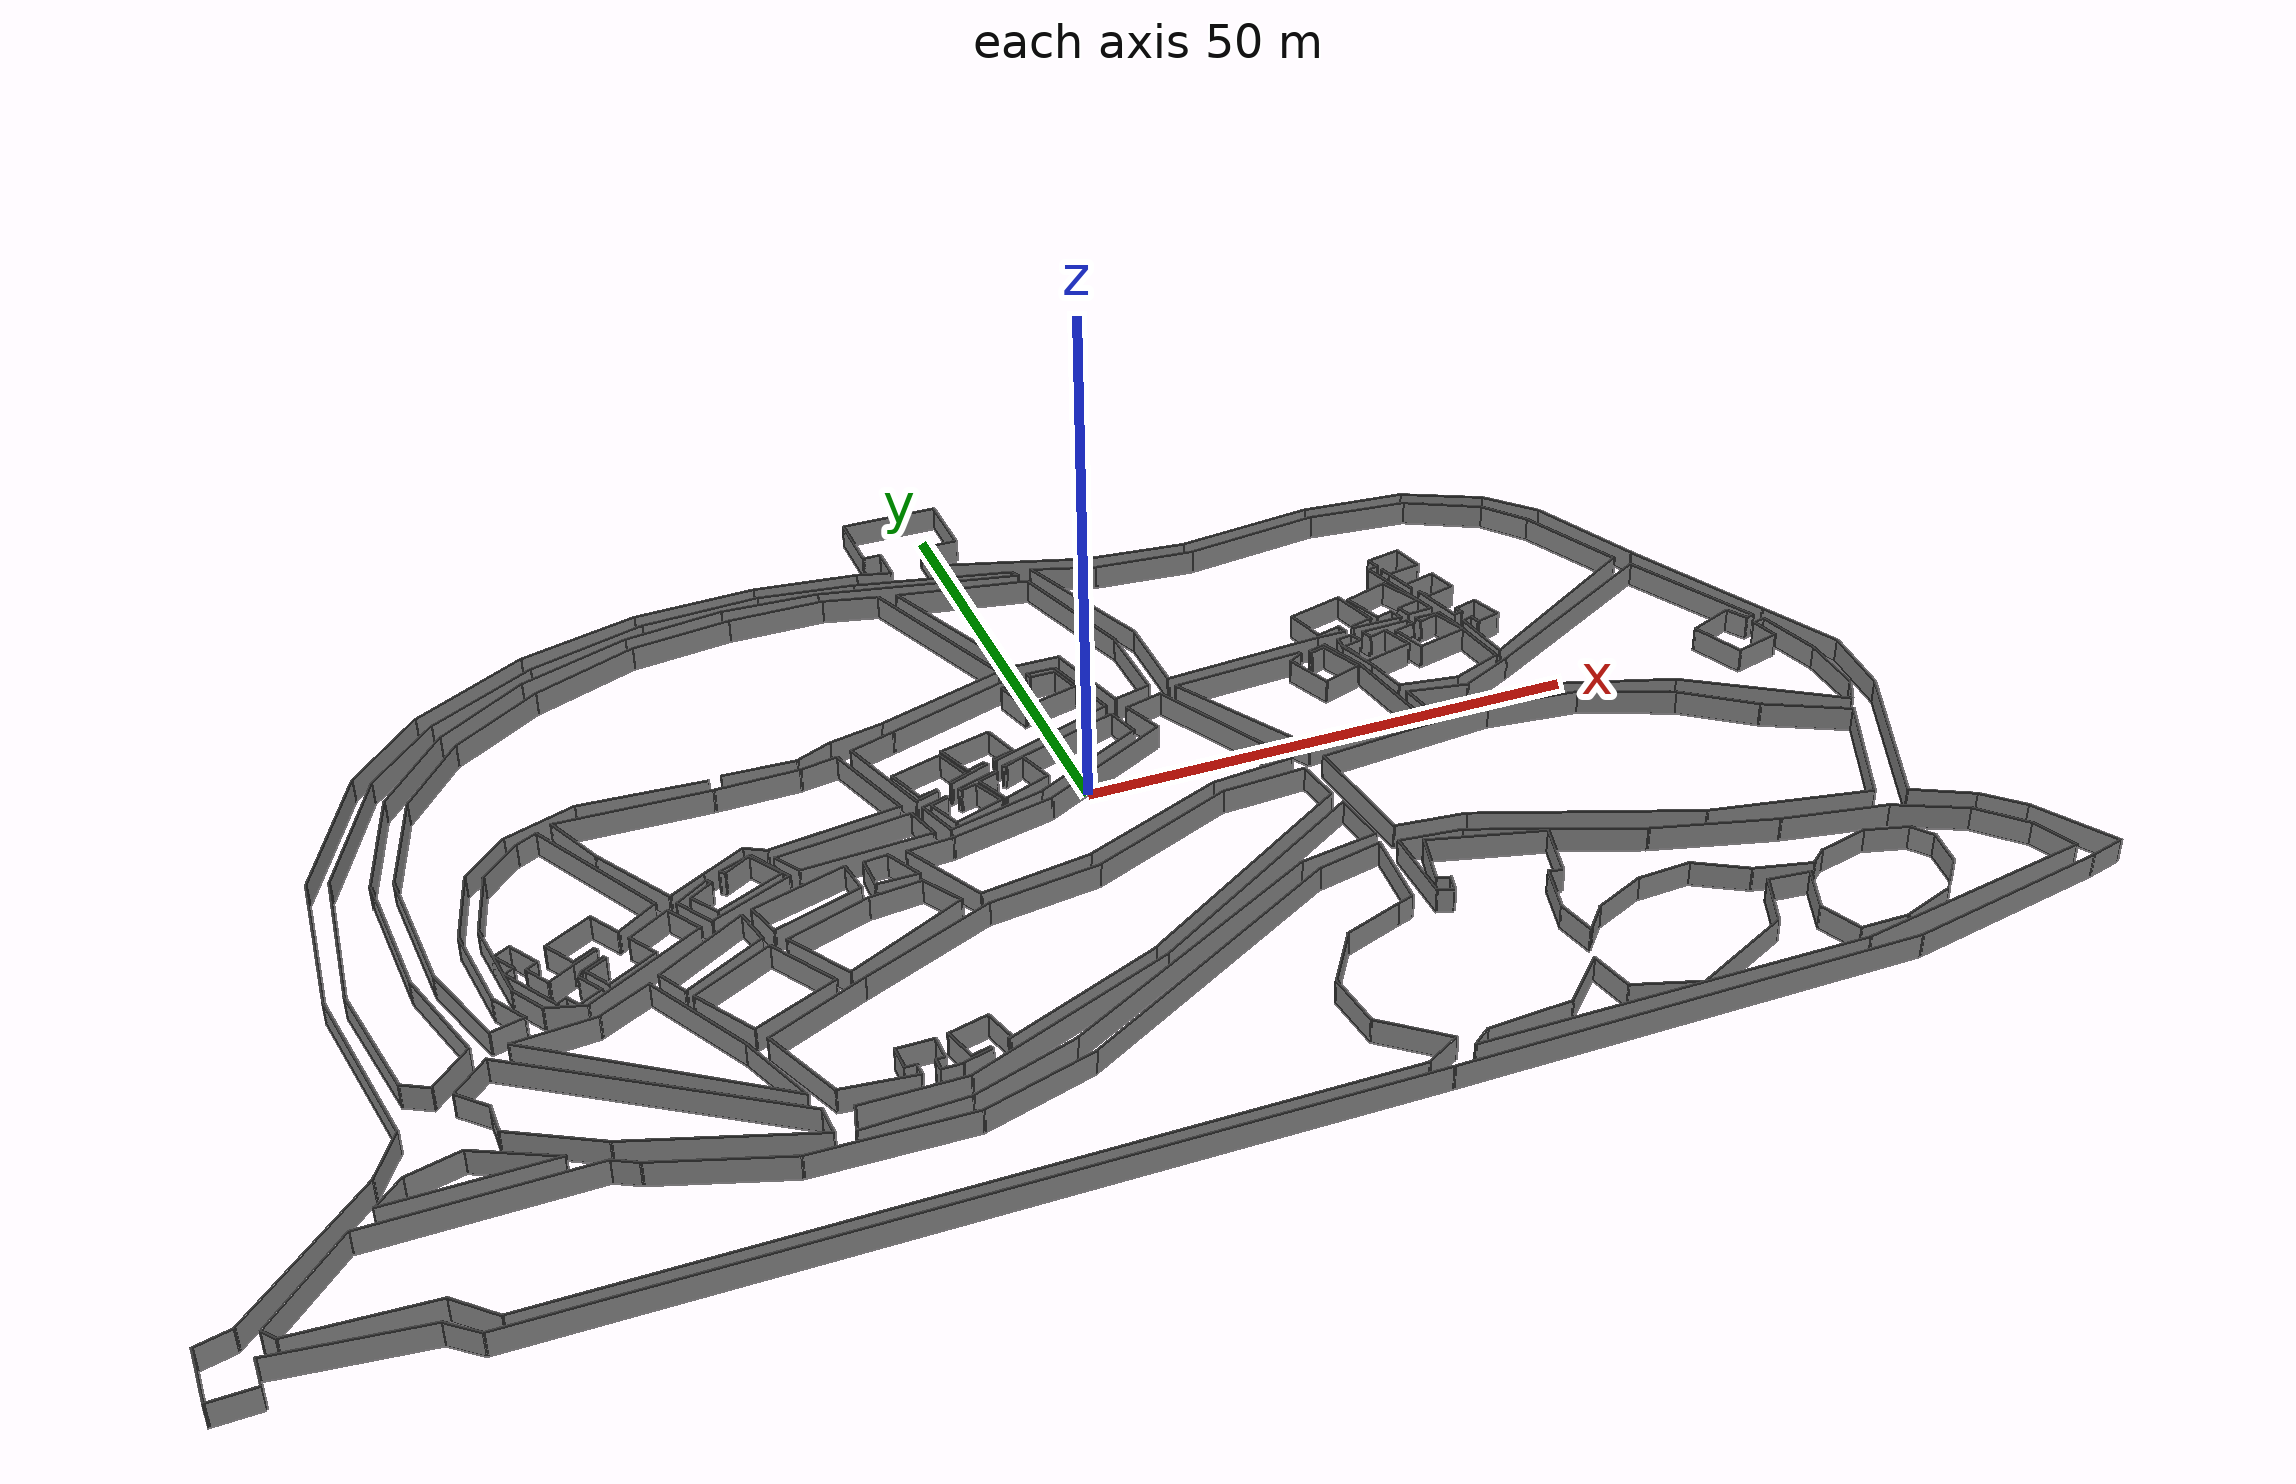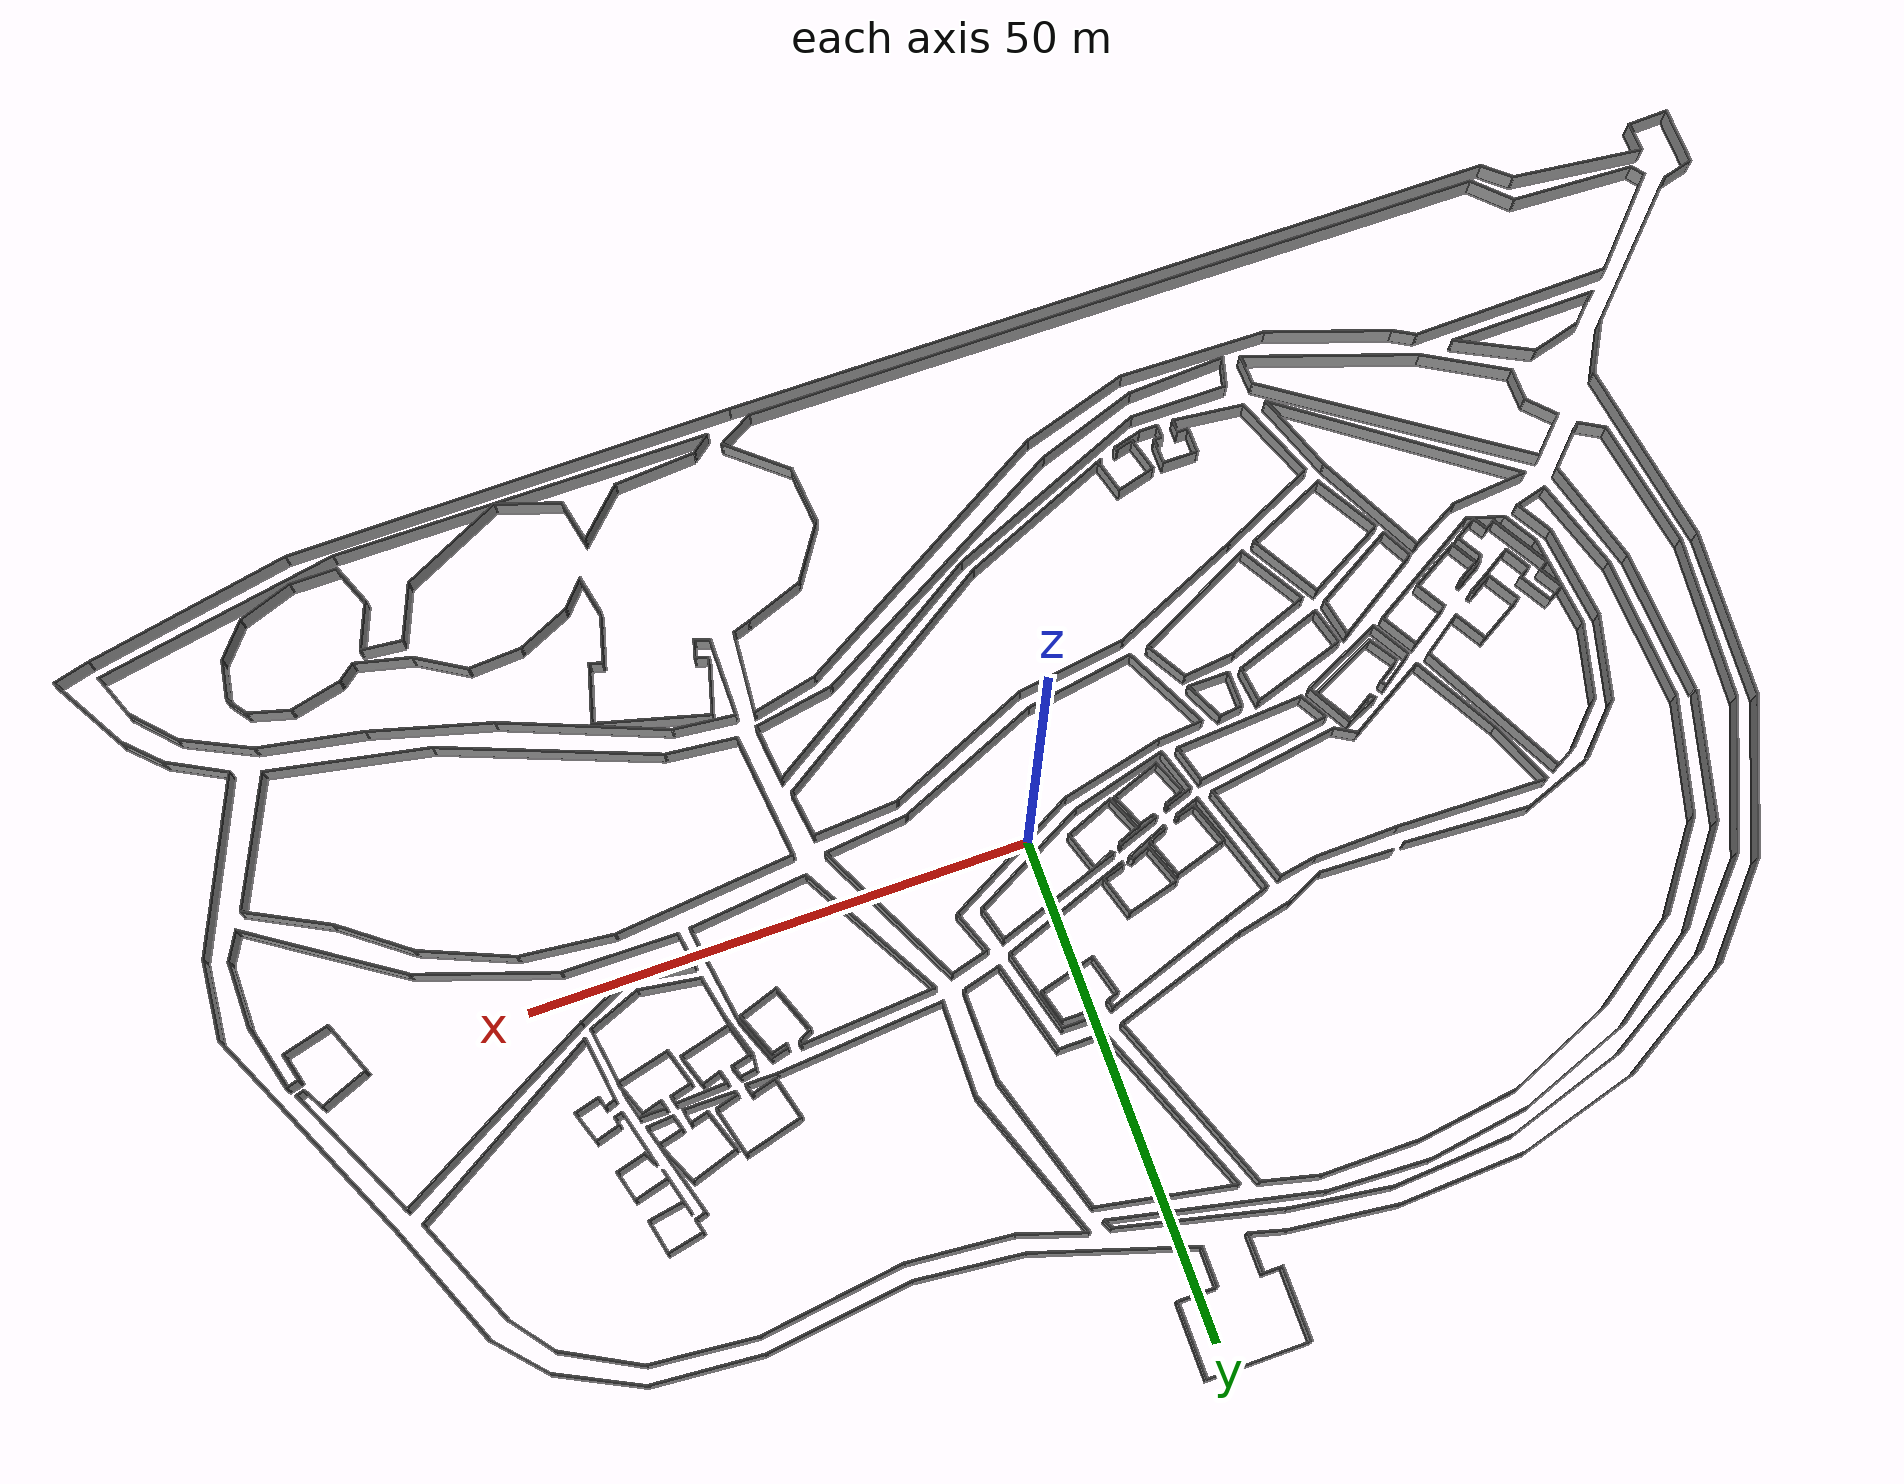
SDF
<?xml version='1.0'?>
<sdf version='1.7'>
  <model name='final_max_v1'>
    <pose>-2.52311 0.669104 0 0 -0 0</pose>
    <link name='Wall_0'>
      <collision name='Wall_0_Collision'>
        <geometry>
          <box>
            <size>6.25 0.15 2.5</size>
          </box>
        </geometry>
        <pose>0 0 1.25 0 -0 0</pose>
      </collision>
      <visual name='Wall_0_Visual'>
        <pose>0 0 1.25 0 -0 0</pose>
        <geometry>
          <box>
            <size>6.25 0.15 2.5</size>
          </box>
        </geometry>
        <material>
          <script>
            <uri>file://media/materials/scripts/gazebo.material</uri>
            <name>Gazebo/Grey</name>
          </script>
          <ambient>1 1 1 1</ambient>
        </material>
        <meta>
          <layer>0</layer>
        </meta>
      </visual>
      <pose>-86.0864 -48.4326 0 0 -0 1.5708</pose>
    </link>
    <link name='Wall_100'>
      <collision name='Wall_100_Collision'>
        <geometry>
          <box>
            <size>19.4552 0.15 2.5</size>
          </box>
        </geometry>
        <pose>0 0 1.25 0 -0 0</pose>
      </collision>
      <visual name='Wall_100_Visual'>
        <pose>0 0 1.25 0 -0 0</pose>
        <geometry>
          <box>
            <size>19.4552 0.15 2.5</size>
          </box>
        </geometry>
        <material>
          <script>
            <uri>file://media/materials/scripts/gazebo.material</uri>
            <name>Gazebo/Grey</name>
          </script>
          <ambient>1 1 1 1</ambient>
        </material>
        <meta>
          <layer>0</layer>
        </meta>
      </visual>
      <pose>-68.6774 -17.2731 0 0 -0 1.7136</pose>
    </link>
    <link name='Wall_101'>
      <collision name='Wall_101_Collision'>
        <geometry>
          <box>
            <size>17.4551 0.15 2.5</size>
          </box>
        </geometry>
        <pose>0 0 1.25 0 -0 0</pose>
      </collision>
      <visual name='Wall_101_Visual'>
        <pose>0 0 1.25 0 -0 0</pose>
        <geometry>
          <box>
            <size>17.4551 0.15 2.5</size>
          </box>
        </geometry>
        <material>
          <script>
            <uri>file://media/materials/scripts/gazebo.material</uri>
            <name>Gazebo/Grey</name>
          </script>
          <ambient>1 1 1 1</ambient>
        </material>
        <meta>
          <layer>0</layer>
        </meta>
      </visual>
      <pose>-69.3611 0.906246 0 0 -0 1.49097</pose>
    </link>
    <link name='Wall_102'>
      <collision name='Wall_102_Collision'>
        <geometry>
          <box>
            <size>16.5473 0.15 2.5</size>
          </box>
        </geometry>
        <pose>0 0 1.25 0 -0 0</pose>
      </collision>
      <visual name='Wall_102_Visual'>
        <pose>0 0 1.25 0 -0 0</pose>
        <geometry>
          <box>
            <size>16.5473 0.15 2.5</size>
          </box>
        </geometry>
        <material>
          <script>
            <uri>file://media/materials/scripts/gazebo.material</uri>
            <name>Gazebo/Grey</name>
          </script>
          <ambient>1 1 1 1</ambient>
        </material>
        <meta>
          <layer>0</layer>
        </meta>
      </visual>
      <pose>-65.3062 17.0076 0 0 -0 1.14788</pose>
    </link>
    <link name='Wall_103'>
      <collision name='Wall_103_Collision'>
        <geometry>
          <box>
            <size>11.1751 0.15 2.5</size>
          </box>
        </geometry>
        <pose>0 0 1.25 0 -0 0</pose>
      </collision>
      <visual name='Wall_103_Visual'>
        <pose>0 0 1.25 0 -0 0</pose>
        <geometry>
          <box>
            <size>11.1751 0.15 2.5</size>
          </box>
        </geometry>
        <material>
          <script>
            <uri>file://media/materials/scripts/gazebo.material</uri>
            <name>Gazebo/Grey</name>
          </script>
          <ambient>1 1 1 1</ambient>
        </material>
        <meta>
          <layer>0</layer>
        </meta>
      </visual>
      <pose>-58.1953 28.5281 0 0 -0 0.823656</pose>
    </link>
    <link name='Wall_104'>
      <collision name='Wall_104_Collision'>
        <geometry>
          <box>
            <size>13.75 0.15 2.5</size>
          </box>
        </geometry>
        <pose>0 0 1.25 0 -0 0</pose>
      </collision>
      <visual name='Wall_104_Visual'>
        <pose>0 0 1.25 0 -0 0</pose>
        <geometry>
          <box>
            <size>13.75 0.15 2.5</size>
          </box>
        </geometry>
        <material>
          <script>
            <uri>file://media/materials/scripts/gazebo.material</uri>
            <name>Gazebo/Grey</name>
          </script>
          <ambient>1 1 1 1</ambient>
        </material>
        <meta>
          <layer>0</layer>
        </meta>
      </visual>
      <pose>-48.5603 35.9723 0 0 -0 0.523599</pose>
    </link>
    <link name='Wall_105'>
      <collision name='Wall_105_Collision'>
        <geometry>
          <box>
            <size>12.9786 0.15 2.5</size>
          </box>
        </geometry>
        <pose>0 0 1.25 0 -0 0</pose>
      </collision>
      <visual name='Wall_105_Visual'>
        <pose>0 0 1.25 0 -0 0</pose>
        <geometry>
          <box>
            <size>12.9786 0.15 2.5</size>
          </box>
        </geometry>
        <material>
          <script>
            <uri>file://media/materials/scripts/gazebo.material</uri>
            <name>Gazebo/Grey</name>
          </script>
          <ambient>1 1 1 1</ambient>
        </material>
        <meta>
          <layer>0</layer>
        </meta>
      </visual>
      <pose>-36.4883 41.0795 0 0 -0 0.269405</pose>
    </link>
    <link name='Wall_106'>
      <collision name='Wall_106_Collision'>
        <geometry>
          <box>
            <size>12.8269 0.15 2.5</size>
          </box>
        </geometry>
        <pose>0 0 1.25 0 -0 0</pose>
      </collision>
      <visual name='Wall_106_Visual'>
        <pose>0 0 1.25 0 -0 0</pose>
        <geometry>
          <box>
            <size>12.8269 0.15 2.5</size>
          </box>
        </geometry>
        <material>
          <script>
            <uri>file://media/materials/scripts/gazebo.material</uri>
            <name>Gazebo/Grey</name>
          </script>
          <ambient>1 1 1 1</ambient>
        </material>
        <meta>
          <layer>0</layer>
        </meta>
      </visual>
      <pose>-23.9732 43.0681 0 0 -0 0.044415</pose>
    </link>
    <link name='Wall_107'>
      <collision name='Wall_107_Collision'>
        <geometry>
          <box>
            <size>10.9191 0.15 2.5</size>
          </box>
        </geometry>
        <pose>0 0 1.25 0 -0 0</pose>
      </collision>
      <visual name='Wall_107_Visual'>
        <pose>0 0 1.25 0 -0 0</pose>
        <geometry>
          <box>
            <size>10.9191 0.15 2.5</size>
          </box>
        </geometry>
        <material>
          <script>
            <uri>file://media/materials/scripts/gazebo.material</uri>
            <name>Gazebo/Grey</name>
          </script>
          <ambient>1 1 1 1</ambient>
        </material>
        <meta>
          <layer>0</layer>
        </meta>
      </visual>
      <pose>-12.2939 42.7164 0 0 -0 -0.117872</pose>
    </link>
    <link name='Wall_111'>
      <collision name='Wall_111_Collision'>
        <geometry>
          <box>
            <size>3.75 0.15 2.5</size>
          </box>
        </geometry>
        <pose>0 0 1.25 0 -0 0</pose>
      </collision>
      <visual name='Wall_111_Visual'>
        <pose>0 0 1.25 0 -0 0</pose>
        <geometry>
          <box>
            <size>3.75 0.15 2.5</size>
          </box>
        </geometry>
        <material>
          <script>
            <uri>file://media/materials/scripts/gazebo.material</uri>
            <name>Gazebo/Grey</name>
          </script>
          <ambient>1 1 1 1</ambient>
        </material>
        <meta>
          <layer>0</layer>
        </meta>
      </visual>
      <pose>-5.20804 41.6173 0 0 -0 -0.261799</pose>
    </link>
    <link name='Wall_112'>
      <collision name='Wall_112_Collision'>
        <geometry>
          <box>
            <size>4 0.15 2.5</size>
          </box>
        </geometry>
        <pose>0 0 1.25 0 -0 0</pose>
      </collision>
      <visual name='Wall_112_Visual'>
        <pose>0 0 1.25 0 -0 0</pose>
        <geometry>
          <box>
            <size>4 0.15 2.5</size>
          </box>
        </geometry>
        <material>
          <script>
            <uri>file://media/materials/scripts/gazebo.material</uri>
            <name>Gazebo/Grey</name>
          </script>
          <ambient>1 1 1 1</ambient>
        </material>
        <meta>
          <layer>0</layer>
        </meta>
      </visual>
      <pose>-3.46937 43.0764 0 0 -0 1.5708</pose>
    </link>
    <link name='Wall_113'>
      <collision name='Wall_113_Collision'>
        <geometry>
          <box>
            <size>2 0.15 2.5</size>
          </box>
        </geometry>
        <pose>0 0 1.25 0 -0 0</pose>
      </collision>
      <visual name='Wall_113_Visual'>
        <pose>0 0 1.25 0 -0 0</pose>
        <geometry>
          <box>
            <size>2 0.15 2.5</size>
          </box>
        </geometry>
        <material>
          <script>
            <uri>file://media/materials/scripts/gazebo.material</uri>
            <name>Gazebo/Grey</name>
          </script>
          <ambient>1 1 1 1</ambient>
        </material>
        <meta>
          <layer>0</layer>
        </meta>
      </visual>
      <pose>-4.39437 45.0014 0 0 -0 3.14159</pose>
    </link>
    <link name='Wall_114'>
      <collision name='Wall_114_Collision'>
        <geometry>
          <box>
            <size>7.25 0.15 2.5</size>
          </box>
        </geometry>
        <pose>0 0 1.25 0 -0 0</pose>
      </collision>
      <visual name='Wall_114_Visual'>
        <pose>0 0 1.25 0 -0 0</pose>
        <geometry>
          <box>
            <size>7.25 0.15 2.5</size>
          </box>
        </geometry>
        <material>
          <script>
            <uri>file://media/materials/scripts/gazebo.material</uri>
            <name>Gazebo/Grey</name>
          </script>
          <ambient>1 1 1 1</ambient>
        </material>
        <meta>
          <layer>0</layer>
        </meta>
      </visual>
      <pose>-5.31937 48.5514 0 0 -0 1.5708</pose>
    </link>
    <link name='Wall_115'>
      <collision name='Wall_115_Collision'>
        <geometry>
          <box>
            <size>10.25 0.15 2.5</size>
          </box>
        </geometry>
        <pose>0 0 1.25 0 -0 0</pose>
      </collision>
      <visual name='Wall_115_Visual'>
        <pose>0 0 1.25 0 -0 0</pose>
        <geometry>
          <box>
            <size>10.25 0.15 2.5</size>
          </box>
        </geometry>
        <material>
          <script>
            <uri>file://media/materials/scripts/gazebo.material</uri>
            <name>Gazebo/Grey</name>
          </script>
          <ambient>1 1 1 1</ambient>
        </material>
        <meta>
          <layer>0</layer>
        </meta>
      </visual>
      <pose>-0.269373 52.1014 0 0 -0 0</pose>
    </link>
    <link name='Wall_116'>
      <collision name='Wall_116_Collision'>
        <geometry>
          <box>
            <size>7.5 0.15 2.5</size>
          </box>
        </geometry>
        <pose>0 0 1.25 0 -0 0</pose>
      </collision>
      <visual name='Wall_116_Visual'>
        <pose>0 0 1.25 0 -0 0</pose>
        <geometry>
          <box>
            <size>7.5 0.15 2.5</size>
          </box>
        </geometry>
        <material>
          <script>
            <uri>file://media/materials/scripts/gazebo.material</uri>
            <name>Gazebo/Grey</name>
          </script>
          <ambient>1 1 1 1</ambient>
        </material>
        <meta>
          <layer>0</layer>
        </meta>
      </visual>
      <pose>4.78063 48.4264 0 0 -0 -1.5708</pose>
    </link>
    <link name='Wall_117'>
      <collision name='Wall_117_Collision'>
        <geometry>
          <box>
            <size>4 0.15 2.5</size>
          </box>
        </geometry>
        <pose>0 0 1.25 0 -0 0</pose>
      </collision>
      <visual name='Wall_117_Visual'>
        <pose>0 0 1.25 0 -0 0</pose>
        <geometry>
          <box>
            <size>4 0.15 2.5</size>
          </box>
        </geometry>
        <material>
          <script>
            <uri>file://media/materials/scripts/gazebo.material</uri>
            <name>Gazebo/Grey</name>
          </script>
          <ambient>1 1 1 1</ambient>
        </material>
        <meta>
          <layer>0</layer>
        </meta>
      </visual>
      <pose>2.85563 44.7514 0 0 -0 3.14159</pose>
    </link>
    <link name='Wall_118'>
      <collision name='Wall_118_Collision'>
        <geometry>
          <box>
            <size>4 0.15 2.5</size>
          </box>
        </geometry>
        <pose>0 0 1.25 0 -0 0</pose>
      </collision>
      <visual name='Wall_118_Visual'>
        <pose>0 0 1.25 0 -0 0</pose>
        <geometry>
          <box>
            <size>4 0.15 2.5</size>
          </box>
        </geometry>
        <material>
          <script>
            <uri>file://media/materials/scripts/gazebo.material</uri>
            <name>Gazebo/Grey</name>
          </script>
          <ambient>1 1 1 1</ambient>
        </material>
        <meta>
          <layer>0</layer>
        </meta>
      </visual>
      <pose>0.930627 42.8264 0 0 -0 -1.5708</pose>
    </link>
    <link name='Wall_119'>
      <collision name='Wall_119_Collision'>
        <geometry>
          <box>
            <size>16.165 0.15 2.5</size>
          </box>
        </geometry>
        <pose>0 0 1.25 0 -0 0</pose>
      </collision>
      <visual name='Wall_119_Visual'>
        <pose>0 0 1.25 0 -0 0</pose>
        <geometry>
          <box>
            <size>16.165 0.15 2.5</size>
          </box>
        </geometry>
        <material>
          <script>
            <uri>file://media/materials/scripts/gazebo.material</uri>
            <name>Gazebo/Grey</name>
          </script>
          <ambient>1 1 1 1</ambient>
        </material>
        <meta>
          <layer>0</layer>
        </meta>
      </visual>
      <pose>8.5693 38.4991 0 0 -0 -0.304697</pose>
    </link>
    <link name='Wall_12'>
      <collision name='Wall_12_Collision'>
        <geometry>
          <box>
            <size>4.71285 0.15 2.5</size>
          </box>
        </geometry>
        <pose>0 0 1.25 0 -0 0</pose>
      </collision>
      <visual name='Wall_12_Visual'>
        <pose>0 0 1.25 0 -0 0</pose>
        <geometry>
          <box>
            <size>4.71285 0.15 2.5</size>
          </box>
        </geometry>
        <material>
          <script>
            <uri>file://media/materials/scripts/gazebo.material</uri>
            <name>Gazebo/Grey</name>
          </script>
          <ambient>1 1 1 1</ambient>
        </material>
        <meta>
          <layer>0</layer>
        </meta>
      </visual>
      <pose>33.7028 -45.8078 0 0 -0 -1.36194</pose>
    </link>
    <link name='Wall_120'>
      <collision name='Wall_120_Collision'>
        <geometry>
          <box>
            <size>10.7874 0.15 2.5</size>
          </box>
        </geometry>
        <pose>0 0 1.25 0 -0 0</pose>
      </collision>
      <visual name='Wall_120_Visual'>
        <pose>0 0 1.25 0 -0 0</pose>
        <geometry>
          <box>
            <size>10.7874 0.15 2.5</size>
          </box>
        </geometry>
        <material>
          <script>
            <uri>file://media/materials/scripts/gazebo.material</uri>
            <name>Gazebo/Grey</name>
          </script>
          <ambient>1 1 1 1</ambient>
        </material>
        <meta>
          <layer>0</layer>
        </meta>
      </visual>
      <pose>21.498 35.5448 0 0 -0 -0.103972</pose>
    </link>
    <link name='Wall_121'>
      <collision name='Wall_121_Collision'>
        <geometry>
          <box>
            <size>14.8821 0.15 2.5</size>
          </box>
        </geometry>
        <pose>0 0 1.25 0 -0 0</pose>
      </collision>
      <visual name='Wall_121_Visual'>
        <pose>0 0 1.25 0 -0 0</pose>
        <geometry>
          <box>
            <size>14.8821 0.15 2.5</size>
          </box>
        </geometry>
        <material>
          <script>
            <uri>file://media/materials/scripts/gazebo.material</uri>
            <name>Gazebo/Grey</name>
          </script>
          <ambient>1 1 1 1</ambient>
        </material>
        <meta>
          <layer>0</layer>
        </meta>
      </visual>
      <pose>34.102 35.8668 0 0 -0 0.118933</pose>
    </link>
    <link name='Wall_122'>
      <collision name='Wall_122_Collision'>
        <geometry>
          <box>
            <size>11.1366 0.15 2.5</size>
          </box>
        </geometry>
        <pose>0 0 1.25 0 -0 0</pose>
      </collision>
      <visual name='Wall_122_Visual'>
        <pose>0 0 1.25 0 -0 0</pose>
        <geometry>
          <box>
            <size>11.1366 0.15 2.5</size>
          </box>
        </geometry>
        <material>
          <script>
            <uri>file://media/materials/scripts/gazebo.material</uri>
            <name>Gazebo/Grey</name>
          </script>
          <ambient>1 1 1 1</ambient>
        </material>
        <meta>
          <layer>0</layer>
        </meta>
      </visual>
      <pose>46.89 36.2808 0 0 -0 -0.083837</pose>
    </link>
    <link name='Wall_123'>
      <collision name='Wall_123_Collision'>
        <geometry>
          <box>
            <size>8.99588 0.15 2.5</size>
          </box>
        </geometry>
        <pose>0 0 1.25 0 -0 0</pose>
      </collision>
      <visual name='Wall_123_Visual'>
        <pose>0 0 1.25 0 -0 0</pose>
        <geometry>
          <box>
            <size>8.99588 0.15 2.5</size>
          </box>
        </geometry>
        <material>
          <script>
            <uri>file://media/materials/scripts/gazebo.material</uri>
            <name>Gazebo/Grey</name>
          </script>
          <ambient>1 1 1 1</ambient>
        </material>
        <meta>
          <layer>0</layer>
        </meta>
      </visual>
      <pose>56.32 33.8428 0 0 -0 -0.463648</pose>
    </link>
    <link name='Wall_124'>
      <collision name='Wall_124_Collision'>
        <geometry>
          <box>
            <size>6.5786 0.15 2.5</size>
          </box>
        </geometry>
        <pose>0 0 1.25 0 -0 0</pose>
      </collision>
      <visual name='Wall_124_Visual'>
        <pose>0 0 1.25 0 -0 0</pose>
        <geometry>
          <box>
            <size>6.5786 0.15 2.5</size>
          </box>
        </geometry>
        <material>
          <script>
            <uri>file://media/materials/scripts/gazebo.material</uri>
            <name>Gazebo/Grey</name>
          </script>
          <ambient>1 1 1 1</ambient>
        </material>
        <meta>
          <layer>0</layer>
        </meta>
      </visual>
      <pose>62.4457 29.4933 0 0 -0 -0.829799</pose>
    </link>
    <link name='Wall_126'>
      <collision name='Wall_126_Collision'>
        <geometry>
          <box>
            <size>3.75 0.15 2.5</size>
          </box>
        </geometry>
        <pose>0 0 1.25 0 -0 0</pose>
      </collision>
      <visual name='Wall_126_Visual'>
        <pose>0 0 1.25 0 -0 0</pose>
        <geometry>
          <box>
            <size>3.75 0.15 2.5</size>
          </box>
        </geometry>
        <material>
          <script>
            <uri>file://media/materials/scripts/gazebo.material</uri>
            <name>Gazebo/Grey</name>
          </script>
          <ambient>1 1 1 1</ambient>
        </material>
        <meta>
          <layer>0</layer>
        </meta>
      </visual>
      <pose>-69.2284 -33.7829 0 0 -0 0.785398</pose>
    </link>
    <link name='Wall_127'>
      <collision name='Wall_127_Collision'>
        <geometry>
          <box>
            <size>5.5 0.15 2.5</size>
          </box>
        </geometry>
        <pose>0 0 1.25 0 -0 0</pose>
      </collision>
      <visual name='Wall_127_Visual'>
        <pose>0 0 1.25 0 -0 0</pose>
        <geometry>
          <box>
            <size>5.5 0.15 2.5</size>
          </box>
        </geometry>
        <material>
          <script>
            <uri>file://media/materials/scripts/gazebo.material</uri>
            <name>Gazebo/Grey</name>
          </script>
          <ambient>1 1 1 1</ambient>
        </material>
        <meta>
          <layer>0</layer>
        </meta>
      </visual>
      <pose>-65.3717 -31.8178 0 0 -0 0.261799</pose>
    </link>
    <link name='Wall_128'>
      <collision name='Wall_128_Collision'>
        <geometry>
          <box>
            <size>8.46258 0.15 2.5</size>
          </box>
        </geometry>
        <pose>0 0 1.25 0 -0 0</pose>
      </collision>
      <visual name='Wall_128_Visual'>
        <pose>0 0 1.25 0 -0 0</pose>
        <geometry>
          <box>
            <size>8.46258 0.15 2.5</size>
          </box>
        </geometry>
        <material>
          <script>
            <uri>file://media/materials/scripts/gazebo.material</uri>
            <name>Gazebo/Grey</name>
          </script>
          <ambient>1 1 1 1</ambient>
        </material>
        <meta>
          <layer>0</layer>
        </meta>
      </visual>
      <pose>-59.0888 -33.0206 0 0 -0 -0.47347</pose>
    </link>
    <link name='Wall_129'>
      <collision name='Wall_129_Collision'>
        <geometry>
          <box>
            <size>15.488 0.15 2.5</size>
          </box>
        </geometry>
        <pose>0 0 1.25 0 -0 0</pose>
      </collision>
      <visual name='Wall_129_Visual'>
        <pose>0 0 1.25 0 -0 0</pose>
        <geometry>
          <box>
            <size>15.488 0.15 2.5</size>
          </box>
        </geometry>
        <material>
          <script>
            <uri>file://media/materials/scripts/gazebo.material</uri>
            <name>Gazebo/Grey</name>
          </script>
          <ambient>1 1 1 1</ambient>
        </material>
        <meta>
          <layer>0</layer>
        </meta>
      </visual>
      <pose>-63.0581 -35.0458 0 0 -0 -3.12463</pose>
    </link>
    <link name='Wall_13'>
      <collision name='Wall_13_Collision'>
        <geometry>
          <box>
            <size>6.84861 0.15 2.5</size>
          </box>
        </geometry>
        <pose>0 0 1.25 0 -0 0</pose>
      </collision>
      <visual name='Wall_13_Visual'>
        <pose>0 0 1.25 0 -0 0</pose>
        <geometry>
          <box>
            <size>6.84861 0.15 2.5</size>
          </box>
        </geometry>
        <material>
          <script>
            <uri>file://media/materials/scripts/gazebo.material</uri>
            <name>Gazebo/Grey</name>
          </script>
          <ambient>1 1 1 1</ambient>
        </material>
        <meta>
          <layer>0</layer>
        </meta>
      </visual>
      <pose>37.3584 -49.0831 0 0 -0 -0.316824</pose>
    </link>
    <link name='Wall_131'>
      <collision name='Wall_131_Collision'>
        <geometry>
          <box>
            <size>16.551 0.15 2.5</size>
          </box>
        </geometry>
        <pose>0 0 1.25 0 -0 0</pose>
      </collision>
      <visual name='Wall_131_Visual'>
        <pose>0 0 1.25 0 -0 0</pose>
        <geometry>
          <box>
            <size>16.551 0.15 2.5</size>
          </box>
        </geometry>
        <material>
          <script>
            <uri>file://media/materials/scripts/gazebo.material</uri>
            <name>Gazebo/Grey</name>
          </script>
          <ambient>1 1 1 1</ambient>
        </material>
        <meta>
          <layer>0</layer>
        </meta>
      </visual>
      <pose>61.4597 -29.6539 0 0 -0 2.9497</pose>
    </link>
    <link name='Wall_132'>
      <collision name='Wall_132_Collision'>
        <geometry>
          <box>
            <size>22.4626 0.15 2.5</size>
          </box>
        </geometry>
        <pose>0 0 1.25 0 -0 0</pose>
      </collision>
      <visual name='Wall_132_Visual'>
        <pose>0 0 1.25 0 -0 0</pose>
        <geometry>
          <box>
            <size>22.4626 0.15 2.5</size>
          </box>
        </geometry>
        <material>
          <script>
            <uri>file://media/materials/scripts/gazebo.material</uri>
            <name>Gazebo/Grey</name>
          </script>
          <ambient>1 1 1 1</ambient>
        </material>
        <meta>
          <layer>0</layer>
        </meta>
      </visual>
      <pose>43.0137 -24.0419 0 0 -0 2.77027</pose>
    </link>
    <link name='Wall_133'>
      <collision name='Wall_133_Collision'>
        <geometry>
          <box>
            <size>7.27213 0.15 2.5</size>
          </box>
        </geometry>
        <pose>0 0 1.25 0 -0 0</pose>
      </collision>
      <visual name='Wall_133_Visual'>
        <pose>0 0 1.25 0 -0 0</pose>
        <geometry>
          <box>
            <size>7.27213 0.15 2.5</size>
          </box>
        </geometry>
        <material>
          <script>
            <uri>file://media/materials/scripts/gazebo.material</uri>
            <name>Gazebo/Grey</name>
          </script>
          <ambient>1 1 1 1</ambient>
        </material>
        <meta>
          <layer>0</layer>
        </meta>
      </visual>
      <pose>29.0757 -19.6259 0 0 -0 3.03807</pose>
    </link>
    <link name='Wall_134'>
      <collision name='Wall_134_Collision'>
        <geometry>
          <box>
            <size>13.0122 0.15 2.5</size>
          </box>
        </geometry>
        <pose>0 0 1.25 0 -0 0</pose>
      </collision>
      <visual name='Wall_134_Visual'>
        <pose>0 0 1.25 0 -0 0</pose>
        <geometry>
          <box>
            <size>13.0122 0.15 2.5</size>
          </box>
        </geometry>
        <material>
          <script>
            <uri>file://media/materials/scripts/gazebo.material</uri>
            <name>Gazebo/Grey</name>
          </script>
          <ambient>1 1 1 1</ambient>
        </material>
        <meta>
          <layer>0</layer>
        </meta>
      </visual>
      <pose>24.8437 -12.8639 0 0 -0 1.67829</pose>
    </link>
    <link name='Wall_135'>
      <collision name='Wall_135_Collision'>
        <geometry>
          <box>
            <size>18.5413 0.15 2.5</size>
          </box>
        </geometry>
        <pose>0 0 1.25 0 -0 0</pose>
      </collision>
      <visual name='Wall_135_Visual'>
        <pose>0 0 1.25 0 -0 0</pose>
        <geometry>
          <box>
            <size>18.5413 0.15 2.5</size>
          </box>
        </geometry>
        <material>
          <script>
            <uri>file://media/materials/scripts/gazebo.material</uri>
            <name>Gazebo/Grey</name>
          </script>
          <ambient>1 1 1 1</ambient>
        </material>
        <meta>
          <layer>0</layer>
        </meta>
      </visual>
      <pose>33.3077 -5.59592 0 0 -0 0.095189</pose>
    </link>
    <link name='Wall_136'>
      <collision name='Wall_136_Collision'>
        <geometry>
          <box>
            <size>9.49695 0.15 2.5</size>
          </box>
        </geometry>
        <pose>0 0 1.25 0 -0 0</pose>
      </collision>
      <visual name='Wall_136_Visual'>
        <pose>0 0 1.25 0 -0 0</pose>
        <geometry>
          <box>
            <size>9.49695 0.15 2.5</size>
          </box>
        </geometry>
        <material>
          <script>
            <uri>file://media/materials/scripts/gazebo.material</uri>
            <name>Gazebo/Grey</name>
          </script>
          <ambient>1 1 1 1</ambient>
        </material>
        <meta>
          <layer>0</layer>
        </meta>
      </visual>
      <pose>47.1077 -5.22792 0 0 -0 -0.108483</pose>
    </link>
    <link name='Wall_137'>
      <collision name='Wall_137_Collision'>
        <geometry>
          <box>
            <size>9.83843 0.15 2.5</size>
          </box>
        </geometry>
        <pose>0 0 1.25 0 -0 0</pose>
      </collision>
      <visual name='Wall_137_Visual'>
        <pose>0 0 1.25 0 -0 0</pose>
        <geometry>
          <box>
            <size>9.83843 0.15 2.5</size>
          </box>
        </geometry>
        <material>
          <script>
            <uri>file://media/materials/scripts/gazebo.material</uri>
            <name>Gazebo/Grey</name>
          </script>
          <ambient>1 1 1 1</ambient>
        </material>
        <meta>
          <layer>0</layer>
        </meta>
      </visual>
      <pose>56.2157 -7.61992 0 0 -0 -0.399904</pose>
    </link>
    <link name='Wall_138'>
      <collision name='Wall_138_Collision'>
        <geometry>
          <box>
            <size>8.35659 0.15 2.5</size>
          </box>
        </geometry>
        <pose>0 0 1.25 0 -0 0</pose>
      </collision>
      <visual name='Wall_138_Visual'>
        <pose>0 0 1.25 0 -0 0</pose>
        <geometry>
          <box>
            <size>8.35659 0.15 2.5</size>
          </box>
        </geometry>
        <material>
          <script>
            <uri>file://media/materials/scripts/gazebo.material</uri>
            <name>Gazebo/Grey</name>
          </script>
          <ambient>1 1 1 1</ambient>
        </material>
        <meta>
          <layer>0</layer>
        </meta>
      </visual>
      <pose>63.9437 -11.9899 0 0 -0 -0.650227</pose>
    </link>
    <link name='Wall_139'>
      <collision name='Wall_139_Collision'>
        <geometry>
          <box>
            <size>9.07969 0.15 2.5</size>
          </box>
        </geometry>
        <pose>0 0 1.25 0 -0 0</pose>
      </collision>
      <visual name='Wall_139_Visual'>
        <pose>0 0 1.25 0 -0 0</pose>
        <geometry>
          <box>
            <size>9.07969 0.15 2.5</size>
          </box>
        </geometry>
        <material>
          <script>
            <uri>file://media/materials/scripts/gazebo.material</uri>
            <name>Gazebo/Grey</name>
          </script>
          <ambient>1 1 1 1</ambient>
        </material>
        <meta>
          <layer>0</layer>
        </meta>
      </visual>
      <pose>71.1657 -16.5439 0 0 -0 -0.482079</pose>
    </link>
    <link name='Wall_14'>
      <collision name='Wall_14_Collision'>
        <geometry>
          <box>
            <size>11.6765 0.15 2.5</size>
          </box>
        </geometry>
        <pose>0 0 1.25 0 -0 0</pose>
      </collision>
      <visual name='Wall_14_Visual'>
        <pose>0 0 1.25 0 -0 0</pose>
        <geometry>
          <box>
            <size>11.6765 0.15 2.5</size>
          </box>
        </geometry>
        <material>
          <script>
            <uri>file://media/materials/scripts/gazebo.material</uri>
            <name>Gazebo/Grey</name>
          </script>
          <ambient>1 1 1 1</ambient>
        </material>
        <meta>
          <layer>0</layer>
        </meta>
      </visual>
      <pose>45.7063 -47.5701 0 0 -0 0.459599</pose>
    </link>
    <link name='Wall_140'>
      <collision name='Wall_140_Collision'>
        <geometry>
          <box>
            <size>13.9469 0.15 2.5</size>
          </box>
        </geometry>
        <pose>0 0 1.25 0 -0 0</pose>
      </collision>
      <visual name='Wall_140_Visual'>
        <pose>0 0 1.25 0 -0 0</pose>
        <geometry>
          <box>
            <size>13.9469 0.15 2.5</size>
          </box>
        </geometry>
        <material>
          <script>
            <uri>file://media/materials/scripts/gazebo.material</uri>
            <name>Gazebo/Grey</name>
          </script>
          <ambient>1 1 1 1</ambient>
        </material>
        <meta>
          <layer>0</layer>
        </meta>
      </visual>
      <pose>72.3157 -24.9159 0 0 -0 -1.9897</pose>
    </link>
    <link name='Wall_142'>
      <collision name='Wall_142_Collision'>
        <geometry>
          <box>
            <size>3 0.15 2.5</size>
          </box>
        </geometry>
        <pose>0 0 1.25 0 -0 0</pose>
      </collision>
      <visual name='Wall_142_Visual'>
        <pose>0 0 1.25 0 -0 0</pose>
        <geometry>
          <box>
            <size>3 0.15 2.5</size>
          </box>
        </geometry>
        <material>
          <script>
            <uri>file://media/materials/scripts/gazebo.material</uri>
            <name>Gazebo/Grey</name>
          </script>
          <ambient>1 1 1 1</ambient>
        </material>
        <meta>
          <layer>0</layer>
        </meta>
      </visual>
      <pose>-64.8763 -21.7565 0 0 -0 2.61799</pose>
    </link>
    <link name='Wall_143'>
      <collision name='Wall_143_Collision'>
        <geometry>
          <box>
            <size>13.7057 0.15 2.5</size>
          </box>
        </geometry>
        <pose>0 0 1.25 0 -0 0</pose>
      </collision>
      <visual name='Wall_143_Visual'>
        <pose>0 0 1.25 0 -0 0</pose>
        <geometry>
          <box>
            <size>13.7057 0.15 2.5</size>
          </box>
        </geometry>
        <material>
          <script>
            <uri>file://media/materials/scripts/gazebo.material</uri>
            <name>Gazebo/Grey</name>
          </script>
          <ambient>1 1 1 1</ambient>
        </material>
        <meta>
          <layer>0</layer>
        </meta>
      </visual>
      <pose>-67.1763 -14.3505 0 0 -0 1.72872</pose>
    </link>
    <link name='Wall_145'>
      <collision name='Wall_145_Collision'>
        <geometry>
          <box>
            <size>16.9669 0.15 2.5</size>
          </box>
        </geometry>
        <pose>0 0 1.25 0 -0 0</pose>
      </collision>
      <visual name='Wall_145_Visual'>
        <pose>0 0 1.25 0 -0 0</pose>
        <geometry>
          <box>
            <size>16.9669 0.15 2.5</size>
          </box>
        </geometry>
        <material>
          <script>
            <uri>file://media/materials/scripts/gazebo.material</uri>
            <name>Gazebo/Grey</name>
          </script>
          <ambient>1 1 1 1</ambient>
        </material>
        <meta>
          <layer>0</layer>
        </meta>
      </visual>
      <pose>-67.4602 0.714958 0 0 -0 1.47766</pose>
    </link>
    <link name='Wall_147'>
      <collision name='Wall_147_Collision'>
        <geometry>
          <box>
            <size>15.7591 0.15 2.5</size>
          </box>
        </geometry>
        <pose>0 0 1.25 0 -0 0</pose>
      </collision>
      <visual name='Wall_147_Visual'>
        <pose>0 0 1.25 0 -0 0</pose>
        <geometry>
          <box>
            <size>15.7591 0.15 2.5</size>
          </box>
        </geometry>
        <material>
          <script>
            <uri>file://media/materials/scripts/gazebo.material</uri>
            <name>Gazebo/Grey</name>
          </script>
          <ambient>1 1 1 1</ambient>
        </material>
        <meta>
          <layer>0</layer>
        </meta>
      </visual>
      <pose>-63.5042 16.217 0 0 -0 1.15197</pose>
    </link>
    <link name='Wall_149'>
      <collision name='Wall_149_Collision'>
        <geometry>
          <box>
            <size>10.4318 0.15 2.5</size>
          </box>
        </geometry>
        <pose>0 0 1.25 0 -0 0</pose>
      </collision>
      <visual name='Wall_149_Visual'>
        <pose>0 0 1.25 0 -0 0</pose>
        <geometry>
          <box>
            <size>10.4318 0.15 2.5</size>
          </box>
        </geometry>
        <material>
          <script>
            <uri>file://media/materials/scripts/gazebo.material</uri>
            <name>Gazebo/Grey</name>
          </script>
          <ambient>1 1 1 1</ambient>
        </material>
        <meta>
          <layer>0</layer>
        </meta>
      </visual>
      <pose>-56.7882 27.073 0 0 -0 0.810709</pose>
    </link>
    <link name='Wall_15'>
      <collision name='Wall_15_Collision'>
        <geometry>
          <box>
            <size>6.09874 0.15 2.5</size>
          </box>
        </geometry>
        <pose>0 0 1.25 0 -0 0</pose>
      </collision>
      <visual name='Wall_15_Visual'>
        <pose>0 0 1.25 0 -0 0</pose>
        <geometry>
          <box>
            <size>6.09874 0.15 2.5</size>
          </box>
        </geometry>
        <material>
          <script>
            <uri>file://media/materials/scripts/gazebo.material</uri>
            <name>Gazebo/Grey</name>
          </script>
          <ambient>1 1 1 1</ambient>
        </material>
        <meta>
          <layer>0</layer>
        </meta>
      </visual>
      <pose>51.9671 -42.2484 0 0 -0 1.19355</pose>
    </link>
    <link name='Wall_151'>
      <collision name='Wall_151_Collision'>
        <geometry>
          <box>
            <size>12.8849 0.15 2.5</size>
          </box>
        </geometry>
        <pose>0 0 1.25 0 -0 0</pose>
      </collision>
      <visual name='Wall_151_Visual'>
        <pose>0 0 1.25 0 -0 0</pose>
        <geometry>
          <box>
            <size>12.8849 0.15 2.5</size>
          </box>
        </geometry>
        <material>
          <script>
            <uri>file://media/materials/scripts/gazebo.material</uri>
            <name>Gazebo/Grey</name>
          </script>
          <ambient>1 1 1 1</ambient>
        </material>
        <meta>
          <layer>0</layer>
        </meta>
      </visual>
      <pose>-47.7262 33.973 0 0 -0 0.521834</pose>
    </link>
    <link name='Wall_153'>
      <collision name='Wall_153_Collision'>
        <geometry>
          <box>
            <size>12.9542 0.15 2.5</size>
          </box>
        </geometry>
        <pose>0 0 1.25 0 -0 0</pose>
      </collision>
      <visual name='Wall_153_Visual'>
        <pose>0 0 1.25 0 -0 0</pose>
        <geometry>
          <box>
            <size>12.9542 0.15 2.5</size>
          </box>
        </geometry>
        <material>
          <script>
            <uri>file://media/materials/scripts/gazebo.material</uri>
            <name>Gazebo/Grey</name>
          </script>
          <ambient>1 1 1 1</ambient>
        </material>
        <meta>
          <layer>0</layer>
        </meta>
      </visual>
      <pose>-36.0882 39.033 0 0 -0 0.299027</pose>
    </link>
    <link name='Wall_155'>
      <collision name='Wall_155_Collision'>
        <geometry>
          <box>
            <size>12.4081 0.15 2.5</size>
          </box>
        </geometry>
        <pose>0 0 1.25 0 -0 0</pose>
      </collision>
      <visual name='Wall_155_Visual'>
        <pose>0 0 1.25 0 -0 0</pose>
        <geometry>
          <box>
            <size>12.4081 0.15 2.5</size>
          </box>
        </geometry>
        <material>
          <script>
            <uri>file://media/materials/scripts/gazebo.material</uri>
            <name>Gazebo/Grey</name>
          </script>
          <ambient>1 1 1 1</ambient>
        </material>
        <meta>
          <layer>0</layer>
        </meta>
      </visual>
      <pose>-23.8522 41.287 0 0 -0 0.060078</pose>
    </link>
    <link name='Wall_157'>
      <collision name='Wall_157_Collision'>
        <geometry>
          <box>
            <size>10.2725 0.15 2.5</size>
          </box>
        </geometry>
        <pose>0 0 1.25 0 -0 0</pose>
      </collision>
      <visual name='Wall_157_Visual'>
        <pose>0 0 1.25 0 -0 0</pose>
        <geometry>
          <box>
            <size>10.2725 0.15 2.5</size>
          </box>
        </geometry>
        <material>
          <script>
            <uri>file://media/materials/scripts/gazebo.material</uri>
            <name>Gazebo/Grey</name>
          </script>
          <ambient>1 1 1 1</ambient>
        </material>
        <meta>
          <layer>0</layer>
        </meta>
      </visual>
      <pose>-12.7202 40.965 0 0 -0 -0.136756</pose>
    </link>
    <link name='Wall_159'>
      <collision name='Wall_159_Collision'>
        <geometry>
          <box>
            <size>16.3963 0.15 2.5</size>
          </box>
        </geometry>
        <pose>0 0 1.25 0 -0 0</pose>
      </collision>
      <visual name='Wall_159_Visual'>
        <pose>0 0 1.25 0 -0 0</pose>
        <geometry>
          <box>
            <size>16.3963 0.15 2.5</size>
          </box>
        </geometry>
        <material>
          <script>
            <uri>file://media/materials/scripts/gazebo.material</uri>
            <name>Gazebo/Grey</name>
          </script>
          <ambient>1 1 1 1</ambient>
        </material>
        <meta>
          <layer>0</layer>
        </meta>
      </visual>
      <pose>0.113766 38.435 0 0 -0 -0.228497</pose>
    </link>
    <link name='Wall_16'>
      <collision name='Wall_16_Collision'>
        <geometry>
          <box>
            <size>4.34473 0.15 2.5</size>
          </box>
        </geometry>
        <pose>0 0 1.25 0 -0 0</pose>
      </collision>
      <visual name='Wall_16_Visual'>
        <pose>0 0 1.25 0 -0 0</pose>
        <geometry>
          <box>
            <size>4.34473 0.15 2.5</size>
          </box>
        </geometry>
        <material>
          <script>
            <uri>file://media/materials/scripts/gazebo.material</uri>
            <name>Gazebo/Grey</name>
          </script>
          <ambient>1 1 1 1</ambient>
        </material>
        <meta>
          <layer>0</layer>
        </meta>
      </visual>
      <pose>55.1497 -39.6918 0 0 -0 -0.099669</pose>
    </link>
    <link name='Wall_164'>
      <collision name='Wall_164_Collision'>
        <geometry>
          <box>
            <size>9.16316 0.15 2.5</size>
          </box>
        </geometry>
        <pose>0 0 1.25 0 -0 0</pose>
      </collision>
      <visual name='Wall_164_Visual'>
        <pose>0 0 1.25 0 -0 0</pose>
        <geometry>
          <box>
            <size>9.16316 0.15 2.5</size>
          </box>
        </geometry>
        <material>
          <script>
            <uri>file://media/materials/scripts/gazebo.material</uri>
            <name>Gazebo/Grey</name>
          </script>
          <ambient>1 1 1 1</ambient>
        </material>
        <meta>
          <layer>0</layer>
        </meta>
      </visual>
      <pose>13.3066 15.8045 0 0 -0 -1.56262</pose>
    </link>
    <link name='Wall_167'>
      <collision name='Wall_167_Collision'>
        <geometry>
          <box>
            <size>4 0.15 2.5</size>
          </box>
        </geometry>
        <pose>0 0 1.25 0 -0 0</pose>
      </collision>
      <visual name='Wall_167_Visual'>
        <pose>0 0 1.25 0 -0 0</pose>
        <geometry>
          <box>
            <size>4 0.15 2.5</size>
          </box>
        </geometry>
        <material>
          <script>
            <uri>file://media/materials/scripts/gazebo.material</uri>
            <name>Gazebo/Grey</name>
          </script>
          <ambient>1 1 1 1</ambient>
        </material>
        <meta>
          <layer>0</layer>
        </meta>
      </visual>
      <pose>11.3094 10.7013 0 0 -0 0.261799</pose>
    </link>
    <link name='Wall_169'>
      <collision name='Wall_169_Collision'>
        <geometry>
          <box>
            <size>9.75 0.15 2.5</size>
          </box>
        </geometry>
        <pose>0 0 1.25 0 -0 0</pose>
      </collision>
      <visual name='Wall_169_Visual'>
        <pose>0 0 1.25 0 -0 0</pose>
        <geometry>
          <box>
            <size>9.75 0.15 2.5</size>
          </box>
        </geometry>
        <material>
          <script>
            <uri>file://media/materials/scripts/gazebo.material</uri>
            <name>Gazebo/Grey</name>
          </script>
          <ambient>1 1 1 1</ambient>
        </material>
        <meta>
          <layer>0</layer>
        </meta>
      </visual>
      <pose>8.20764 14.8395 0 0 -0 1.8326</pose>
    </link>
    <link name='Wall_17'>
      <collision name='Wall_17_Collision'>
        <geometry>
          <box>
            <size>5.3044 0.15 2.5</size>
          </box>
        </geometry>
        <pose>0 0 1.25 0 -0 0</pose>
      </collision>
      <visual name='Wall_17_Visual'>
        <pose>0 0 1.25 0 -0 0</pose>
        <geometry>
          <box>
            <size>5.3044 0.15 2.5</size>
          </box>
        </geometry>
        <material>
          <script>
            <uri>file://media/materials/scripts/gazebo.material</uri>
            <name>Gazebo/Grey</name>
          </script>
          <ambient>1 1 1 1</ambient>
        </material>
        <meta>
          <layer>0</layer>
        </meta>
      </visual>
      <pose>56.2976 -42.3005 0 0 -0 -1.94378</pose>
    </link>
    <link name='Wall_171'>
      <collision name='Wall_171_Collision'>
        <geometry>
          <box>
            <size>4.75 0.15 2.5</size>
          </box>
        </geometry>
        <pose>0 0 1.25 0 -0 0</pose>
      </collision>
      <visual name='Wall_171_Visual'>
        <pose>0 0 1.25 0 -0 0</pose>
        <geometry>
          <box>
            <size>4.75 0.15 2.5</size>
          </box>
        </geometry>
        <material>
          <script>
            <uri>file://media/materials/scripts/gazebo.material</uri>
            <name>Gazebo/Grey</name>
          </script>
          <ambient>1 1 1 1</ambient>
        </material>
        <meta>
          <layer>0</layer>
        </meta>
      </visual>
      <pose>4.66531 19.476 0 0 -0 3.14159</pose>
    </link>
    <link name='Wall_177'>
      <collision name='Wall_177_Collision'>
        <geometry>
          <box>
            <size>11.25 0.15 2.5</size>
          </box>
        </geometry>
        <pose>0 0 1.25 0 -0 0</pose>
      </collision>
      <visual name='Wall_177_Visual'>
        <pose>0 0 1.25 0 -0 0</pose>
        <geometry>
          <box>
            <size>11.25 0.15 2.5</size>
          </box>
        </geometry>
        <material>
          <script>
            <uri>file://media/materials/scripts/gazebo.material</uri>
            <name>Gazebo/Grey</name>
          </script>
          <ambient>1 1 1 1</ambient>
        </material>
        <meta>
          <layer>0</layer>
        </meta>
      </visual>
      <pose>-61.219 -13.2274 0 0 -0 1.8326</pose>
    </link>
    <link name='Wall_178'>
      <collision name='Wall_178_Collision'>
        <geometry>
          <box>
            <size>14.9254 0.15 2.5</size>
          </box>
        </geometry>
        <pose>0 0 1.25 0 -0 0</pose>
      </collision>
      <visual name='Wall_178_Visual'>
        <pose>0 0 1.25 0 -0 0</pose>
        <geometry>
          <box>
            <size>14.9254 0.15 2.5</size>
          </box>
        </geometry>
        <material>
          <script>
            <uri>file://media/materials/scripts/gazebo.material</uri>
            <name>Gazebo/Grey</name>
          </script>
          <ambient>1 1 1 1</ambient>
        </material>
        <meta>
          <layer>0</layer>
        </meta>
      </visual>
      <pose>-62.967 -0.485436 0 0 -0 1.61298</pose>
    </link>
    <link name='Wall_18'>
      <collision name='Wall_18_Collision'>
        <geometry>
          <box>
            <size>4.54873 0.15 2.5</size>
          </box>
        </geometry>
        <pose>0 0 1.25 0 -0 0</pose>
      </collision>
      <visual name='Wall_18_Visual'>
        <pose>0 0 1.25 0 -0 0</pose>
        <geometry>
          <box>
            <size>4.54873 0.15 2.5</size>
          </box>
        </geometry>
        <material>
          <script>
            <uri>file://media/materials/scripts/gazebo.material</uri>
            <name>Gazebo/Grey</name>
          </script>
          <ambient>1 1 1 1</ambient>
        </material>
        <meta>
          <layer>0</layer>
        </meta>
      </visual>
      <pose>56.1932 -46.7353 0 0 -0 -1.18148</pose>
    </link>
    <link name='Wall_180'>
      <collision name='Wall_180_Collision'>
        <geometry>
          <box>
            <size>13.3433 0.15 2.5</size>
          </box>
        </geometry>
        <pose>0 0 1.25 0 -0 0</pose>
      </collision>
      <visual name='Wall_180_Visual'>
        <pose>0 0 1.25 0 -0 0</pose>
        <geometry>
          <box>
            <size>13.3433 0.15 2.5</size>
          </box>
        </geometry>
        <material>
          <script>
            <uri>file://media/materials/scripts/gazebo.material</uri>
            <name>Gazebo/Grey</name>
          </script>
          <ambient>1 1 1 1</ambient>
        </material>
        <meta>
          <layer>0</layer>
        </meta>
      </visual>
      <pose>-61.5766 13.5197 0 0 -0 1.29537</pose>
    </link>
    <link name='Wall_181'>
      <collision name='Wall_181_Collision'>
        <geometry>
          <box>
            <size>11.2134 0.15 2.5</size>
          </box>
        </geometry>
        <pose>0 0 1.25 0 -0 0</pose>
      </collision>
      <visual name='Wall_181_Visual'>
        <pose>0 0 1.25 0 -0 0</pose>
        <geometry>
          <box>
            <size>11.2134 0.15 2.5</size>
          </box>
        </geometry>
        <material>
          <script>
            <uri>file://media/materials/scripts/gazebo.material</uri>
            <name>Gazebo/Grey</name>
          </script>
          <ambient>1 1 1 1</ambient>
        </material>
        <meta>
          <layer>0</layer>
        </meta>
      </visual>
      <pose>-56.3326 24.1917 0 0 -0 0.897354</pose>
    </link>
    <link name='Wall_183'>
      <collision name='Wall_183_Collision'>
        <geometry>
          <box>
            <size>11.4034 0.15 2.5</size>
          </box>
        </geometry>
        <pose>0 0 1.25 0 -0 0</pose>
      </collision>
      <visual name='Wall_183_Visual'>
        <pose>0 0 1.25 0 -0 0</pose>
        <geometry>
          <box>
            <size>11.4034 0.15 2.5</size>
          </box>
        </geometry>
        <material>
          <script>
            <uri>file://media/materials/scripts/gazebo.material</uri>
            <name>Gazebo/Grey</name>
          </script>
          <ambient>1 1 1 1</ambient>
        </material>
        <meta>
          <layer>0</layer>
        </meta>
      </visual>
      <pose>-48.2366 31.6897 0 0 -0 0.59934</pose>
    </link>
    <link name='Wall_185'>
      <collision name='Wall_185_Collision'>
        <geometry>
          <box>
            <size>12.286 0.15 2.5</size>
          </box>
        </geometry>
        <pose>0 0 1.25 0 -0 0</pose>
      </collision>
      <visual name='Wall_185_Visual'>
        <pose>0 0 1.25 0 -0 0</pose>
        <geometry>
          <box>
            <size>12.286 0.15 2.5</size>
          </box>
        </geometry>
        <material>
          <script>
            <uri>file://media/materials/scripts/gazebo.material</uri>
            <name>Gazebo/Grey</name>
          </script>
          <ambient>1 1 1 1</ambient>
        </material>
        <meta>
          <layer>0</layer>
        </meta>
      </visual>
      <pose>-37.8866 36.9337 0 0 -0 0.348123</pose>
    </link>
    <link name='Wall_187'>
      <collision name='Wall_187_Collision'>
        <geometry>
          <box>
            <size>10.5586 0.15 2.5</size>
          </box>
        </geometry>
        <pose>0 0 1.25 0 -0 0</pose>
      </collision>
      <visual name='Wall_187_Visual'>
        <pose>0 0 1.25 0 -0 0</pose>
        <geometry>
          <box>
            <size>10.5586 0.15 2.5</size>
          </box>
        </geometry>
        <material>
          <script>
            <uri>file://media/materials/scripts/gazebo.material</uri>
            <name>Gazebo/Grey</name>
          </script>
          <ambient>1 1 1 1</ambient>
        </material>
        <meta>
          <layer>0</layer>
        </meta>
      </visual>
      <pose>-27.0306 39.7397 0 0 -0 0.141897</pose>
    </link>
    <link name='Wall_189'>
      <collision name='Wall_189_Collision'>
        <geometry>
          <box>
            <size>10.2804 0.15 2.5</size>
          </box>
        </geometry>
        <pose>0 0 1.25 0 -0 0</pose>
      </collision>
      <visual name='Wall_189_Visual'>
        <pose>0 0 1.25 0 -0 0</pose>
        <geometry>
          <box>
            <size>10.2804 0.15 2.5</size>
          </box>
        </geometry>
        <material>
          <script>
            <uri>file://media/materials/scripts/gazebo.material</uri>
            <name>Gazebo/Grey</name>
          </script>
          <ambient>1 1 1 1</ambient>
        </material>
        <meta>
          <layer>0</layer>
        </meta>
      </visual>
      <pose>-16.8186 40.2457 0 0 -0 -0.045423</pose>
    </link>
    <link name='Wall_191'>
      <collision name='Wall_191_Collision'>
        <geometry>
          <box>
            <size>20.8467 0.15 2.5</size>
          </box>
        </geometry>
        <pose>0 0 1.25 0 -0 0</pose>
      </collision>
      <visual name='Wall_191_Visual'>
        <pose>0 0 1.25 0 -0 0</pose>
        <geometry>
          <box>
            <size>20.8467 0.15 2.5</size>
          </box>
        </geometry>
        <material>
          <script>
            <uri>file://media/materials/scripts/gazebo.material</uri>
            <name>Gazebo/Grey</name>
          </script>
          <ambient>1 1 1 1</ambient>
        </material>
        <meta>
          <layer>0</layer>
        </meta>
      </visual>
      <pose>-1.63858 37.8537 0 0 -0 -0.210472</pose>
    </link>
    <link name='Wall_193'>
      <collision name='Wall_193_Collision'>
        <geometry>
          <box>
            <size>1.1617 0.15 2.5</size>
          </box>
        </geometry>
        <pose>0 0 1.25 0 -0 0</pose>
      </collision>
      <visual name='Wall_193_Visual'>
        <pose>0 0 1.25 0 -0 0</pose>
        <geometry>
          <box>
            <size>1.1617 0.15 2.5</size>
          </box>
        </geometry>
        <material>
          <script>
            <uri>file://media/materials/scripts/gazebo.material</uri>
            <name>Gazebo/Grey</name>
          </script>
          <ambient>1 1 1 1</ambient>
        </material>
        <meta>
          <layer>0</layer>
        </meta>
      </visual>
      <pose>8.25359 36.1433 0 0 -0 2.03799</pose>
    </link>
    <link name='Wall_195'>
      <collision name='Wall_195_Collision'>
        <geometry>
          <box>
            <size>9.95782 0.15 2.5</size>
          </box>
        </geometry>
        <pose>0 0 1.25 0 -0 0</pose>
      </collision>
      <visual name='Wall_195_Visual'>
        <pose>0 0 1.25 0 -0 0</pose>
        <geometry>
          <box>
            <size>9.95782 0.15 2.5</size>
          </box>
        </geometry>
        <material>
          <script>
            <uri>file://media/materials/scripts/gazebo.material</uri>
            <name>Gazebo/Grey</name>
          </script>
          <ambient>1 1 1 1</ambient>
        </material>
        <meta>
          <layer>0</layer>
        </meta>
      </visual>
      <pose>-59.1949 -12.5474 0 0 -0 1.86585</pose>
    </link>
    <link name='Wall_196'>
      <collision name='Wall_196_Collision'>
        <geometry>
          <box>
            <size>15.018 0.15 2.5</size>
          </box>
        </geometry>
        <pose>0 0 1.25 0 -0 0</pose>
      </collision>
      <visual name='Wall_196_Visual'>
        <pose>0 0 1.25 0 -0 0</pose>
        <geometry>
          <box>
            <size>15.018 0.15 2.5</size>
          </box>
        </geometry>
        <material>
          <script>
            <uri>file://media/materials/scripts/gazebo.material</uri>
            <name>Gazebo/Grey</name>
          </script>
          <ambient>1 1 1 1</ambient>
        </material>
        <meta>
          <layer>0</layer>
        </meta>
      </visual>
      <pose>-60.9452 -0.428503 0 0 -0 1.61444</pose>
    </link>
    <link name='Wall_198'>
      <collision name='Wall_198_Collision'>
        <geometry>
          <box>
            <size>12.2392 0.15 2.5</size>
          </box>
        </geometry>
        <pose>0 0 1.25 0 -0 0</pose>
      </collision>
      <visual name='Wall_198_Visual'>
        <pose>0 0 1.25 0 -0 0</pose>
        <geometry>
          <box>
            <size>12.2392 0.15 2.5</size>
          </box>
        </geometry>
        <material>
          <script>
            <uri>file://media/materials/scripts/gazebo.material</uri>
            <name>Gazebo/Grey</name>
          </script>
          <ambient>1 1 1 1</ambient>
        </material>
        <meta>
          <layer>0</layer>
        </meta>
      </visual>
      <pose>-59.5904 12.8051 0 0 -0 1.28932</pose>
    </link>
    <link name='Wall_2'>
      <collision name='Wall_2_Collision'>
        <geometry>
          <box>
            <size>3.25 0.15 2.5</size>
          </box>
        </geometry>
        <pose>0 0 1.25 0 -0 0</pose>
      </collision>
      <visual name='Wall_2_Visual'>
        <pose>0 0 1.25 0 -0 0</pose>
        <geometry>
          <box>
            <size>3.25 0.15 2.5</size>
          </box>
        </geometry>
        <material>
          <script>
            <uri>file://media/materials/scripts/gazebo.material</uri>
            <name>Gazebo/Grey</name>
          </script>
          <ambient>1 1 1 1</ambient>
        </material>
        <meta>
          <layer>0</layer>
        </meta>
      </visual>
      <pose>-81.869 -49.7753 0 0 -0 1.5708</pose>
    </link>
    <link name='Wall_200'>
      <collision name='Wall_200_Collision'>
        <geometry>
          <box>
            <size>10.2252 0.15 2.5</size>
          </box>
        </geometry>
        <pose>0 0 1.25 0 -0 0</pose>
      </collision>
      <visual name='Wall_200_Visual'>
        <pose>0 0 1.25 0 -0 0</pose>
        <geometry>
          <box>
            <size>10.2252 0.15 2.5</size>
          </box>
        </geometry>
        <material>
          <script>
            <uri>file://media/materials/scripts/gazebo.material</uri>
            <name>Gazebo/Grey</name>
          </script>
          <ambient>1 1 1 1</ambient>
        </material>
        <meta>
          <layer>0</layer>
        </meta>
      </visual>
      <pose>-54.8331 22.5996 0 0 -0 0.913407</pose>
    </link>
    <link name='Wall_203'>
      <collision name='Wall_203_Collision'>
        <geometry>
          <box>
            <size>11.085 0.15 2.5</size>
          </box>
        </geometry>
        <pose>0 0 1.25 0 -0 0</pose>
      </collision>
      <visual name='Wall_203_Visual'>
        <pose>0 0 1.25 0 -0 0</pose>
        <geometry>
          <box>
            <size>11.085 0.15 2.5</size>
          </box>
        </geometry>
        <material>
          <script>
            <uri>file://media/materials/scripts/gazebo.material</uri>
            <name>Gazebo/Grey</name>
          </script>
          <ambient>1 1 1 1</ambient>
        </material>
        <meta>
          <layer>0</layer>
        </meta>
      </visual>
      <pose>-47.218 29.6386 0 0 -0 0.592066</pose>
    </link>
    <link name='Wall_205'>
      <collision name='Wall_205_Collision'>
        <geometry>
          <box>
            <size>11.7846 0.15 2.5</size>
          </box>
        </geometry>
        <pose>0 0 1.25 0 -0 0</pose>
      </collision>
      <visual name='Wall_205_Visual'>
        <pose>0 0 1.25 0 -0 0</pose>
        <geometry>
          <box>
            <size>11.7846 0.15 2.5</size>
          </box>
        </geometry>
        <material>
          <script>
            <uri>file://media/materials/scripts/gazebo.material</uri>
            <name>Gazebo/Grey</name>
          </script>
          <ambient>1 1 1 1</ambient>
        </material>
        <meta>
          <layer>0</layer>
        </meta>
      </visual>
      <pose>-37.2991 34.8978 0 0 -0 0.389317</pose>
    </link>
    <link name='Wall_207'>
      <collision name='Wall_207_Collision'>
        <geometry>
          <box>
            <size>10.546 0.15 2.5</size>
          </box>
        </geometry>
        <pose>0 0 1.25 0 -0 0</pose>
      </collision>
      <visual name='Wall_207_Visual'>
        <pose>0 0 1.25 0 -0 0</pose>
        <geometry>
          <box>
            <size>10.546 0.15 2.5</size>
          </box>
        </geometry>
        <material>
          <script>
            <uri>file://media/materials/scripts/gazebo.material</uri>
            <name>Gazebo/Grey</name>
          </script>
          <ambient>1 1 1 1</ambient>
        </material>
        <meta>
          <layer>0</layer>
        </meta>
      </visual>
      <pose>-26.7651 37.7958 0 0 -0 0.133136</pose>
    </link>
    <link name='Wall_208'>
      <collision name='Wall_208_Collision'>
        <geometry>
          <box>
            <size>10 0.15 2.5</size>
          </box>
        </geometry>
        <pose>0 0 1.25 0 -0 0</pose>
      </collision>
      <visual name='Wall_208_Visual'>
        <pose>0 0 1.25 0 -0 0</pose>
        <geometry>
          <box>
            <size>10 0.15 2.5</size>
          </box>
        </geometry>
        <material>
          <script>
            <uri>file://media/materials/scripts/gazebo.material</uri>
            <name>Gazebo/Grey</name>
          </script>
          <ambient>1 1 1 1</ambient>
        </material>
        <meta>
          <layer>0</layer>
        </meta>
      </visual>
      <pose>-16.6881 38.4858 0 0 -0 0</pose>
    </link>
    <link name='Wall_21'>
      <collision name='Wall_21_Collision'>
        <geometry>
          <box>
            <size>4.95 0.15 2.5</size>
          </box>
        </geometry>
        <pose>0 0 1.25 0 -0 0</pose>
      </collision>
      <visual name='Wall_21_Visual'>
        <pose>0 0 1.25 0 -0 0</pose>
        <geometry>
          <box>
            <size>4.95 0.15 2.5</size>
          </box>
        </geometry>
        <material>
          <script>
            <uri>file://media/materials/scripts/gazebo.material</uri>
            <name>Gazebo/Grey</name>
          </script>
          <ambient>1 1 1 1</ambient>
        </material>
        <meta>
          <layer>0</layer>
        </meta>
      </visual>
      <pose>59.428 -48.7701 0 0 -0 0</pose>
    </link>
    <link name='Wall_211'>
      <collision name='Wall_211_Collision'>
        <geometry>
          <box>
            <size>14.7253 0.15 2.5</size>
          </box>
        </geometry>
        <pose>0 0 1.25 0 -0 0</pose>
      </collision>
      <visual name='Wall_211_Visual'>
        <pose>0 0 1.25 0 -0 0</pose>
        <geometry>
          <box>
            <size>14.7253 0.15 2.5</size>
          </box>
        </geometry>
        <material>
          <script>
            <uri>file://media/materials/scripts/gazebo.material</uri>
            <name>Gazebo/Grey</name>
          </script>
          <ambient>1 1 1 1</ambient>
        </material>
        <meta>
          <layer>0</layer>
        </meta>
      </visual>
      <pose>11.1463 27.2824 0 0 -0 -1.27513</pose>
    </link>
    <link name='Wall_213'>
      <collision name='Wall_213_Collision'>
        <geometry>
          <box>
            <size>9.53445 0.15 2.5</size>
          </box>
        </geometry>
        <pose>0 0 1.25 0 -0 0</pose>
      </collision>
      <visual name='Wall_213_Visual'>
        <pose>0 0 1.25 0 -0 0</pose>
        <geometry>
          <box>
            <size>9.53445 0.15 2.5</size>
          </box>
        </geometry>
        <material>
          <script>
            <uri>file://media/materials/scripts/gazebo.material</uri>
            <name>Gazebo/Grey</name>
          </script>
          <ambient>1 1 1 1</ambient>
        </material>
        <meta>
          <layer>0</layer>
        </meta>
      </visual>
      <pose>15.6009 16.3138 0 0 -0 1.56099</pose>
    </link>
    <link name='Wall_215'>
      <collision name='Wall_215_Collision'>
        <geometry>
          <box>
            <size>16.389 0.15 2.5</size>
          </box>
        </geometry>
        <pose>0 0 1.25 0 -0 0</pose>
      </collision>
      <visual name='Wall_215_Visual'>
        <pose>0 0 1.25 0 -0 0</pose>
        <geometry>
          <box>
            <size>16.389 0.15 2.5</size>
          </box>
        </geometry>
        <material>
          <script>
            <uri>file://media/materials/scripts/gazebo.material</uri>
            <name>Gazebo/Grey</name>
          </script>
          <ambient>1 1 1 1</ambient>
        </material>
        <meta>
          <layer>0</layer>
        </meta>
      </visual>
      <pose>12.8869 28.6418 0 0 -0 1.91763</pose>
    </link>
    <link name='Wall_217'>
      <collision name='Wall_217_Collision'>
        <geometry>
          <box>
            <size>6.92872 0.15 2.5</size>
          </box>
        </geometry>
        <pose>0 0 1.25 0 -0 0</pose>
      </collision>
      <visual name='Wall_217_Visual'>
        <pose>0 0 1.25 0 -0 0</pose>
        <geometry>
          <box>
            <size>6.92872 0.15 2.5</size>
          </box>
        </geometry>
        <material>
          <script>
            <uri>file://media/materials/scripts/gazebo.material</uri>
            <name>Gazebo/Grey</name>
          </script>
          <ambient>1 1 1 1</ambient>
        </material>
        <meta>
          <layer>0</layer>
        </meta>
      </visual>
      <pose>13.3469 35.2198 0 0 -0 -0.317459</pose>
    </link>
    <link name='Wall_219'>
      <collision name='Wall_219_Collision'>
        <geometry>
          <box>
            <size>10.5866 0.15 2.5</size>
          </box>
        </geometry>
        <pose>0 0 1.25 0 -0 0</pose>
      </collision>
      <visual name='Wall_219_Visual'>
        <pose>0 0 1.25 0 -0 0</pose>
        <geometry>
          <box>
            <size>10.5866 0.15 2.5</size>
          </box>
        </geometry>
        <material>
          <script>
            <uri>file://media/materials/scripts/gazebo.material</uri>
            <name>Gazebo/Grey</name>
          </script>
          <ambient>1 1 1 1</ambient>
        </material>
        <meta>
          <layer>0</layer>
        </meta>
      </visual>
      <pose>21.7649 33.7018 0 0 -0 -0.088266</pose>
    </link>
    <link name='Wall_22'>
      <collision name='Wall_22_Collision'>
        <geometry>
          <box>
            <size>6.02507 0.15 2.5</size>
          </box>
        </geometry>
        <pose>0 0 1.25 0 -0 0</pose>
      </collision>
      <visual name='Wall_22_Visual'>
        <pose>0 0 1.25 0 -0 0</pose>
        <geometry>
          <box>
            <size>6.02507 0.15 2.5</size>
          </box>
        </geometry>
        <material>
          <script>
            <uri>file://media/materials/scripts/gazebo.material</uri>
            <name>Gazebo/Grey</name>
          </script>
          <ambient>1 1 1 1</ambient>
        </material>
        <meta>
          <layer>0</layer>
        </meta>
      </visual>
      <pose>64.5932 -47.7788 0 0 -0 0.344219</pose>
    </link>
    <link name='Wall_221'>
      <collision name='Wall_221_Collision'>
        <geometry>
          <box>
            <size>14.7107 0.15 2.5</size>
          </box>
        </geometry>
        <pose>0 0 1.25 0 -0 0</pose>
      </collision>
      <visual name='Wall_221_Visual'>
        <pose>0 0 1.25 0 -0 0</pose>
        <geometry>
          <box>
            <size>14.7107 0.15 2.5</size>
          </box>
        </geometry>
        <material>
          <script>
            <uri>file://media/materials/scripts/gazebo.material</uri>
            <name>Gazebo/Grey</name>
          </script>
          <ambient>1 1 1 1</ambient>
        </material>
        <meta>
          <layer>0</layer>
        </meta>
      </visual>
      <pose>34.1849 34.1618 0 0 -0 0.126706</pose>
    </link>
    <link name='Wall_223'>
      <collision name='Wall_223_Collision'>
        <geometry>
          <box>
            <size>10.6867 0.15 2.5</size>
          </box>
        </geometry>
        <pose>0 0 1.25 0 -0 0</pose>
      </collision>
      <visual name='Wall_223_Visual'>
        <pose>0 0 1.25 0 -0 0</pose>
        <geometry>
          <box>
            <size>10.6867 0.15 2.5</size>
          </box>
        </geometry>
        <material>
          <script>
            <uri>file://media/materials/scripts/gazebo.material</uri>
            <name>Gazebo/Grey</name>
          </script>
          <ambient>1 1 1 1</ambient>
        </material>
        <meta>
          <layer>0</layer>
        </meta>
      </visual>
      <pose>46.6509 34.5758 0 0 -0 -0.096193</pose>
    </link>
    <link name='Wall_224'>
      <collision name='Wall_224_Collision'>
        <geometry>
          <box>
            <size>8.50581 0.15 2.5</size>
          </box>
        </geometry>
        <pose>0 0 1.25 0 -0 0</pose>
      </collision>
      <visual name='Wall_224_Visual'>
        <pose>0 0 1.25 0 -0 0</pose>
        <geometry>
          <box>
            <size>8.50581 0.15 2.5</size>
          </box>
        </geometry>
        <material>
          <script>
            <uri>file://media/materials/scripts/gazebo.material</uri>
            <name>Gazebo/Grey</name>
          </script>
          <ambient>1 1 1 1</ambient>
        </material>
        <meta>
          <layer>0</layer>
        </meta>
      </visual>
      <pose>55.5749 32.0918 0 0 -0 -0.493196</pose>
    </link>
    <link name='Wall_225'>
      <collision name='Wall_225_Collision'>
        <geometry>
          <box>
            <size>5.52393 0.15 2.5</size>
          </box>
        </geometry>
        <pose>0 0 1.25 0 -0 0</pose>
      </collision>
      <visual name='Wall_225_Visual'>
        <pose>0 0 1.25 0 -0 0</pose>
        <geometry>
          <box>
            <size>5.52393 0.15 2.5</size>
          </box>
        </geometry>
        <material>
          <script>
            <uri>file://media/materials/scripts/gazebo.material</uri>
            <name>Gazebo/Grey</name>
          </script>
          <ambient>1 1 1 1</ambient>
        </material>
        <meta>
          <layer>0</layer>
        </meta>
      </visual>
      <pose>60.9109 27.9978 0 0 -0 -0.90675</pose>
    </link>
    <link name='Wall_226'>
      <collision name='Wall_226_Collision'>
        <geometry>
          <box>
            <size>11.7237 0.15 2.5</size>
          </box>
        </geometry>
        <pose>0 0 1.25 0 -0 0</pose>
      </collision>
      <visual name='Wall_226_Visual'>
        <pose>0 0 1.25 0 -0 0</pose>
        <geometry>
          <box>
            <size>11.7237 0.15 2.5</size>
          </box>
        </geometry>
        <material>
          <script>
            <uri>file://media/materials/scripts/gazebo.material</uri>
            <name>Gazebo/Grey</name>
          </script>
          <ambient>1 1 1 1</ambient>
        </material>
        <meta>
          <layer>0</layer>
        </meta>
      </visual>
      <pose>64.9129 20.5918 0 0 -0 -1.15338</pose>
    </link>
    <link name='Wall_229'>
      <collision name='Wall_229_Collision'>
        <geometry>
          <box>
            <size>12.5433 0.15 2.5</size>
          </box>
        </geometry>
        <pose>0 0 1.25 0 -0 0</pose>
      </collision>
      <visual name='Wall_229_Visual'>
        <pose>0 0 1.25 0 -0 0</pose>
        <geometry>
          <box>
            <size>12.5433 0.15 2.5</size>
          </box>
        </geometry>
        <material>
          <script>
            <uri>file://media/materials/scripts/gazebo.material</uri>
            <name>Gazebo/Grey</name>
          </script>
          <ambient>1 1 1 1</ambient>
        </material>
        <meta>
          <layer>0</layer>
        </meta>
      </visual>
      <pose>67.0397 21.4191 0 0 -0 -1.16884</pose>
    </link>
    <link name='Wall_23'>
      <collision name='Wall_23_Collision'>
        <geometry>
          <box>
            <size>4.59918 0.15 2.5</size>
          </box>
        </geometry>
        <pose>0 0 1.25 0 -0 0</pose>
      </collision>
      <visual name='Wall_23_Visual'>
        <pose>0 0 1.25 0 -0 0</pose>
        <geometry>
          <box>
            <size>4.59918 0.15 2.5</size>
          </box>
        </geometry>
        <material>
          <script>
            <uri>file://media/materials/scripts/gazebo.material</uri>
            <name>Gazebo/Grey</name>
          </script>
          <ambient>1 1 1 1</ambient>
        </material>
        <meta>
          <layer>0</layer>
        </meta>
      </visual>
      <pose>68.7671 -45.0658 0 0 -0 0.885067</pose>
    </link>
    <link name='Wall_233'>
      <collision name='Wall_233_Collision'>
        <geometry>
          <box>
            <size>12.0422 0.15 2.5</size>
          </box>
        </geometry>
        <pose>0 0 1.25 0 -0 0</pose>
      </collision>
      <visual name='Wall_233_Visual'>
        <pose>0 0 1.25 0 -0 0</pose>
        <geometry>
          <box>
            <size>12.0422 0.15 2.5</size>
          </box>
        </geometry>
        <material>
          <script>
            <uri>file://media/materials/scripts/gazebo.material</uri>
            <name>Gazebo/Grey</name>
          </script>
          <ambient>1 1 1 1</ambient>
        </material>
        <meta>
          <layer>0</layer>
        </meta>
      </visual>
      <pose>29.7422 -3.55323 0 0 -0 0.105489</pose>
    </link>
    <link name='Wall_234'>
      <collision name='Wall_234_Collision'>
        <geometry>
          <box>
            <size>10.0086 0.15 2.5</size>
          </box>
        </geometry>
        <pose>0 0 1.25 0 -0 0</pose>
      </collision>
      <visual name='Wall_234_Visual'>
        <pose>0 0 1.25 0 -0 0</pose>
        <geometry>
          <box>
            <size>10.0086 0.15 2.5</size>
          </box>
        </geometry>
        <material>
          <script>
            <uri>file://media/materials/scripts/gazebo.material</uri>
            <name>Gazebo/Grey</name>
          </script>
          <ambient>1 1 1 1</ambient>
        </material>
        <meta>
          <layer>0</layer>
        </meta>
      </visual>
      <pose>34.8901 1.94242 0 0 -0 1.72666</pose>
    </link>
    <link name='Wall_235'>
      <collision name='Wall_235_Collision'>
        <geometry>
          <box>
            <size>5.08472 0.15 2.5</size>
          </box>
        </geometry>
        <pose>0 0 1.25 0 -0 0</pose>
      </collision>
      <visual name='Wall_235_Visual'>
        <pose>0 0 1.25 0 -0 0</pose>
        <geometry>
          <box>
            <size>5.08472 0.15 2.5</size>
          </box>
        </geometry>
        <material>
          <script>
            <uri>file://media/materials/scripts/gazebo.material</uri>
            <name>Gazebo/Grey</name>
          </script>
          <ambient>1 1 1 1</ambient>
        </material>
        <meta>
          <layer>0</layer>
        </meta>
      </visual>
      <pose>33.2205 9.10764 0 0 -0 1.94607</pose>
    </link>
    <link name='Wall_237'>
      <collision name='Wall_237_Collision'>
        <geometry>
          <box>
            <size>16.5284 0.15 2.5</size>
          </box>
        </geometry>
        <pose>0 0 1.25 0 -0 0</pose>
      </collision>
      <visual name='Wall_237_Visual'>
        <pose>0 0 1.25 0 -0 0</pose>
        <geometry>
          <box>
            <size>16.5284 0.15 2.5</size>
          </box>
        </geometry>
        <material>
          <script>
            <uri>file://media/materials/scripts/gazebo.material</uri>
            <name>Gazebo/Grey</name>
          </script>
          <ambient>1 1 1 1</ambient>
        </material>
        <meta>
          <layer>0</layer>
        </meta>
      </visual>
      <pose>19.7248 2.9859 0 0 -0 -1.06535</pose>
    </link>
    <link name='Wall_24'>
      <collision name='Wall_24_Collision'>
        <geometry>
          <box>
            <size>4.16434 0.15 2.5</size>
          </box>
        </geometry>
        <pose>0 0 1.25 0 -0 0</pose>
      </collision>
      <visual name='Wall_24_Visual'>
        <pose>0 0 1.25 0 -0 0</pose>
        <geometry>
          <box>
            <size>4.16434 0.15 2.5</size>
          </box>
        </geometry>
        <material>
          <script>
            <uri>file://media/materials/scripts/gazebo.material</uri>
            <name>Gazebo/Grey</name>
          </script>
          <ambient>1 1 1 1</ambient>
        </material>
        <meta>
          <layer>0</layer>
        </meta>
      </visual>
      <pose>70.4889 -41.3614 0 0 -0 1.41419</pose>
    </link>
    <link name='Wall_240'>
      <collision name='Wall_240_Collision'>
        <geometry>
          <box>
            <size>16.9278 0.15 2.5</size>
          </box>
        </geometry>
        <pose>0 0 1.25 0 -0 0</pose>
      </collision>
      <visual name='Wall_240_Visual'>
        <pose>0 0 1.25 0 -0 0</pose>
        <geometry>
          <box>
            <size>16.9278 0.15 2.5</size>
          </box>
        </geometry>
        <material>
          <script>
            <uri>file://media/materials/scripts/gazebo.material</uri>
            <name>Gazebo/Grey</name>
          </script>
          <ambient>1 1 1 1</ambient>
        </material>
        <meta>
          <layer>0</layer>
        </meta>
      </visual>
      <pose>23.9191 12.2642 0 0 -0 0.076646</pose>
    </link>
    <link name='Wall_241'>
      <collision name='Wall_241_Collision'>
        <geometry>
          <box>
            <size>3.25 0.15 2.5</size>
          </box>
        </geometry>
        <pose>0 0 1.25 0 -0 0</pose>
      </collision>
      <visual name='Wall_241_Visual'>
        <pose>0 0 1.25 0 -0 0</pose>
        <geometry>
          <box>
            <size>3.25 0.15 2.5</size>
          </box>
        </geometry>
        <material>
          <script>
            <uri>file://media/materials/scripts/gazebo.material</uri>
            <name>Gazebo/Grey</name>
          </script>
          <ambient>1 1 1 1</ambient>
        </material>
        <meta>
          <layer>0</layer>
        </meta>
      </visual>
      <pose>33.8334 12.9065 0 0 -0 0</pose>
    </link>
    <link name='Wall_242'>
      <collision name='Wall_242_Collision'>
        <geometry>
          <box>
            <size>1.25 0.15 2.5</size>
          </box>
        </geometry>
        <pose>0 0 1.25 0 -0 0</pose>
      </collision>
      <visual name='Wall_242_Visual'>
        <pose>0 0 1.25 0 -0 0</pose>
        <geometry>
          <box>
            <size>1.25 0.15 2.5</size>
          </box>
        </geometry>
        <material>
          <script>
            <uri>file://media/materials/scripts/gazebo.material</uri>
            <name>Gazebo/Grey</name>
          </script>
          <ambient>1 1 1 1</ambient>
        </material>
        <meta>
          <layer>0</layer>
        </meta>
      </visual>
      <pose>35.241 13.4378 0 0 -0 1.8326</pose>
    </link>
    <link name='Wall_243'>
      <collision name='Wall_243_Collision'>
        <geometry>
          <box>
            <size>2.75 0.15 2.5</size>
          </box>
        </geometry>
        <pose>0 0 1.25 0 -0 0</pose>
      </collision>
      <visual name='Wall_243_Visual'>
        <pose>0 0 1.25 0 -0 0</pose>
        <geometry>
          <box>
            <size>2.75 0.15 2.5</size>
          </box>
        </geometry>
        <material>
          <script>
            <uri>file://media/materials/scripts/gazebo.material</uri>
            <name>Gazebo/Grey</name>
          </script>
          <ambient>1 1 1 1</ambient>
        </material>
        <meta>
          <layer>0</layer>
        </meta>
      </visual>
      <pose>33.843 13.6326 0 0 -0 -2.87979</pose>
    </link>
    <link name='Wall_244'>
      <collision name='Wall_244_Collision'>
        <geometry>
          <box>
            <size>4.5 0.15 2.5</size>
          </box>
        </geometry>
        <pose>0 0 1.25 0 -0 0</pose>
      </collision>
      <visual name='Wall_244_Visual'>
        <pose>0 0 1.25 0 -0 0</pose>
        <geometry>
          <box>
            <size>4.5 0.15 2.5</size>
          </box>
        </geometry>
        <material>
          <script>
            <uri>file://media/materials/scripts/gazebo.material</uri>
            <name>Gazebo/Grey</name>
          </script>
          <ambient>1 1 1 1</ambient>
        </material>
        <meta>
          <layer>0</layer>
        </meta>
      </visual>
      <pose>32.0243 15.397 0 0 -0 1.8326</pose>
    </link>
    <link name='Wall_245'>
      <collision name='Wall_245_Collision'>
        <geometry>
          <box>
            <size>6.25 0.15 2.5</size>
          </box>
        </geometry>
        <pose>0 0 1.25 0 -0 0</pose>
      </collision>
      <visual name='Wall_245_Visual'>
        <pose>0 0 1.25 0 -0 0</pose>
        <geometry>
          <box>
            <size>6.25 0.15 2.5</size>
          </box>
        </geometry>
        <material>
          <script>
            <uri>file://media/materials/scripts/gazebo.material</uri>
            <name>Gazebo/Grey</name>
          </script>
          <ambient>1 1 1 1</ambient>
        </material>
        <meta>
          <layer>0</layer>
        </meta>
      </visual>
      <pose>34.4075 18.2873 0 0 -0 0.261799</pose>
    </link>
    <link name='Wall_246'>
      <collision name='Wall_246_Collision'>
        <geometry>
          <box>
            <size>5.25 0.15 2.5</size>
          </box>
        </geometry>
        <pose>0 0 1.25 0 -0 0</pose>
      </collision>
      <visual name='Wall_246_Visual'>
        <pose>0 0 1.25 0 -0 0</pose>
        <geometry>
          <box>
            <size>5.25 0.15 2.5</size>
          </box>
        </geometry>
        <material>
          <script>
            <uri>file://media/materials/scripts/gazebo.material</uri>
            <name>Gazebo/Grey</name>
          </script>
          <ambient>1 1 1 1</ambient>
        </material>
        <meta>
          <layer>0</layer>
        </meta>
      </visual>
      <pose>38.0136 16.6136 0 0 -0 -1.309</pose>
    </link>
    <link name='Wall_247'>
      <collision name='Wall_247_Collision'>
        <geometry>
          <box>
            <size>2.5 0.15 2.5</size>
          </box>
        </geometry>
        <pose>0 0 1.25 0 -0 0</pose>
      </collision>
      <visual name='Wall_247_Visual'>
        <pose>0 0 1.25 0 -0 0</pose>
        <geometry>
          <box>
            <size>2.5 0.15 2.5</size>
          </box>
        </geometry>
        <material>
          <script>
            <uri>file://media/materials/scripts/gazebo.material</uri>
            <name>Gazebo/Grey</name>
          </script>
          <ambient>1 1 1 1</ambient>
        </material>
        <meta>
          <layer>0</layer>
        </meta>
      </visual>
      <pose>37.5386 13.8464 0 0 -0 -2.87979</pose>
    </link>
    <link name='Wall_248'>
      <collision name='Wall_248_Collision'>
        <geometry>
          <box>
            <size>0.5 0.15 2.5</size>
          </box>
        </geometry>
        <pose>0 0 1.25 0 -0 0</pose>
      </collision>
      <visual name='Wall_248_Visual'>
        <pose>0 0 1.25 0 -0 0</pose>
        <geometry>
          <box>
            <size>0.5 0.15 2.5</size>
          </box>
        </geometry>
        <material>
          <script>
            <uri>file://media/materials/scripts/gazebo.material</uri>
            <name>Gazebo/Grey</name>
          </script>
          <ambient>1 1 1 1</ambient>
        </material>
        <meta>
          <layer>0</layer>
        </meta>
      </visual>
      <pose>36.4489 13.3732 0 0 -0 -1.309</pose>
    </link>
    <link name='Wall_249'>
      <collision name='Wall_249_Collision'>
        <geometry>
          <box>
            <size>5.25 0.15 2.5</size>
          </box>
        </geometry>
        <pose>0 0 1.25 0 -0 0</pose>
      </collision>
      <visual name='Wall_249_Visual'>
        <pose>0 0 1.25 0 -0 0</pose>
        <geometry>
          <box>
            <size>5.25 0.15 2.5</size>
          </box>
        </geometry>
        <material>
          <script>
            <uri>file://media/materials/scripts/gazebo.material</uri>
            <name>Gazebo/Grey</name>
          </script>
          <ambient>1 1 1 1</ambient>
        </material>
        <meta>
          <layer>0</layer>
        </meta>
      </visual>
      <pose>39.0442 13.2042 0 0 -0 0</pose>
    </link>
    <link name='Wall_25'>
      <collision name='Wall_25_Collision'>
        <geometry>
          <box>
            <size>2.6127 0.15 2.5</size>
          </box>
        </geometry>
        <pose>0 0 1.25 0 -0 0</pose>
      </collision>
      <visual name='Wall_25_Visual'>
        <pose>0 0 1.25 0 -0 0</pose>
        <geometry>
          <box>
            <size>2.6127 0.15 2.5</size>
          </box>
        </geometry>
        <material>
          <script>
            <uri>file://media/materials/scripts/gazebo.material</uri>
            <name>Gazebo/Grey</name>
          </script>
          <ambient>1 1 1 1</ambient>
        </material>
        <meta>
          <layer>0</layer>
        </meta>
      </visual>
      <pose>70.0715 -38.3875 0 0 -0 2.20582</pose>
    </link>
    <link name='Wall_250'>
      <collision name='Wall_250_Collision'>
        <geometry>
          <box>
            <size>1.59344 0.15 2.5</size>
          </box>
        </geometry>
        <pose>0 0 1.25 0 -0 0</pose>
      </collision>
      <visual name='Wall_250_Visual'>
        <pose>0 0 1.25 0 -0 0</pose>
        <geometry>
          <box>
            <size>1.59344 0.15 2.5</size>
          </box>
        </geometry>
        <material>
          <script>
            <uri>file://media/materials/scripts/gazebo.material</uri>
            <name>Gazebo/Grey</name>
          </script>
          <ambient>1 1 1 1</ambient>
        </material>
        <meta>
          <layer>0</layer>
        </meta>
      </visual>
      <pose>41.4428 13.9098 0 0 -0 1.78212</pose>
    </link>
    <link name='Wall_251'>
      <collision name='Wall_251_Collision'>
        <geometry>
          <box>
            <size>2 0.15 2.5</size>
          </box>
        </geometry>
        <pose>0 0 1.25 0 -0 0</pose>
      </collision>
      <visual name='Wall_251_Visual'>
        <pose>0 0 1.25 0 -0 0</pose>
        <geometry>
          <box>
            <size>2 0.15 2.5</size>
          </box>
        </geometry>
        <material>
          <script>
            <uri>file://media/materials/scripts/gazebo.material</uri>
            <name>Gazebo/Grey</name>
          </script>
          <ambient>1 1 1 1</ambient>
        </material>
        <meta>
          <layer>0</layer>
        </meta>
      </visual>
      <pose>40.3979 14.3761 0 0 -0 -2.87979</pose>
    </link>
    <link name='Wall_252'>
      <collision name='Wall_252_Collision'>
        <geometry>
          <box>
            <size>4.54595 0.15 2.5</size>
          </box>
        </geometry>
        <pose>0 0 1.25 0 -0 0</pose>
      </collision>
      <visual name='Wall_252_Visual'>
        <pose>0 0 1.25 0 -0 0</pose>
        <geometry>
          <box>
            <size>4.54595 0.15 2.5</size>
          </box>
        </geometry>
        <material>
          <script>
            <uri>file://media/materials/scripts/gazebo.material</uri>
            <name>Gazebo/Grey</name>
          </script>
          <ambient>1 1 1 1</ambient>
        </material>
        <meta>
          <layer>0</layer>
        </meta>
      </visual>
      <pose>38.7724 16.2092 0 0 -0 1.91035</pose>
    </link>
    <link name='Wall_253'>
      <collision name='Wall_253_Collision'>
        <geometry>
          <box>
            <size>5.09377 0.15 2.5</size>
          </box>
        </geometry>
        <pose>0 0 1.25 0 -0 0</pose>
      </collision>
      <visual name='Wall_253_Visual'>
        <pose>0 0 1.25 0 -0 0</pose>
        <geometry>
          <box>
            <size>5.09377 0.15 2.5</size>
          </box>
        </geometry>
        <material>
          <script>
            <uri>file://media/materials/scripts/gazebo.material</uri>
            <name>Gazebo/Grey</name>
          </script>
          <ambient>1 1 1 1</ambient>
        </material>
        <meta>
          <layer>0</layer>
        </meta>
      </visual>
      <pose>40.3922 19.0425 0 0 -0 0.312901</pose>
    </link>
    <link name='Wall_254'>
      <collision name='Wall_254_Collision'>
        <geometry>
          <box>
            <size>4.85576 0.15 2.5</size>
          </box>
        </geometry>
        <pose>0 0 1.25 0 -0 0</pose>
      </collision>
      <visual name='Wall_254_Visual'>
        <pose>0 0 1.25 0 -0 0</pose>
        <geometry>
          <box>
            <size>4.85576 0.15 2.5</size>
          </box>
        </geometry>
        <material>
          <script>
            <uri>file://media/materials/scripts/gazebo.material</uri>
            <name>Gazebo/Grey</name>
          </script>
          <ambient>1 1 1 1</ambient>
        </material>
        <meta>
          <layer>0</layer>
        </meta>
      </visual>
      <pose>43.7125 17.6591 0 0 -0 -1.1466</pose>
    </link>
    <link name='Wall_255'>
      <collision name='Wall_255_Collision'>
        <geometry>
          <box>
            <size>2.71685 0.15 2.5</size>
          </box>
        </geometry>
        <pose>0 0 1.25 0 -0 0</pose>
      </collision>
      <visual name='Wall_255_Visual'>
        <pose>0 0 1.25 0 -0 0</pose>
        <geometry>
          <box>
            <size>2.71685 0.15 2.5</size>
          </box>
        </geometry>
        <material>
          <script>
            <uri>file://media/materials/scripts/gazebo.material</uri>
            <name>Gazebo/Grey</name>
          </script>
          <ambient>1 1 1 1</ambient>
        </material>
        <meta>
          <layer>0</layer>
        </meta>
      </visual>
      <pose>43.4358 15.2035 0 0 -0 -2.89661</pose>
    </link>
    <link name='Wall_256'>
      <collision name='Wall_256_Collision'>
        <geometry>
          <box>
            <size>1.66075 0.15 2.5</size>
          </box>
        </geometry>
        <pose>0 0 1.25 0 -0 0</pose>
      </collision>
      <visual name='Wall_256_Visual'>
        <pose>0 0 1.25 0 -0 0</pose>
        <geometry>
          <box>
            <size>1.66075 0.15 2.5</size>
          </box>
        </geometry>
        <material>
          <script>
            <uri>file://media/materials/scripts/gazebo.material</uri>
            <name>Gazebo/Grey</name>
          </script>
          <ambient>1 1 1 1</ambient>
        </material>
        <meta>
          <layer>0</layer>
        </meta>
      </visual>
      <pose>42.3982 14.1659 0 0 -0 -1.2925</pose>
    </link>
    <link name='Wall_257'>
      <collision name='Wall_257_Collision'>
        <geometry>
          <box>
            <size>2.78673 0.15 2.5</size>
          </box>
        </geometry>
        <pose>0 0 1.25 0 -0 0</pose>
      </collision>
      <visual name='Wall_257_Visual'>
        <pose>0 0 1.25 0 -0 0</pose>
        <geometry>
          <box>
            <size>2.78673 0.15 2.5</size>
          </box>
        </geometry>
        <material>
          <script>
            <uri>file://media/materials/scripts/gazebo.material</uri>
            <name>Gazebo/Grey</name>
          </script>
          <ambient>1 1 1 1</ambient>
        </material>
        <meta>
          <layer>0</layer>
        </meta>
      </visual>
      <pose>43.92 13.5433 0 0 -0 0.078784</pose>
    </link>
    <link name='Wall_258'>
      <collision name='Wall_258_Collision'>
        <geometry>
          <box>
            <size>9.73731 0.15 2.5</size>
          </box>
        </geometry>
        <pose>0 0 1.25 0 -0 0</pose>
      </collision>
      <visual name='Wall_258_Visual'>
        <pose>0 0 1.25 0 -0 0</pose>
        <geometry>
          <box>
            <size>9.73731 0.15 2.5</size>
          </box>
        </geometry>
        <material>
          <script>
            <uri>file://media/materials/scripts/gazebo.material</uri>
            <name>Gazebo/Grey</name>
          </script>
          <ambient>1 1 1 1</ambient>
        </material>
        <meta>
          <layer>0</layer>
        </meta>
      </visual>
      <pose>43.8854 18.2471 0 0 -0 1.85603</pose>
    </link>
    <link name='Wall_259'>
      <collision name='Wall_259_Collision'>
        <geometry>
          <box>
            <size>1.30954 0.15 2.5</size>
          </box>
        </geometry>
        <pose>0 0 1.25 0 -0 0</pose>
      </collision>
      <visual name='Wall_259_Visual'>
        <pose>0 0 1.25 0 -0 0</pose>
        <geometry>
          <box>
            <size>1.30954 0.15 2.5</size>
          </box>
        </geometry>
        <material>
          <script>
            <uri>file://media/materials/scripts/gazebo.material</uri>
            <name>Gazebo/Grey</name>
          </script>
          <ambient>1 1 1 1</ambient>
        </material>
        <meta>
          <layer>0</layer>
        </meta>
      </visual>
      <pose>43.0899 23.02 0 0 -0 0.302885</pose>
    </link>
    <link name='Wall_26'>
      <collision name='Wall_26_Collision'>
        <geometry>
          <box>
            <size>4.47886 0.15 2.5</size>
          </box>
        </geometry>
        <pose>0 0 1.25 0 -0 0</pose>
      </collision>
      <visual name='Wall_26_Visual'>
        <pose>0 0 1.25 0 -0 0</pose>
        <geometry>
          <box>
            <size>4.47886 0.15 2.5</size>
          </box>
        </geometry>
        <material>
          <script>
            <uri>file://media/materials/scripts/gazebo.material</uri>
            <name>Gazebo/Grey</name>
          </script>
          <ambient>1 1 1 1</ambient>
        </material>
        <meta>
          <layer>0</layer>
        </meta>
      </visual>
      <pose>67.2541 -36.8223 0 0 -0 2.87323</pose>
    </link>
    <link name='Wall_260'>
      <collision name='Wall_260_Collision'>
        <geometry>
          <box>
            <size>1.5 0.15 2.5</size>
          </box>
        </geometry>
        <pose>0 0 1.25 0 -0 0</pose>
      </collision>
      <visual name='Wall_260_Visual'>
        <pose>0 0 1.25 0 -0 0</pose>
        <geometry>
          <box>
            <size>1.5 0.15 2.5</size>
          </box>
        </geometry>
        <material>
          <script>
            <uri>file://media/materials/scripts/gazebo.material</uri>
            <name>Gazebo/Grey</name>
          </script>
          <ambient>1 1 1 1</ambient>
        </material>
        <meta>
          <layer>0</layer>
        </meta>
      </visual>
      <pose>43.4686 23.8449 0 0 -0 1.8326</pose>
    </link>
    <link name='Wall_261'>
      <collision name='Wall_261_Collision'>
        <geometry>
          <box>
            <size>3.89984 0.15 2.5</size>
          </box>
        </geometry>
        <pose>0 0 1.25 0 -0 0</pose>
      </collision>
      <visual name='Wall_261_Visual'>
        <pose>0 0 1.25 0 -0 0</pose>
        <geometry>
          <box>
            <size>3.89984 0.15 2.5</size>
          </box>
        </geometry>
        <material>
          <script>
            <uri>file://media/materials/scripts/gazebo.material</uri>
            <name>Gazebo/Grey</name>
          </script>
          <ambient>1 1 1 1</ambient>
        </material>
        <meta>
          <layer>0</layer>
        </meta>
      </visual>
      <pose>45.1287 24.8825 0 0 -0 0.207133</pose>
    </link>
    <link name='Wall_262'>
      <collision name='Wall_262_Collision'>
        <geometry>
          <box>
            <size>3.6238 0.15 2.5</size>
          </box>
        </geometry>
        <pose>0 0 1.25 0 -0 0</pose>
      </collision>
      <visual name='Wall_262_Visual'>
        <pose>0 0 1.25 0 -0 0</pose>
        <geometry>
          <box>
            <size>3.6238 0.15 2.5</size>
          </box>
        </geometry>
        <material>
          <script>
            <uri>file://media/materials/scripts/gazebo.material</uri>
            <name>Gazebo/Grey</name>
          </script>
          <ambient>1 1 1 1</ambient>
        </material>
        <meta>
          <layer>0</layer>
        </meta>
      </visual>
      <pose>47.344 23.5733 0 0 -0 -1.34997</pose>
    </link>
    <link name='Wall_263'>
      <collision name='Wall_263_Collision'>
        <geometry>
          <box>
            <size>3.80044 0.15 2.5</size>
          </box>
        </geometry>
        <pose>0 0 1.25 0 -0 0</pose>
      </collision>
      <visual name='Wall_263_Visual'>
        <pose>0 0 1.25 0 -0 0</pose>
        <geometry>
          <box>
            <size>3.80044 0.15 2.5</size>
          </box>
        </geometry>
        <material>
          <script>
            <uri>file://media/materials/scripts/gazebo.material</uri>
            <name>Gazebo/Grey</name>
          </script>
          <ambient>1 1 1 1</ambient>
        </material>
        <meta>
          <layer>0</layer>
        </meta>
      </visual>
      <pose>45.926 21.5673 0 0 -0 -2.97021</pose>
    </link>
    <link name='Wall_264'>
      <collision name='Wall_264_Collision'>
        <geometry>
          <box>
            <size>1.29082 0.15 2.5</size>
          </box>
        </geometry>
        <pose>0 0 1.25 0 -0 0</pose>
      </collision>
      <visual name='Wall_264_Visual'>
        <pose>0 0 1.25 0 -0 0</pose>
        <geometry>
          <box>
            <size>1.29082 0.15 2.5</size>
          </box>
        </geometry>
        <material>
          <script>
            <uri>file://media/materials/scripts/gazebo.material</uri>
            <name>Gazebo/Grey</name>
          </script>
          <ambient>1 1 1 1</ambient>
        </material>
        <meta>
          <layer>0</layer>
        </meta>
      </visual>
      <pose>43.9892 21.8094 0 0 -0 1.81577</pose>
    </link>
    <link name='Wall_265'>
      <collision name='Wall_265_Collision'>
        <geometry>
          <box>
            <size>4.75 0.15 2.5</size>
          </box>
        </geometry>
        <pose>0 0 1.25 0 -0 0</pose>
      </collision>
      <visual name='Wall_265_Visual'>
        <pose>0 0 1.25 0 -0 0</pose>
        <geometry>
          <box>
            <size>4.75 0.15 2.5</size>
          </box>
        </geometry>
        <material>
          <script>
            <uri>file://media/materials/scripts/gazebo.material</uri>
            <name>Gazebo/Grey</name>
          </script>
          <ambient>1 1 1 1</ambient>
        </material>
        <meta>
          <layer>0</layer>
        </meta>
      </visual>
      <pose>44.4461 20.1412 0 0 -0 -1.309</pose>
    </link>
    <link name='Wall_266'>
      <collision name='Wall_266_Collision'>
        <geometry>
          <box>
            <size>1 0.15 2.5</size>
          </box>
        </geometry>
        <pose>0 0 1.25 0 -0 0</pose>
      </collision>
      <visual name='Wall_266_Visual'>
        <pose>0 0 1.25 0 -0 0</pose>
        <geometry>
          <box>
            <size>1 0.15 2.5</size>
          </box>
        </geometry>
        <material>
          <script>
            <uri>file://media/materials/scripts/gazebo.material</uri>
            <name>Gazebo/Grey</name>
          </script>
          <ambient>1 1 1 1</ambient>
        </material>
        <meta>
          <layer>0</layer>
        </meta>
      </visual>
      <pose>44.9314 18.3301 0 0 -0 1.8326</pose>
    </link>
    <link name='Wall_267'>
      <collision name='Wall_267_Collision'>
        <geometry>
          <box>
            <size>3.75 0.15 2.5</size>
          </box>
        </geometry>
        <pose>0 0 1.25 0 -0 0</pose>
      </collision>
      <visual name='Wall_267_Visual'>
        <pose>0 0 1.25 0 -0 0</pose>
        <geometry>
          <box>
            <size>3.75 0.15 2.5</size>
          </box>
        </geometry>
        <material>
          <script>
            <uri>file://media/materials/scripts/gazebo.material</uri>
            <name>Gazebo/Grey</name>
          </script>
          <ambient>1 1 1 1</ambient>
        </material>
        <meta>
          <layer>0</layer>
        </meta>
      </visual>
      <pose>46.5601 19.2065 0 0 -0 0.261799</pose>
    </link>
    <link name='Wall_268'>
      <collision name='Wall_268_Collision'>
        <geometry>
          <box>
            <size>3.25 0.15 2.5</size>
          </box>
        </geometry>
        <pose>0 0 1.25 0 -0 0</pose>
      </collision>
      <visual name='Wall_268_Visual'>
        <pose>0 0 1.25 0 -0 0</pose>
        <geometry>
          <box>
            <size>3.25 0.15 2.5</size>
          </box>
        </geometry>
        <material>
          <script>
            <uri>file://media/materials/scripts/gazebo.material</uri>
            <name>Gazebo/Grey</name>
          </script>
          <ambient>1 1 1 1</ambient>
        </material>
        <meta>
          <layer>0</layer>
        </meta>
      </visual>
      <pose>48.6999 18.1752 0 0 -0 -1.309</pose>
    </link>
    <link name='Wall_269'>
      <collision name='Wall_269_Collision'>
        <geometry>
          <box>
            <size>3.25 0.15 2.5</size>
          </box>
        </geometry>
        <pose>0 0 1.25 0 -0 0</pose>
      </collision>
      <visual name='Wall_269_Visual'>
        <pose>0 0 1.25 0 -0 0</pose>
        <geometry>
          <box>
            <size>3.25 0.15 2.5</size>
          </box>
        </geometry>
        <material>
          <script>
            <uri>file://media/materials/scripts/gazebo.material</uri>
            <name>Gazebo/Grey</name>
          </script>
          <ambient>1 1 1 1</ambient>
        </material>
        <meta>
          <layer>0</layer>
        </meta>
      </visual>
      <pose>47.6039 16.2768 0 0 -0 -2.87979</pose>
    </link>
    <link name='Wall_27'>
      <collision name='Wall_27_Collision'>
        <geometry>
          <box>
            <size>5.51555 0.15 2.5</size>
          </box>
        </geometry>
        <pose>0 0 1.25 0 -0 0</pose>
      </collision>
      <visual name='Wall_27_Visual'>
        <pose>0 0 1.25 0 -0 0</pose>
        <geometry>
          <box>
            <size>5.51555 0.15 2.5</size>
          </box>
        </geometry>
        <material>
          <script>
            <uri>file://media/materials/scripts/gazebo.material</uri>
            <name>Gazebo/Grey</name>
          </script>
          <ambient>1 1 1 1</ambient>
        </material>
        <meta>
          <layer>0</layer>
        </meta>
      </visual>
      <pose>62.5584 -36.8745 0 0 -0 -2.90605</pose>
    </link>
    <link name='Wall_270'>
      <collision name='Wall_270_Collision'>
        <geometry>
          <box>
            <size>1.3937 0.15 2.5</size>
          </box>
        </geometry>
        <pose>0 0 1.25 0 -0 0</pose>
      </collision>
      <visual name='Wall_270_Visual'>
        <pose>0 0 1.25 0 -0 0</pose>
        <geometry>
          <box>
            <size>1.3937 0.15 2.5</size>
          </box>
        </geometry>
        <material>
          <script>
            <uri>file://media/materials/scripts/gazebo.material</uri>
            <name>Gazebo/Grey</name>
          </script>
          <ambient>1 1 1 1</ambient>
        </material>
        <meta>
          <layer>0</layer>
        </meta>
      </visual>
      <pose>45.8088 16.4215 0 0 -0 2.07031</pose>
    </link>
    <link name='Wall_271'>
      <collision name='Wall_271_Collision'>
        <geometry>
          <box>
            <size>5.75 0.15 2.5</size>
          </box>
        </geometry>
        <pose>0 0 1.25 0 -0 0</pose>
      </collision>
      <visual name='Wall_271_Visual'>
        <pose>0 0 1.25 0 -0 0</pose>
        <geometry>
          <box>
            <size>5.75 0.15 2.5</size>
          </box>
        </geometry>
        <material>
          <script>
            <uri>file://media/materials/scripts/gazebo.material</uri>
            <name>Gazebo/Grey</name>
          </script>
          <ambient>1 1 1 1</ambient>
        </material>
        <meta>
          <layer>0</layer>
        </meta>
      </visual>
      <pose>46.2356 14.2628 0 0 -0 -1.309</pose>
    </link>
    <link name='Wall_272'>
      <collision name='Wall_272_Collision'>
        <geometry>
          <box>
            <size>1 0.15 2.5</size>
          </box>
        </geometry>
        <pose>0 0 1.25 0 -0 0</pose>
      </collision>
      <visual name='Wall_272_Visual'>
        <pose>0 0 1.25 0 -0 0</pose>
        <geometry>
          <box>
            <size>1 0.15 2.5</size>
          </box>
        </geometry>
        <material>
          <script>
            <uri>file://media/materials/scripts/gazebo.material</uri>
            <name>Gazebo/Grey</name>
          </script>
          <ambient>1 1 1 1</ambient>
        </material>
        <meta>
          <layer>0</layer>
        </meta>
      </visual>
      <pose>47.3709 11.6682 0 0 -0 0.261799</pose>
    </link>
    <link name='Wall_273'>
      <collision name='Wall_273_Collision'>
        <geometry>
          <box>
            <size>1 0.15 2.5</size>
          </box>
        </geometry>
        <pose>0 0 1.25 0 -0 0</pose>
      </collision>
      <visual name='Wall_273_Visual'>
        <pose>0 0 1.25 0 -0 0</pose>
        <geometry>
          <box>
            <size>1 0.15 2.5</size>
          </box>
        </geometry>
        <material>
          <script>
            <uri>file://media/materials/scripts/gazebo.material</uri>
            <name>Gazebo/Grey</name>
          </script>
          <ambient>1 1 1 1</ambient>
        </material>
        <meta>
          <layer>0</layer>
        </meta>
      </visual>
      <pose>47.6714 12.1887 0 0 -0 1.8326</pose>
    </link>
    <link name='Wall_274'>
      <collision name='Wall_274_Collision'>
        <geometry>
          <box>
            <size>2.70849 0.15 2.5</size>
          </box>
        </geometry>
        <pose>0 0 1.25 0 -0 0</pose>
      </collision>
      <visual name='Wall_274_Visual'>
        <pose>0 0 1.25 0 -0 0</pose>
        <geometry>
          <box>
            <size>2.70849 0.15 2.5</size>
          </box>
        </geometry>
        <material>
          <script>
            <uri>file://media/materials/scripts/gazebo.material</uri>
            <name>Gazebo/Grey</name>
          </script>
          <ambient>1 1 1 1</ambient>
        </material>
        <meta>
          <layer>0</layer>
        </meta>
      </visual>
      <pose>48.7888 12.9596 0 0 -0 0.285615</pose>
    </link>
    <link name='Wall_275'>
      <collision name='Wall_275_Collision'>
        <geometry>
          <box>
            <size>3.45989 0.15 2.5</size>
          </box>
        </geometry>
        <pose>0 0 1.25 0 -0 0</pose>
      </collision>
      <visual name='Wall_275_Visual'>
        <pose>0 0 1.25 0 -0 0</pose>
        <geometry>
          <box>
            <size>3.45989 0.15 2.5</size>
          </box>
        </geometry>
        <material>
          <script>
            <uri>file://media/materials/scripts/gazebo.material</uri>
            <name>Gazebo/Grey</name>
          </script>
          <ambient>1 1 1 1</ambient>
        </material>
        <meta>
          <layer>0</layer>
        </meta>
      </visual>
      <pose>50.5576 11.7562 0 0 -0 -1.23755</pose>
    </link>
    <link name='Wall_276'>
      <collision name='Wall_276_Collision'>
        <geometry>
          <box>
            <size>2.75 0.15 2.5</size>
          </box>
        </geometry>
        <pose>0 0 1.25 0 -0 0</pose>
      </collision>
      <visual name='Wall_276_Visual'>
        <pose>0 0 1.25 0 -0 0</pose>
        <geometry>
          <box>
            <size>2.75 0.15 2.5</size>
          </box>
        </geometry>
        <material>
          <script>
            <uri>file://media/materials/scripts/gazebo.material</uri>
            <name>Gazebo/Grey</name>
          </script>
          <ambient>1 1 1 1</ambient>
        </material>
        <meta>
          <layer>0</layer>
        </meta>
      </visual>
      <pose>49.8432 9.85581 0 0 -0 -2.87979</pose>
    </link>
    <link name='Wall_277'>
      <collision name='Wall_277_Collision'>
        <geometry>
          <box>
            <size>1.25 0.15 2.5</size>
          </box>
        </geometry>
        <pose>0 0 1.25 0 -0 0</pose>
      </collision>
      <visual name='Wall_277_Visual'>
        <pose>0 0 1.25 0 -0 0</pose>
        <geometry>
          <box>
            <size>1.25 0.15 2.5</size>
          </box>
        </geometry>
        <material>
          <script>
            <uri>file://media/materials/scripts/gazebo.material</uri>
            <name>Gazebo/Grey</name>
          </script>
          <ambient>1 1 1 1</ambient>
        </material>
        <meta>
          <layer>0</layer>
        </meta>
      </visual>
      <pose>48.4452 10.0506 0 0 -0 1.8326</pose>
    </link>
    <link name='Wall_279'>
      <collision name='Wall_279_Collision'>
        <geometry>
          <box>
            <size>2.75 0.15 2.5</size>
          </box>
        </geometry>
        <pose>0 0 1.25 0 -0 0</pose>
      </collision>
      <visual name='Wall_279_Visual'>
        <pose>0 0 1.25 0 -0 0</pose>
        <geometry>
          <box>
            <size>2.75 0.15 2.5</size>
          </box>
        </geometry>
        <material>
          <script>
            <uri>file://media/materials/scripts/gazebo.material</uri>
            <name>Gazebo/Grey</name>
          </script>
          <ambient>1 1 1 1</ambient>
        </material>
        <meta>
          <layer>0</layer>
        </meta>
      </visual>
      <pose>45.9379 11.294 0 0 -0 1.8326</pose>
    </link>
    <link name='Wall_28'>
      <collision name='Wall_28_Collision'>
        <geometry>
          <box>
            <size>2.30119 0.15 2.5</size>
          </box>
        </geometry>
        <pose>0 0 1.25 0 -0 0</pose>
      </collision>
      <visual name='Wall_28_Visual'>
        <pose>0 0 1.25 0 -0 0</pose>
        <geometry>
          <box>
            <size>2.30119 0.15 2.5</size>
          </box>
        </geometry>
        <material>
          <script>
            <uri>file://media/materials/scripts/gazebo.material</uri>
            <name>Gazebo/Grey</name>
          </script>
          <ambient>1 1 1 1</ambient>
        </material>
        <meta>
          <layer>0</layer>
        </meta>
      </visual>
      <pose>59.1149 -38.1788 0 0 -0 -2.45928</pose>
    </link>
    <link name='Wall_280'>
      <collision name='Wall_280_Collision'>
        <geometry>
          <box>
            <size>2.75 0.15 2.5</size>
          </box>
        </geometry>
        <pose>0 0 1.25 0 -0 0</pose>
      </collision>
      <visual name='Wall_280_Visual'>
        <pose>0 0 1.25 0 -0 0</pose>
        <geometry>
          <box>
            <size>2.75 0.15 2.5</size>
          </box>
        </geometry>
        <material>
          <script>
            <uri>file://media/materials/scripts/gazebo.material</uri>
            <name>Gazebo/Grey</name>
          </script>
          <ambient>1 1 1 1</ambient>
        </material>
        <meta>
          <layer>0</layer>
        </meta>
      </visual>
      <pose>44.3014 12.5497 0 0 -0 3.14159</pose>
    </link>
    <link name='Wall_281'>
      <collision name='Wall_281_Collision'>
        <geometry>
          <box>
            <size>1 0.15 2.5</size>
          </box>
        </geometry>
        <pose>0 0 1.25 0 -0 0</pose>
      </collision>
      <visual name='Wall_281_Visual'>
        <pose>0 0 1.25 0 -0 0</pose>
        <geometry>
          <box>
            <size>1 0.15 2.5</size>
          </box>
        </geometry>
        <material>
          <script>
            <uri>file://media/materials/scripts/gazebo.material</uri>
            <name>Gazebo/Grey</name>
          </script>
          <ambient>1 1 1 1</ambient>
        </material>
        <meta>
          <layer>0</layer>
        </meta>
      </visual>
      <pose>43.1114 12.1392 0 0 -0 -1.309</pose>
    </link>
    <link name='Wall_282'>
      <collision name='Wall_282_Collision'>
        <geometry>
          <box>
            <size>2.21277 0.15 2.5</size>
          </box>
        </geometry>
        <pose>0 0 1.25 0 -0 0</pose>
      </collision>
      <visual name='Wall_282_Visual'>
        <pose>0 0 1.25 0 -0 0</pose>
        <geometry>
          <box>
            <size>2.21277 0.15 2.5</size>
          </box>
        </geometry>
        <material>
          <script>
            <uri>file://media/materials/scripts/gazebo.material</uri>
            <name>Gazebo/Grey</name>
          </script>
          <ambient>1 1 1 1</ambient>
        </material>
        <meta>
          <layer>0</layer>
        </meta>
      </visual>
      <pose>44.2128 12.0131 0 0 -0 0.27937</pose>
    </link>
    <link name='Wall_283'>
      <collision name='Wall_283_Collision'>
        <geometry>
          <box>
            <size>3.88124 0.15 2.5</size>
          </box>
        </geometry>
        <pose>0 0 1.25 0 -0 0</pose>
      </collision>
      <visual name='Wall_283_Visual'>
        <pose>0 0 1.25 0 -0 0</pose>
        <geometry>
          <box>
            <size>3.88124 0.15 2.5</size>
          </box>
        </geometry>
        <material>
          <script>
            <uri>file://media/materials/scripts/gazebo.material</uri>
            <name>Gazebo/Grey</name>
          </script>
          <ambient>1 1 1 1</ambient>
        </material>
        <meta>
          <layer>0</layer>
        </meta>
      </visual>
      <pose>45.8659 10.5532 0 0 -0 -1.20825</pose>
    </link>
    <link name='Wall_284'>
      <collision name='Wall_284_Collision'>
        <geometry>
          <box>
            <size>5.6061 0.15 2.5</size>
          </box>
        </geometry>
        <pose>0 0 1.25 0 -0 0</pose>
      </collision>
      <visual name='Wall_284_Visual'>
        <pose>0 0 1.25 0 -0 0</pose>
        <geometry>
          <box>
            <size>5.6061 0.15 2.5</size>
          </box>
        </geometry>
        <material>
          <script>
            <uri>file://media/materials/scripts/gazebo.material</uri>
            <name>Gazebo/Grey</name>
          </script>
          <ambient>1 1 1 1</ambient>
        </material>
        <meta>
          <layer>0</layer>
        </meta>
      </visual>
      <pose>43.8809 8.14718 0 0 -0 -2.89661</pose>
    </link>
    <link name='Wall_285'>
      <collision name='Wall_285_Collision'>
        <geometry>
          <box>
            <size>3.93562 0.15 2.5</size>
          </box>
        </geometry>
        <pose>0 0 1.25 0 -0 0</pose>
      </collision>
      <visual name='Wall_285_Visual'>
        <pose>0 0 1.25 0 -0 0</pose>
        <geometry>
          <box>
            <size>3.93562 0.15 2.5</size>
          </box>
        </geometry>
        <material>
          <script>
            <uri>file://media/materials/scripts/gazebo.material</uri>
            <name>Gazebo/Grey</name>
          </script>
          <ambient>1 1 1 1</ambient>
        </material>
        <meta>
          <layer>0</layer>
        </meta>
      </visual>
      <pose>40.6629 9.29002 0 0 -0 1.87747</pose>
    </link>
    <link name='Wall_286'>
      <collision name='Wall_286_Collision'>
        <geometry>
          <box>
            <size>2.38204 0.15 2.5</size>
          </box>
        </geometry>
        <pose>0 0 1.25 0 -0 0</pose>
      </collision>
      <visual name='Wall_286_Visual'>
        <pose>0 0 1.25 0 -0 0</pose>
        <geometry>
          <box>
            <size>2.38204 0.15 2.5</size>
          </box>
        </geometry>
        <material>
          <script>
            <uri>file://media/materials/scripts/gazebo.material</uri>
            <name>Gazebo/Grey</name>
          </script>
          <ambient>1 1 1 1</ambient>
        </material>
        <meta>
          <layer>0</layer>
        </meta>
      </visual>
      <pose>41.1742 11.3652 0 0 -0 0.244979</pose>
    </link>
    <link name='Wall_287'>
      <collision name='Wall_287_Collision'>
        <geometry>
          <box>
            <size>0.968127 0.15 2.5</size>
          </box>
        </geometry>
        <pose>0 0 1.25 0 -0 0</pose>
      </collision>
      <visual name='Wall_287_Visual'>
        <pose>0 0 1.25 0 -0 0</pose>
        <geometry>
          <box>
            <size>0.968127 0.15 2.5</size>
          </box>
        </geometry>
        <material>
          <script>
            <uri>file://media/materials/scripts/gazebo.material</uri>
            <name>Gazebo/Grey</name>
          </script>
          <ambient>1 1 1 1</ambient>
        </material>
        <meta>
          <layer>0</layer>
        </meta>
      </visual>
      <pose>42.1366 12.0268 0 0 -0 1.86929</pose>
    </link>
    <link name='Wall_288'>
      <collision name='Wall_288_Collision'>
        <geometry>
          <box>
            <size>5.2684 0.15 2.5</size>
          </box>
        </geometry>
        <pose>0 0 1.25 0 -0 0</pose>
      </collision>
      <visual name='Wall_288_Visual'>
        <pose>0 0 1.25 0 -0 0</pose>
        <geometry>
          <box>
            <size>5.2684 0.15 2.5</size>
          </box>
        </geometry>
        <material>
          <script>
            <uri>file://media/materials/scripts/gazebo.material</uri>
            <name>Gazebo/Grey</name>
          </script>
          <ambient>1 1 1 1</ambient>
        </material>
        <meta>
          <layer>0</layer>
        </meta>
      </visual>
      <pose>39.4599 12.2975 0 0 -0 -3.09457</pose>
    </link>
    <link name='Wall_289'>
      <collision name='Wall_289_Collision'>
        <geometry>
          <box>
            <size>1.40597 0.15 2.5</size>
          </box>
        </geometry>
        <pose>0 0 1.25 0 -0 0</pose>
      </collision>
      <visual name='Wall_289_Visual'>
        <pose>0 0 1.25 0 -0 0</pose>
        <geometry>
          <box>
            <size>1.40597 0.15 2.5</size>
          </box>
        </geometry>
        <material>
          <script>
            <uri>file://media/materials/scripts/gazebo.material</uri>
            <name>Gazebo/Grey</name>
          </script>
          <ambient>1 1 1 1</ambient>
        </material>
        <meta>
          <layer>0</layer>
        </meta>
      </visual>
      <pose>37.084 11.5757 0 0 -0 -1.27934</pose>
    </link>
    <link name='Wall_29'>
      <collision name='Wall_29_Collision'>
        <geometry>
          <box>
            <size>5.94577 0.15 2.5</size>
          </box>
        </geometry>
        <pose>0 0 1.25 0 -0 0</pose>
      </collision>
      <visual name='Wall_29_Visual'>
        <pose>0 0 1.25 0 -0 0</pose>
        <geometry>
          <box>
            <size>5.94577 0.15 2.5</size>
          </box>
        </geometry>
        <material>
          <script>
            <uri>file://media/materials/scripts/gazebo.material</uri>
            <name>Gazebo/Grey</name>
          </script>
          <ambient>1 1 1 1</ambient>
        </material>
        <meta>
          <layer>0</layer>
        </meta>
      </visual>
      <pose>55.4628 -38.1788 0 0 -0 2.90535</pose>
    </link>
    <link name='Wall_290'>
      <collision name='Wall_290_Collision'>
        <geometry>
          <box>
            <size>2.10926 0.15 2.5</size>
          </box>
        </geometry>
        <pose>0 0 1.25 0 -0 0</pose>
      </collision>
      <visual name='Wall_290_Visual'>
        <pose>0 0 1.25 0 -0 0</pose>
        <geometry>
          <box>
            <size>2.10926 0.15 2.5</size>
          </box>
        </geometry>
        <material>
          <script>
            <uri>file://media/materials/scripts/gazebo.material</uri>
            <name>Gazebo/Grey</name>
          </script>
          <ambient>1 1 1 1</ambient>
        </material>
        <meta>
          <layer>0</layer>
        </meta>
      </visual>
      <pose>38.1968 11.275 0 0 -0 0.312042</pose>
    </link>
    <link name='Wall_291'>
      <collision name='Wall_291_Collision'>
        <geometry>
          <box>
            <size>3.51678 0.15 2.5</size>
          </box>
        </geometry>
        <pose>0 0 1.25 0 -0 0</pose>
      </collision>
      <visual name='Wall_291_Visual'>
        <pose>0 0 1.25 0 -0 0</pose>
        <geometry>
          <box>
            <size>3.51678 0.15 2.5</size>
          </box>
        </geometry>
        <material>
          <script>
            <uri>file://media/materials/scripts/gazebo.material</uri>
            <name>Gazebo/Grey</name>
          </script>
          <ambient>1 1 1 1</ambient>
        </material>
        <meta>
          <layer>0</layer>
        </meta>
      </visual>
      <pose>39.6704 9.98175 0 0 -0 -1.2434</pose>
    </link>
    <link name='Wall_292'>
      <collision name='Wall_292_Collision'>
        <geometry>
          <box>
            <size>5.43122 0.15 2.5</size>
          </box>
        </geometry>
        <pose>0 0 1.25 0 -0 0</pose>
      </collision>
      <visual name='Wall_292_Visual'>
        <pose>0 0 1.25 0 -0 0</pose>
        <geometry>
          <box>
            <size>5.43122 0.15 2.5</size>
          </box>
        </geometry>
        <material>
          <script>
            <uri>file://media/materials/scripts/gazebo.material</uri>
            <name>Gazebo/Grey</name>
          </script>
          <ambient>1 1 1 1</ambient>
        </material>
        <meta>
          <layer>0</layer>
        </meta>
      </visual>
      <pose>37.6554 7.72613 0 0 -0 -2.88833</pose>
    </link>
    <link name='Wall_293'>
      <collision name='Wall_293_Collision'>
        <geometry>
          <box>
            <size>3.61267 0.15 2.5</size>
          </box>
        </geometry>
        <pose>0 0 1.25 0 -0 0</pose>
      </collision>
      <visual name='Wall_293_Visual'>
        <pose>0 0 1.25 0 -0 0</pose>
        <geometry>
          <box>
            <size>3.61267 0.15 2.5</size>
          </box>
        </geometry>
        <material>
          <script>
            <uri>file://media/materials/scripts/gazebo.material</uri>
            <name>Gazebo/Grey</name>
          </script>
          <ambient>1 1 1 1</ambient>
        </material>
        <meta>
          <layer>0</layer>
        </meta>
      </visual>
      <pose>34.5878 8.7186 0 0 -0 1.87057</pose>
    </link>
    <link name='Wall_294'>
      <collision name='Wall_294_Collision'>
        <geometry>
          <box>
            <size>2.19244 0.15 2.5</size>
          </box>
        </geometry>
        <pose>0 0 1.25 0 -0 0</pose>
      </collision>
      <visual name='Wall_294_Visual'>
        <pose>0 0 1.25 0 -0 0</pose>
        <geometry>
          <box>
            <size>2.19244 0.15 2.5</size>
          </box>
        </geometry>
        <material>
          <script>
            <uri>file://media/materials/scripts/gazebo.material</uri>
            <name>Gazebo/Grey</name>
          </script>
          <ambient>1 1 1 1</ambient>
        </material>
        <meta>
          <layer>0</layer>
        </meta>
      </visual>
      <pose>35.069 10.6133 0 0 -0 0.237836</pose>
    </link>
    <link name='Wall_295'>
      <collision name='Wall_295_Collision'>
        <geometry>
          <box>
            <size>1.44567 0.15 2.5</size>
          </box>
        </geometry>
        <pose>0 0 1.25 0 -0 0</pose>
      </collision>
      <visual name='Wall_295_Visual'>
        <pose>0 0 1.25 0 -0 0</pose>
        <geometry>
          <box>
            <size>1.44567 0.15 2.5</size>
          </box>
        </geometry>
        <material>
          <script>
            <uri>file://media/materials/scripts/gazebo.material</uri>
            <name>Gazebo/Grey</name>
          </script>
          <ambient>1 1 1 1</ambient>
        </material>
        <meta>
          <layer>0</layer>
        </meta>
      </visual>
      <pose>35.8208 11.4554 0 0 -0 1.9513</pose>
    </link>
    <link name='Wall_296'>
      <collision name='Wall_296_Collision'>
        <geometry>
          <box>
            <size>1.7323 0.15 2.5</size>
          </box>
        </geometry>
        <pose>0 0 1.25 0 -0 0</pose>
      </collision>
      <visual name='Wall_296_Visual'>
        <pose>0 0 1.25 0 -0 0</pose>
        <geometry>
          <box>
            <size>1.7323 0.15 2.5</size>
          </box>
        </geometry>
        <material>
          <script>
            <uri>file://media/materials/scripts/gazebo.material</uri>
            <name>Gazebo/Grey</name>
          </script>
          <ambient>1 1 1 1</ambient>
        </material>
        <meta>
          <layer>0</layer>
        </meta>
      </visual>
      <pose>34.7983 11.9366 0 0 -0 -2.98894</pose>
    </link>
    <link name='Wall_297'>
      <collision name='Wall_297_Collision'>
        <geometry>
          <box>
            <size>1.5986 0.15 2.5</size>
          </box>
        </geometry>
        <pose>0 0 1.25 0 -0 0</pose>
      </collision>
      <visual name='Wall_297_Visual'>
        <pose>0 0 1.25 0 -0 0</pose>
        <geometry>
          <box>
            <size>1.5986 0.15 2.5</size>
          </box>
        </geometry>
        <material>
          <script>
            <uri>file://media/materials/scripts/gazebo.material</uri>
            <name>Gazebo/Grey</name>
          </script>
          <ambient>1 1 1 1</ambient>
        </material>
        <meta>
          <layer>0</layer>
        </meta>
      </visual>
      <pose>33.9562 11.0945 0 0 -0 -1.65394</pose>
    </link>
    <link name='Wall_298'>
      <collision name='Wall_298_Collision'>
        <geometry>
          <box>
            <size>4.5062 0.15 2.5</size>
          </box>
        </geometry>
        <pose>0 0 1.25 0 -0 0</pose>
      </collision>
      <visual name='Wall_298_Visual'>
        <pose>0 0 1.25 0 -0 0</pose>
        <geometry>
          <box>
            <size>4.5062 0.15 2.5</size>
          </box>
        </geometry>
        <material>
          <script>
            <uri>file://media/materials/scripts/gazebo.material</uri>
            <name>Gazebo/Grey</name>
          </script>
          <ambient>1 1 1 1</ambient>
        </material>
        <meta>
          <layer>0</layer>
        </meta>
      </visual>
      <pose>34.5577 8.29755 0 0 -0 -1.26215</pose>
    </link>
    <link name='Wall_3'>
      <collision name='Wall_3_Collision'>
        <geometry>
          <box>
            <size>13.848 0.15 2.5</size>
          </box>
        </geometry>
        <pose>0 0 1.25 0 -0 0</pose>
      </collision>
      <visual name='Wall_3_Visual'>
        <pose>0 0 1.25 0 -0 0</pose>
        <geometry>
          <box>
            <size>13.848 0.15 2.5</size>
          </box>
        </geometry>
        <material>
          <script>
            <uri>file://media/materials/scripts/gazebo.material</uri>
            <name>Gazebo/Grey</name>
          </script>
          <ambient>1 1 1 1</ambient>
        </material>
        <meta>
          <layer>0</layer>
        </meta>
      </visual>
      <pose>-75.0629 -48.9907 0 0 -0 -0.111993</pose>
    </link>
    <link name='Wall_300'>
      <collision name='Wall_300_Collision'>
        <geometry>
          <box>
            <size>11.627 0.15 2.5</size>
          </box>
        </geometry>
        <pose>0 0 1.25 0 -0 0</pose>
      </collision>
      <visual name='Wall_300_Visual'>
        <pose>0 0 1.25 0 -0 0</pose>
        <geometry>
          <box>
            <size>11.627 0.15 2.5</size>
          </box>
        </geometry>
        <material>
          <script>
            <uri>file://media/materials/scripts/gazebo.material</uri>
            <name>Gazebo/Grey</name>
          </script>
          <ambient>1 1 1 1</ambient>
        </material>
        <meta>
          <layer>0</layer>
        </meta>
      </visual>
      <pose>42.5993 -2.85617 0 0 -0 -0.009391</pose>
    </link>
    <link name='Wall_301'>
      <collision name='Wall_301_Collision'>
        <geometry>
          <box>
            <size>14.3248 0.15 2.5</size>
          </box>
        </geometry>
        <pose>0 0 1.25 0 -0 0</pose>
      </collision>
      <visual name='Wall_301_Visual'>
        <pose>0 0 1.25 0 -0 0</pose>
        <geometry>
          <box>
            <size>14.3248 0.15 2.5</size>
          </box>
        </geometry>
        <material>
          <script>
            <uri>file://media/materials/scripts/gazebo.material</uri>
            <name>Gazebo/Grey</name>
          </script>
          <ambient>1 1 1 1</ambient>
        </material>
        <meta>
          <layer>0</layer>
        </meta>
      </visual>
      <pose>55.0472 -5.19275 0 0 -0 -0.327923</pose>
    </link>
    <link name='Wall_302'>
      <collision name='Wall_302_Collision'>
        <geometry>
          <box>
            <size>17.3014 0.15 2.5</size>
          </box>
        </geometry>
        <pose>0 0 1.25 0 -0 0</pose>
      </collision>
      <visual name='Wall_302_Visual'>
        <pose>0 0 1.25 0 -0 0</pose>
        <geometry>
          <box>
            <size>17.3014 0.15 2.5</size>
          </box>
        </geometry>
        <material>
          <script>
            <uri>file://media/materials/scripts/gazebo.material</uri>
            <name>Gazebo/Grey</name>
          </script>
          <ambient>1 1 1 1</ambient>
        </material>
        <meta>
          <layer>0</layer>
        </meta>
      </visual>
      <pose>68.8817 -12.2483 0 0 -0 -0.59024</pose>
    </link>
    <link name='Wall_303'>
      <collision name='Wall_303_Collision'>
        <geometry>
          <box>
            <size>3.26378 0.15 2.5</size>
          </box>
        </geometry>
        <pose>0 0 1.25 0 -0 0</pose>
      </collision>
      <visual name='Wall_303_Visual'>
        <pose>0 0 1.25 0 -0 0</pose>
        <geometry>
          <box>
            <size>3.26378 0.15 2.5</size>
          </box>
        </geometry>
        <material>
          <script>
            <uri>file://media/materials/scripts/gazebo.material</uri>
            <name>Gazebo/Grey</name>
          </script>
          <ambient>1 1 1 1</ambient>
        </material>
        <meta>
          <layer>0</layer>
        </meta>
      </visual>
      <pose>76.7485 -15.6525 0 0 -0 1.07401</pose>
    </link>
    <link name='Wall_304'>
      <collision name='Wall_304_Collision'>
        <geometry>
          <box>
            <size>6.84577 0.15 2.5</size>
          </box>
        </geometry>
        <pose>0 0 1.25 0 -0 0</pose>
      </collision>
      <visual name='Wall_304_Visual'>
        <pose>0 0 1.25 0 -0 0</pose>
        <geometry>
          <box>
            <size>6.84577 0.15 2.5</size>
          </box>
        </geometry>
        <material>
          <script>
            <uri>file://media/materials/scripts/gazebo.material</uri>
            <name>Gazebo/Grey</name>
          </script>
          <ambient>1 1 1 1</ambient>
        </material>
        <meta>
          <layer>0</layer>
        </meta>
      </visual>
      <pose>77.4382 -10.9364 0 0 -0 1.58642</pose>
    </link>
    <link name='Wall_306'>
      <collision name='Wall_306_Collision'>
        <geometry>
          <box>
            <size>23.3769 0.15 2.5</size>
          </box>
        </geometry>
        <pose>0 0 1.25 0 -0 0</pose>
      </collision>
      <visual name='Wall_306_Visual'>
        <pose>0 0 1.25 0 -0 0</pose>
        <geometry>
          <box>
            <size>23.3769 0.15 2.5</size>
          </box>
        </geometry>
        <material>
          <script>
            <uri>file://media/materials/scripts/gazebo.material</uri>
            <name>Gazebo/Grey</name>
          </script>
          <ambient>1 1 1 1</ambient>
        </material>
        <meta>
          <layer>0</layer>
        </meta>
      </visual>
      <pose>58.1379 7.89318 0 0 -0 -2.63362</pose>
    </link>
    <link name='Wall_309'>
      <collision name='Wall_309_Collision'>
        <geometry>
          <box>
            <size>3.61438 0.15 2.5</size>
          </box>
        </geometry>
        <pose>0 0 1.25 0 -0 0</pose>
      </collision>
      <visual name='Wall_309_Visual'>
        <pose>0 0 1.25 0 -0 0</pose>
        <geometry>
          <box>
            <size>3.61438 0.15 2.5</size>
          </box>
        </geometry>
        <material>
          <script>
            <uri>file://media/materials/scripts/gazebo.material</uri>
            <name>Gazebo/Grey</name>
          </script>
          <ambient>1 1 1 1</ambient>
        </material>
        <meta>
          <layer>0</layer>
        </meta>
      </visual>
      <pose>36.5953 -1.09059 0 0 -0 -1.41679</pose>
    </link>
    <link name='Wall_31'>
      <collision name='Wall_31_Collision'>
        <geometry>
          <box>
            <size>5.7693 0.15 2.5</size>
          </box>
        </geometry>
        <pose>0 0 1.25 0 -0 0</pose>
      </collision>
      <visual name='Wall_31_Visual'>
        <pose>0 0 1.25 0 -0 0</pose>
        <geometry>
          <box>
            <size>5.7693 0.15 2.5</size>
          </box>
        </geometry>
        <material>
          <script>
            <uri>file://media/materials/scripts/gazebo.material</uri>
            <name>Gazebo/Grey</name>
          </script>
          <ambient>1 1 1 1</ambient>
        </material>
        <meta>
          <layer>0</layer>
        </meta>
      </visual>
      <pose>50.2454 -36.0397 0 0 -0 2.5948</pose>
    </link>
    <link name='Wall_312'>
      <collision name='Wall_312_Collision'>
        <geometry>
          <box>
            <size>6.31592 0.15 2.5</size>
          </box>
        </geometry>
        <pose>0 0 1.25 0 -0 0</pose>
      </collision>
      <visual name='Wall_312_Visual'>
        <pose>0 0 1.25 0 -0 0</pose>
        <geometry>
          <box>
            <size>6.31592 0.15 2.5</size>
          </box>
        </geometry>
        <material>
          <script>
            <uri>file://media/materials/scripts/gazebo.material</uri>
            <name>Gazebo/Grey</name>
          </script>
          <ambient>1 1 1 1</ambient>
        </material>
        <meta>
          <layer>0</layer>
        </meta>
      </visual>
      <pose>39.3633 0.071902 0 0 -0 -0.179095</pose>
    </link>
    <link name='Wall_313'>
      <collision name='Wall_313_Collision'>
        <geometry>
          <box>
            <size>6.37091 0.15 2.5</size>
          </box>
        </geometry>
        <pose>0 0 1.25 0 -0 0</pose>
      </collision>
      <visual name='Wall_313_Visual'>
        <pose>0 0 1.25 0 -0 0</pose>
        <geometry>
          <box>
            <size>6.37091 0.15 2.5</size>
          </box>
        </geometry>
        <material>
          <script>
            <uri>file://media/materials/scripts/gazebo.material</uri>
            <name>Gazebo/Grey</name>
          </script>
          <ambient>1 1 1 1</ambient>
        </material>
        <meta>
          <layer>0</layer>
        </meta>
      </visual>
      <pose>45.1939 0.883513 0 0 -0 0.45281</pose>
    </link>
    <link name='Wall_315'>
      <collision name='Wall_315_Collision'>
        <geometry>
          <box>
            <size>7.1054 0.15 2.5</size>
          </box>
        </geometry>
        <pose>0 0 1.25 0 -0 0</pose>
      </collision>
      <visual name='Wall_315_Visual'>
        <pose>0 0 1.25 0 -0 0</pose>
        <geometry>
          <box>
            <size>7.1054 0.15 2.5</size>
          </box>
        </geometry>
        <material>
          <script>
            <uri>file://media/materials/scripts/gazebo.material</uri>
            <name>Gazebo/Grey</name>
          </script>
          <ambient>1 1 1 1</ambient>
        </material>
        <meta>
          <layer>0</layer>
        </meta>
      </visual>
      <pose>46.8212 6.60391 0 0 -0 -1.41289</pose>
    </link>
    <link name='Wall_316'>
      <collision name='Wall_316_Collision'>
        <geometry>
          <box>
            <size>5.79064 0.15 2.5</size>
          </box>
        </geometry>
        <pose>0 0 1.25 0 -0 0</pose>
      </collision>
      <visual name='Wall_316_Visual'>
        <pose>0 0 1.25 0 -0 0</pose>
        <geometry>
          <box>
            <size>5.79064 0.15 2.5</size>
          </box>
        </geometry>
        <material>
          <script>
            <uri>file://media/materials/scripts/gazebo.material</uri>
            <name>Gazebo/Grey</name>
          </script>
          <ambient>1 1 1 1</ambient>
        </material>
        <meta>
          <layer>0</layer>
        </meta>
      </visual>
      <pose>44.7516 2.11685 0 0 -0 -2.75911</pose>
    </link>
    <link name='Wall_317'>
      <collision name='Wall_317_Collision'>
        <geometry>
          <box>
            <size>6.23229 0.15 2.5</size>
          </box>
        </geometry>
        <pose>0 0 1.25 0 -0 0</pose>
      </collision>
      <visual name='Wall_317_Visual'>
        <pose>0 0 1.25 0 -0 0</pose>
        <geometry>
          <box>
            <size>6.23229 0.15 2.5</size>
          </box>
        </geometry>
        <material>
          <script>
            <uri>file://media/materials/scripts/gazebo.material</uri>
            <name>Gazebo/Grey</name>
          </script>
          <ambient>1 1 1 1</ambient>
        </material>
        <meta>
          <layer>0</layer>
        </meta>
      </visual>
      <pose>39.1276 1.51535 0 0 -0 2.9927</pose>
    </link>
    <link name='Wall_318'>
      <collision name='Wall_318_Collision'>
        <geometry>
          <box>
            <size>4.50017 0.15 2.5</size>
          </box>
        </geometry>
        <pose>0 0 1.25 0 -0 0</pose>
      </collision>
      <visual name='Wall_318_Visual'>
        <pose>0 0 1.25 0 -0 0</pose>
        <geometry>
          <box>
            <size>4.50017 0.15 2.5</size>
          </box>
        </geometry>
        <material>
          <script>
            <uri>file://media/materials/scripts/gazebo.material</uri>
            <name>Gazebo/Grey</name>
          </script>
          <ambient>1 1 1 1</ambient>
        </material>
        <meta>
          <layer>0</layer>
        </meta>
      </visual>
      <pose>35.6697 4.09443 0 0 -0 1.77936</pose>
    </link>
    <link name='Wall_32'>
      <collision name='Wall_32_Collision'>
        <geometry>
          <box>
            <size>5.58511 0.15 2.5</size>
          </box>
        </geometry>
        <pose>0 0 1.25 0 -0 0</pose>
      </collision>
      <visual name='Wall_32_Visual'>
        <pose>0 0 1.25 0 -0 0</pose>
        <geometry>
          <box>
            <size>5.58511 0.15 2.5</size>
          </box>
        </geometry>
        <material>
          <script>
            <uri>file://media/materials/scripts/gazebo.material</uri>
            <name>Gazebo/Grey</name>
          </script>
          <ambient>1 1 1 1</ambient>
        </material>
        <meta>
          <layer>0</layer>
        </meta>
      </visual>
      <pose>45.1323 -34.7353 0 0 -0 -3.08396</pose>
    </link>
    <link name='Wall_320'>
      <collision name='Wall_320_Collision'>
        <geometry>
          <box>
            <size>1.26963 0.15 2.5</size>
          </box>
        </geometry>
        <pose>0 0 1.25 0 -0 0</pose>
      </collision>
      <visual name='Wall_320_Visual'>
        <pose>0 0 1.25 0 -0 0</pose>
        <geometry>
          <box>
            <size>1.26963 0.15 2.5</size>
          </box>
        </geometry>
        <material>
          <script>
            <uri>file://media/materials/scripts/gazebo.material</uri>
            <name>Gazebo/Grey</name>
          </script>
          <ambient>1 1 1 1</ambient>
        </material>
        <meta>
          <layer>0</layer>
        </meta>
      </visual>
      <pose>47.7753 10.3944 0 0 -0 0.34139</pose>
    </link>
    <link name='Wall_322'>
      <collision name='Wall_322_Collision'>
        <geometry>
          <box>
            <size>6.58941 0.15 2.5</size>
          </box>
        </geometry>
        <pose>0 0 1.25 0 -0 0</pose>
      </collision>
      <visual name='Wall_322_Visual'>
        <pose>0 0 1.25 0 -0 0</pose>
        <geometry>
          <box>
            <size>6.58941 0.15 2.5</size>
          </box>
        </geometry>
        <material>
          <script>
            <uri>file://media/materials/scripts/gazebo.material</uri>
            <name>Gazebo/Grey</name>
          </script>
          <ambient>1 1 1 1</ambient>
        </material>
        <meta>
          <layer>0</layer>
        </meta>
      </visual>
      <pose>47.6989 7.01907 0 0 -0 -1.43022</pose>
    </link>
    <link name='Wall_324'>
      <collision name='Wall_324_Collision'>
        <geometry>
          <box>
            <size>22.4373 0.15 2.5</size>
          </box>
        </geometry>
        <pose>0 0 1.25 0 -0 0</pose>
      </collision>
      <visual name='Wall_324_Visual'>
        <pose>0 0 1.25 0 -0 0</pose>
        <geometry>
          <box>
            <size>22.4373 0.15 2.5</size>
          </box>
        </geometry>
        <material>
          <script>
            <uri>file://media/materials/scripts/gazebo.material</uri>
            <name>Gazebo/Grey</name>
          </script>
          <ambient>1 1 1 1</ambient>
        </material>
        <meta>
          <layer>0</layer>
        </meta>
      </visual>
      <pose>57.7044 9.56648 0 0 -0 0.540629</pose>
    </link>
    <link name='Wall_326'>
      <collision name='Wall_326_Collision'>
        <geometry>
          <box>
            <size>2 0.15 2.5</size>
          </box>
        </geometry>
        <pose>0 0 1.25 0 -0 0</pose>
      </collision>
      <visual name='Wall_326_Visual'>
        <pose>0 0 1.25 0 -0 0</pose>
        <geometry>
          <box>
            <size>2 0.15 2.5</size>
          </box>
        </geometry>
        <material>
          <script>
            <uri>file://media/materials/scripts/gazebo.material</uri>
            <name>Gazebo/Grey</name>
          </script>
          <ambient>1 1 1 1</ambient>
        </material>
        <meta>
          <layer>0</layer>
        </meta>
      </visual>
      <pose>-12.5221 1.99009 0 0 -0 -2.87979</pose>
    </link>
    <link name='Wall_327'>
      <collision name='Wall_327_Collision'>
        <geometry>
          <box>
            <size>4.52817 0.15 2.5</size>
          </box>
        </geometry>
        <pose>0 0 1.25 0 -0 0</pose>
      </collision>
      <visual name='Wall_327_Visual'>
        <pose>0 0 1.25 0 -0 0</pose>
        <geometry>
          <box>
            <size>4.52817 0.15 2.5</size>
          </box>
        </geometry>
        <material>
          <script>
            <uri>file://media/materials/scripts/gazebo.material</uri>
            <name>Gazebo/Grey</name>
          </script>
          <ambient>1 1 1 1</ambient>
        </material>
        <meta>
          <layer>0</layer>
        </meta>
      </visual>
      <pose>-14.1161 3.82466 0 0 -0 1.89652</pose>
    </link>
    <link name='Wall_328'>
      <collision name='Wall_328_Collision'>
        <geometry>
          <box>
            <size>5.68673 0.15 2.5</size>
          </box>
        </geometry>
        <pose>0 0 1.25 0 -0 0</pose>
      </collision>
      <visual name='Wall_328_Visual'>
        <pose>0 0 1.25 0 -0 0</pose>
        <geometry>
          <box>
            <size>5.68673 0.15 2.5</size>
          </box>
        </geometry>
        <material>
          <script>
            <uri>file://media/materials/scripts/gazebo.material</uri>
            <name>Gazebo/Grey</name>
          </script>
          <ambient>1 1 1 1</ambient>
        </material>
        <meta>
          <layer>0</layer>
        </meta>
      </visual>
      <pose>-12.1699 6.71066 0 0 -0 0.2977</pose>
    </link>
    <link name='Wall_329'>
      <collision name='Wall_329_Collision'>
        <geometry>
          <box>
            <size>4.22069 0.15 2.5</size>
          </box>
        </geometry>
        <pose>0 0 1.25 0 -0 0</pose>
      </collision>
      <visual name='Wall_329_Visual'>
        <pose>0 0 1.25 0 -0 0</pose>
        <geometry>
          <box>
            <size>4.22069 0.15 2.5</size>
          </box>
        </geometry>
        <material>
          <script>
            <uri>file://media/materials/scripts/gazebo.material</uri>
            <name>Gazebo/Grey</name>
          </script>
          <ambient>1 1 1 1</ambient>
        </material>
        <meta>
          <layer>0</layer>
        </meta>
      </visual>
      <pose>-8.8617 5.59789 0 0 -0 -1.2397</pose>
    </link>
    <link name='Wall_33'>
      <collision name='Wall_33_Collision'>
        <geometry>
          <box>
            <size>5.89292 0.15 2.5</size>
          </box>
        </geometry>
        <pose>0 0 1.25 0 -0 0</pose>
      </collision>
      <visual name='Wall_33_Visual'>
        <pose>0 0 1.25 0 -0 0</pose>
        <geometry>
          <box>
            <size>5.89292 0.15 2.5</size>
          </box>
        </geometry>
        <material>
          <script>
            <uri>file://media/materials/scripts/gazebo.material</uri>
            <name>Gazebo/Grey</name>
          </script>
          <ambient>1 1 1 1</ambient>
        </material>
        <meta>
          <layer>0</layer>
        </meta>
      </visual>
      <pose>39.8106 -36.0918 0 0 -0 -2.71045</pose>
    </link>
    <link name='Wall_330'>
      <collision name='Wall_330_Collision'>
        <geometry>
          <box>
            <size>2.0935 0.15 2.5</size>
          </box>
        </geometry>
        <pose>0 0 1.25 0 -0 0</pose>
      </collision>
      <visual name='Wall_330_Visual'>
        <pose>0 0 1.25 0 -0 0</pose>
        <geometry>
          <box>
            <size>2.0935 0.15 2.5</size>
          </box>
        </geometry>
        <material>
          <script>
            <uri>file://media/materials/scripts/gazebo.material</uri>
            <name>Gazebo/Grey</name>
          </script>
          <ambient>1 1 1 1</ambient>
        </material>
        <meta>
          <layer>0</layer>
        </meta>
      </visual>
      <pose>-9.1023 3.3122 0 0 -0 -2.76109</pose>
    </link>
    <link name='Wall_332'>
      <collision name='Wall_332_Collision'>
        <geometry>
          <box>
            <size>2.01562 0.15 2.5</size>
          </box>
        </geometry>
        <pose>0 0 1.25 0 -0 0</pose>
      </collision>
      <visual name='Wall_332_Visual'>
        <pose>0 0 1.25 0 -0 0</pose>
        <geometry>
          <box>
            <size>2.01562 0.15 2.5</size>
          </box>
        </geometry>
        <material>
          <script>
            <uri>file://media/materials/scripts/gazebo.material</uri>
            <name>Gazebo/Grey</name>
          </script>
          <ambient>1 1 1 1</ambient>
        </material>
        <meta>
          <layer>0</layer>
        </meta>
      </visual>
      <pose>-6.96698 4.42497 0 0 -0 -2.77905</pose>
    </link>
    <link name='Wall_333'>
      <collision name='Wall_333_Collision'>
        <geometry>
          <box>
            <size>4.35405 0.15 2.5</size>
          </box>
        </geometry>
        <pose>0 0 1.25 0 -0 0</pose>
      </collision>
      <visual name='Wall_333_Visual'>
        <pose>0 0 1.25 0 -0 0</pose>
        <geometry>
          <box>
            <size>4.35405 0.15 2.5</size>
          </box>
        </geometry>
        <material>
          <script>
            <uri>file://media/materials/scripts/gazebo.material</uri>
            <name>Gazebo/Grey</name>
          </script>
          <ambient>1 1 1 1</ambient>
        </material>
        <meta>
          <layer>0</layer>
        </meta>
      </visual>
      <pose>-8.53088 6.07909 0 0 -0 1.90612</pose>
    </link>
    <link name='Wall_334'>
      <collision name='Wall_334_Collision'>
        <geometry>
          <box>
            <size>5.63652 0.15 2.5</size>
          </box>
        </geometry>
        <pose>0 0 1.25 0 -0 0</pose>
      </collision>
      <visual name='Wall_334_Visual'>
        <pose>0 0 1.25 0 -0 0</pose>
        <geometry>
          <box>
            <size>5.63652 0.15 2.5</size>
          </box>
        </geometry>
        <material>
          <script>
            <uri>file://media/materials/scripts/gazebo.material</uri>
            <name>Gazebo/Grey</name>
          </script>
          <ambient>1 1 1 1</ambient>
        </material>
        <meta>
          <layer>0</layer>
        </meta>
      </visual>
      <pose>-6.57601 8.78584 0 0 -0 0.266252</pose>
    </link>
    <link name='Wall_335'>
      <collision name='Wall_335_Collision'>
        <geometry>
          <box>
            <size>4.16566 0.15 2.5</size>
          </box>
        </geometry>
        <pose>0 0 1.25 0 -0 0</pose>
      </collision>
      <visual name='Wall_335_Visual'>
        <pose>0 0 1.25 0 -0 0</pose>
        <geometry>
          <box>
            <size>4.16566 0.15 2.5</size>
          </box>
        </geometry>
        <material>
          <script>
            <uri>file://media/materials/scripts/gazebo.material</uri>
            <name>Gazebo/Grey</name>
          </script>
          <ambient>1 1 1 1</ambient>
        </material>
        <meta>
          <layer>0</layer>
        </meta>
      </visual>
      <pose>-3.35798 7.58284 0 0 -0 -1.28221</pose>
    </link>
    <link name='Wall_336'>
      <collision name='Wall_336_Collision'>
        <geometry>
          <box>
            <size>2.41423 0.15 2.5</size>
          </box>
        </geometry>
        <pose>0 0 1.25 0 -0 0</pose>
      </collision>
      <visual name='Wall_336_Visual'>
        <pose>0 0 1.25 0 -0 0</pose>
        <geometry>
          <box>
            <size>2.41423 0.15 2.5</size>
          </box>
        </geometry>
        <material>
          <script>
            <uri>file://media/materials/scripts/gazebo.material</uri>
            <name>Gazebo/Grey</name>
          </script>
          <ambient>1 1 1 1</ambient>
        </material>
        <meta>
          <layer>0</layer>
        </meta>
      </visual>
      <pose>-3.86926 5.32722 0 0 -0 -2.84505</pose>
    </link>
    <link name='Wall_338'>
      <collision name='Wall_338_Collision'>
        <geometry>
          <box>
            <size>3.79257 0.15 2.5</size>
          </box>
        </geometry>
        <pose>0 0 1.25 0 -0 0</pose>
      </collision>
      <visual name='Wall_338_Visual'>
        <pose>0 0 1.25 0 -0 0</pose>
        <geometry>
          <box>
            <size>3.79257 0.15 2.5</size>
          </box>
        </geometry>
        <material>
          <script>
            <uri>file://media/materials/scripts/gazebo.material</uri>
            <name>Gazebo/Grey</name>
          </script>
          <ambient>1 1 1 1</ambient>
        </material>
        <meta>
          <layer>0</layer>
        </meta>
      </visual>
      <pose>-12.1998 -1.73062 0 0 -0 -1.20362</pose>
    </link>
    <link name='Wall_339'>
      <collision name='Wall_339_Collision'>
        <geometry>
          <box>
            <size>5.49451 0.15 2.5</size>
          </box>
        </geometry>
        <pose>0 0 1.25 0 -0 0</pose>
      </collision>
      <visual name='Wall_339_Visual'>
        <pose>0 0 1.25 0 -0 0</pose>
        <geometry>
          <box>
            <size>5.49451 0.15 2.5</size>
          </box>
        </geometry>
        <material>
          <script>
            <uri>file://media/materials/scripts/gazebo.material</uri>
            <name>Gazebo/Grey</name>
          </script>
          <ambient>1 1 1 1</ambient>
        </material>
        <meta>
          <layer>0</layer>
        </meta>
      </visual>
      <pose>-9.03535 -2.51518 0 0 -0 0.349607</pose>
    </link>
    <link name='Wall_34'>
      <collision name='Wall_34_Collision'>
        <geometry>
          <box>
            <size>3.62495 0.15 2.5</size>
          </box>
        </geometry>
        <pose>0 0 1.25 0 -0 0</pose>
      </collision>
      <visual name='Wall_34_Visual'>
        <pose>0 0 1.25 0 -0 0</pose>
        <geometry>
          <box>
            <size>3.62495 0.15 2.5</size>
          </box>
        </geometry>
        <material>
          <script>
            <uri>file://media/materials/scripts/gazebo.material</uri>
            <name>Gazebo/Grey</name>
          </script>
          <ambient>1 1 1 1</ambient>
        </material>
        <meta>
          <layer>0</layer>
        </meta>
      </visual>
      <pose>36.0541 -38.5962 0 0 -0 -2.29245</pose>
    </link>
    <link name='Wall_340'>
      <collision name='Wall_340_Collision'>
        <geometry>
          <box>
            <size>3.71476 0.15 2.5</size>
          </box>
        </geometry>
        <pose>0 0 1.25 0 -0 0</pose>
      </collision>
      <visual name='Wall_340_Visual'>
        <pose>0 0 1.25 0 -0 0</pose>
        <geometry>
          <box>
            <size>3.71476 0.15 2.5</size>
          </box>
        </geometry>
        <material>
          <script>
            <uri>file://media/materials/scripts/gazebo.material</uri>
            <name>Gazebo/Grey</name>
          </script>
          <ambient>1 1 1 1</ambient>
        </material>
        <meta>
          <layer>0</layer>
        </meta>
      </visual>
      <pose>-7.2047 0.047724 0 0 -0 1.9622</pose>
    </link>
    <link name='Wall_343'>
      <collision name='Wall_343_Collision'>
        <geometry>
          <box>
            <size>3.92824 0.15 2.5</size>
          </box>
        </geometry>
        <pose>0 0 1.25 0 -0 0</pose>
      </collision>
      <visual name='Wall_343_Visual'>
        <pose>0 0 1.25 0 -0 0</pose>
        <geometry>
          <box>
            <size>3.92824 0.15 2.5</size>
          </box>
        </geometry>
        <material>
          <script>
            <uri>file://media/materials/scripts/gazebo.material</uri>
            <name>Gazebo/Grey</name>
          </script>
          <ambient>1 1 1 1</ambient>
        </material>
        <meta>
          <layer>0</layer>
        </meta>
      </visual>
      <pose>-6.76011 0.204637 0 0 -0 -1.18772</pose>
    </link>
    <link name='Wall_344'>
      <collision name='Wall_344_Collision'>
        <geometry>
          <box>
            <size>5.45315 0.15 2.5</size>
          </box>
        </geometry>
        <pose>0 0 1.25 0 -0 0</pose>
      </collision>
      <visual name='Wall_344_Visual'>
        <pose>0 0 1.25 0 -0 0</pose>
        <geometry>
          <box>
            <size>5.45315 0.15 2.5</size>
          </box>
        </geometry>
        <material>
          <script>
            <uri>file://media/materials/scripts/gazebo.material</uri>
            <name>Gazebo/Grey</name>
          </script>
          <ambient>1 1 1 1</ambient>
        </material>
        <meta>
          <layer>0</layer>
        </meta>
      </visual>
      <pose>-3.5957 -0.553775 0 0 -0 0.384169</pose>
    </link>
    <link name='Wall_345'>
      <collision name='Wall_345_Collision'>
        <geometry>
          <box>
            <size>4.15324 0.15 2.5</size>
          </box>
        </geometry>
        <pose>0 0 1.25 0 -0 0</pose>
      </collision>
      <visual name='Wall_345_Visual'>
        <pose>0 0 1.25 0 -0 0</pose>
        <geometry>
          <box>
            <size>4.15324 0.15 2.5</size>
          </box>
        </geometry>
        <material>
          <script>
            <uri>file://media/materials/scripts/gazebo.material</uri>
            <name>Gazebo/Grey</name>
          </script>
          <ambient>1 1 1 1</ambient>
        </material>
        <meta>
          <layer>0</layer>
        </meta>
      </visual>
      <pose>-1.7389 2.34911 0 0 -0 1.87602</pose>
    </link>
    <link name='Wall_348'>
      <collision name='Wall_348_Collision'>
        <geometry>
          <box>
            <size>2.08526 0.15 2.5</size>
          </box>
        </geometry>
        <pose>0 0 1.25 0 -0 0</pose>
      </collision>
      <visual name='Wall_348_Visual'>
        <pose>0 0 1.25 0 -0 0</pose>
        <geometry>
          <box>
            <size>2.08526 0.15 2.5</size>
          </box>
        </geometry>
        <material>
          <script>
            <uri>file://media/materials/scripts/gazebo.material</uri>
            <name>Gazebo/Grey</name>
          </script>
          <ambient>1 1 1 1</ambient>
        </material>
        <meta>
          <layer>0</layer>
        </meta>
      </visual>
      <pose>-11.9382 0.283094 0 0 -0 0.330297</pose>
    </link>
    <link name='Wall_35'>
      <collision name='Wall_35_Collision'>
        <geometry>
          <box>
            <size>4.20214 0.15 2.5</size>
          </box>
        </geometry>
        <pose>0 0 1.25 0 -0 0</pose>
      </collision>
      <visual name='Wall_35_Visual'>
        <pose>0 0 1.25 0 -0 0</pose>
        <geometry>
          <box>
            <size>4.20214 0.15 2.5</size>
          </box>
        </geometry>
        <material>
          <script>
            <uri>file://media/materials/scripts/gazebo.material</uri>
            <name>Gazebo/Grey</name>
          </script>
          <ambient>1 1 1 1</ambient>
        </material>
        <meta>
          <layer>0</layer>
        </meta>
      </visual>
      <pose>34.4889 -37.9179 0 0 -0 1.77829</pose>
    </link>
    <link name='Wall_350'>
      <collision name='Wall_350_Collision'>
        <geometry>
          <box>
            <size>1.75 0.15 2.5</size>
          </box>
        </geometry>
        <pose>0 0 1.25 0 -0 0</pose>
      </collision>
      <visual name='Wall_350_Visual'>
        <pose>0 0 1.25 0 -0 0</pose>
        <geometry>
          <box>
            <size>1.75 0.15 2.5</size>
          </box>
        </geometry>
        <material>
          <script>
            <uri>file://media/materials/scripts/gazebo.material</uri>
            <name>Gazebo/Grey</name>
          </script>
          <ambient>1 1 1 1</ambient>
        </material>
        <meta>
          <layer>0</layer>
        </meta>
      </visual>
      <pose>-8.6574 1.48825 0 0 -0 -2.87979</pose>
    </link>
    <link name='Wall_352'>
      <collision name='Wall_352_Collision'>
        <geometry>
          <box>
            <size>2.28681 0.15 2.5</size>
          </box>
        </geometry>
        <pose>0 0 1.25 0 -0 0</pose>
      </collision>
      <visual name='Wall_352_Visual'>
        <pose>0 0 1.25 0 -0 0</pose>
        <geometry>
          <box>
            <size>2.28681 0.15 2.5</size>
          </box>
        </geometry>
        <material>
          <script>
            <uri>file://media/materials/scripts/gazebo.material</uri>
            <name>Gazebo/Grey</name>
          </script>
          <ambient>1 1 1 1</ambient>
        </material>
        <meta>
          <layer>0</layer>
        </meta>
      </visual>
      <pose>-6.47244 2.34911 0 0 -0 0.375961</pose>
    </link>
    <link name='Wall_354'>
      <collision name='Wall_354_Collision'>
        <geometry>
          <box>
            <size>2.27975 0.15 2.5</size>
          </box>
        </geometry>
        <pose>0 0 1.25 0 -0 0</pose>
      </collision>
      <visual name='Wall_354_Visual'>
        <pose>0 0 1.25 0 -0 0</pose>
        <geometry>
          <box>
            <size>2.27975 0.15 2.5</size>
          </box>
        </geometry>
        <material>
          <script>
            <uri>file://media/materials/scripts/gazebo.material</uri>
            <name>Gazebo/Grey</name>
          </script>
          <ambient>1 1 1 1</ambient>
        </material>
        <meta>
          <layer>0</layer>
        </meta>
      </visual>
      <pose>-3.30803 3.81363 0 0 -0 -2.7109</pose>
    </link>
    <link name='Wall_356'>
      <collision name='Wall_356_Collision'>
        <geometry>
          <box>
            <size>0.444601 0.15 2.5</size>
          </box>
        </geometry>
        <pose>0 0 1.25 0 -0 0</pose>
      </collision>
      <visual name='Wall_356_Visual'>
        <pose>0 0 1.25 0 -0 0</pose>
        <geometry>
          <box>
            <size>0.444601 0.15 2.5</size>
          </box>
        </geometry>
        <material>
          <script>
            <uri>file://media/materials/scripts/gazebo.material</uri>
            <name>Gazebo/Grey</name>
          </script>
          <ambient>1 1 1 1</ambient>
        </material>
        <meta>
          <layer>0</layer>
        </meta>
      </visual>
      <pose>-11.0589 0.739759 0 0 -0 -1.32406</pose>
    </link>
    <link name='Wall_358'>
      <collision name='Wall_358_Collision'>
        <geometry>
          <box>
            <size>0.523214 0.15 2.5</size>
          </box>
        </geometry>
        <pose>0 0 1.25 0 -0 0</pose>
      </collision>
      <visual name='Wall_358_Visual'>
        <pose>0 0 1.25 0 -0 0</pose>
        <geometry>
          <box>
            <size>0.523214 0.15 2.5</size>
          </box>
        </geometry>
        <material>
          <script>
            <uri>file://media/materials/scripts/gazebo.material</uri>
            <name>Gazebo/Grey</name>
          </script>
          <ambient>1 1 1 1</ambient>
        </material>
        <meta>
          <layer>0</layer>
        </meta>
      </visual>
      <pose>-9.5231 1.443 0 0 -0 -1.04932</pose>
    </link>
    <link name='Wall_36'>
      <collision name='Wall_36_Collision'>
        <geometry>
          <box>
            <size>5.43993 0.15 2.5</size>
          </box>
        </geometry>
        <pose>0 0 1.25 0 -0 0</pose>
      </collision>
      <visual name='Wall_36_Visual'>
        <pose>0 0 1.25 0 -0 0</pose>
        <geometry>
          <box>
            <size>5.43993 0.15 2.5</size>
          </box>
        </geometry>
        <material>
          <script>
            <uri>file://media/materials/scripts/gazebo.material</uri>
            <name>Gazebo/Grey</name>
          </script>
          <ambient>1 1 1 1</ambient>
        </material>
        <meta>
          <layer>0</layer>
        </meta>
      </visual>
      <pose>34.7497 -33.3788 0 0 -0 1.31147</pose>
    </link>
    <link name='Wall_360'>
      <collision name='Wall_360_Collision'>
        <geometry>
          <box>
            <size>0.411181 0.15 2.5</size>
          </box>
        </geometry>
        <pose>0 0 1.25 0 -0 0</pose>
      </collision>
      <visual name='Wall_360_Visual'>
        <pose>0 0 1.25 0 -0 0</pose>
        <geometry>
          <box>
            <size>0.411181 0.15 2.5</size>
          </box>
        </geometry>
        <material>
          <script>
            <uri>file://media/materials/scripts/gazebo.material</uri>
            <name>Gazebo/Grey</name>
          </script>
          <ambient>1 1 1 1</ambient>
        </material>
        <meta>
          <layer>0</layer>
        </meta>
      </visual>
      <pose>-11.5853 2.1063 0 0 -0 1.90897</pose>
    </link>
    <link name='Wall_362'>
      <collision name='Wall_362_Collision'>
        <geometry>
          <box>
            <size>0.467902 0.15 2.5</size>
          </box>
        </geometry>
        <pose>0 0 1.25 0 -0 0</pose>
      </collision>
      <visual name='Wall_362_Visual'>
        <pose>0 0 1.25 0 -0 0</pose>
        <geometry>
          <box>
            <size>0.467902 0.15 2.5</size>
          </box>
        </geometry>
        <material>
          <script>
            <uri>file://media/materials/scripts/gazebo.material</uri>
            <name>Gazebo/Grey</name>
          </script>
          <ambient>1 1 1 1</ambient>
        </material>
        <meta>
          <layer>0</layer>
        </meta>
      </visual>
      <pose>-9.98226 2.79392 0 0 -0 1.71151</pose>
    </link>
    <link name='Wall_364'>
      <collision name='Wall_364_Collision'>
        <geometry>
          <box>
            <size>0.497007 0.15 2.5</size>
          </box>
        </geometry>
        <pose>0 0 1.25 0 -0 0</pose>
      </collision>
      <visual name='Wall_364_Visual'>
        <pose>0 0 1.25 0 -0 0</pose>
        <geometry>
          <box>
            <size>0.497007 0.15 2.5</size>
          </box>
        </geometry>
        <material>
          <script>
            <uri>file://media/materials/scripts/gazebo.material</uri>
            <name>Gazebo/Grey</name>
          </script>
          <ambient>1 1 1 1</ambient>
        </material>
        <meta>
          <layer>0</layer>
        </meta>
      </visual>
      <pose>-5.98113 4.62472 0 0 -0 2.28524</pose>
    </link>
    <link name='Wall_366'>
      <collision name='Wall_366_Collision'>
        <geometry>
          <box>
            <size>0.515419 0.15 2.5</size>
          </box>
        </geometry>
        <pose>0 0 1.25 0 -0 0</pose>
      </collision>
      <visual name='Wall_366_Visual'>
        <pose>0 0 1.25 0 -0 0</pose>
        <geometry>
          <box>
            <size>0.515419 0.15 2.5</size>
          </box>
        </geometry>
        <material>
          <script>
            <uri>file://media/materials/scripts/gazebo.material</uri>
            <name>Gazebo/Grey</name>
          </script>
          <ambient>1 1 1 1</ambient>
        </material>
        <meta>
          <layer>0</layer>
        </meta>
      </visual>
      <pose>-4.94543 4.8138 0 0 -0 1.60655</pose>
    </link>
    <link name='Wall_368'>
      <collision name='Wall_368_Collision'>
        <geometry>
          <box>
            <size>0.458009 0.15 2.5</size>
          </box>
        </geometry>
        <pose>0 0 1.25 0 -0 0</pose>
      </collision>
      <visual name='Wall_368_Visual'>
        <pose>0 0 1.25 0 -0 0</pose>
        <geometry>
          <box>
            <size>0.458009 0.15 2.5</size>
          </box>
        </geometry>
        <material>
          <script>
            <uri>file://media/materials/scripts/gazebo.material</uri>
            <name>Gazebo/Grey</name>
          </script>
          <ambient>1 1 1 1</ambient>
        </material>
        <meta>
          <layer>0</layer>
        </meta>
      </visual>
      <pose>-5.4839 2.89531 0 0 -0 -1.53674</pose>
    </link>
    <link name='Wall_37'>
      <collision name='Wall_37_Collision'>
        <geometry>
          <box>
            <size>1.5 0.15 2.5</size>
          </box>
        </geometry>
        <pose>0 0 1.25 0 -0 0</pose>
      </collision>
      <visual name='Wall_37_Visual'>
        <pose>0 0 1.25 0 -0 0</pose>
        <geometry>
          <box>
            <size>1.5 0.15 2.5</size>
          </box>
        </geometry>
        <material>
          <script>
            <uri>file://media/materials/scripts/gazebo.material</uri>
            <name>Gazebo/Grey</name>
          </script>
          <ambient>1 1 1 1</ambient>
        </material>
        <meta>
          <layer>0</layer>
        </meta>
      </visual>
      <pose>36.08 -30.997 0 0 -0 -0.261799</pose>
    </link>
    <link name='Wall_370'>
      <collision name='Wall_370_Collision'>
        <geometry>
          <box>
            <size>0.49586 0.15 2.5</size>
          </box>
        </geometry>
        <pose>0 0 1.25 0 -0 0</pose>
      </collision>
      <visual name='Wall_370_Visual'>
        <pose>0 0 1.25 0 -0 0</pose>
        <geometry>
          <box>
            <size>0.49586 0.15 2.5</size>
          </box>
        </geometry>
        <material>
          <script>
            <uri>file://media/materials/scripts/gazebo.material</uri>
            <name>Gazebo/Grey</name>
          </script>
          <ambient>1 1 1 1</ambient>
        </material>
        <meta>
          <layer>0</layer>
        </meta>
      </visual>
      <pose>-4.41813 3.46707 0 0 -0 -0.602649</pose>
    </link>
    <link name='Wall_372'>
      <collision name='Wall_372_Collision'>
        <geometry>
          <box>
            <size>14.0321 0.15 2.5</size>
          </box>
        </geometry>
        <pose>0 0 1.25 0 -0 0</pose>
      </collision>
      <visual name='Wall_372_Visual'>
        <pose>0 0 1.25 0 -0 0</pose>
        <geometry>
          <box>
            <size>14.0321 0.15 2.5</size>
          </box>
        </geometry>
        <material>
          <script>
            <uri>file://media/materials/scripts/gazebo.material</uri>
            <name>Gazebo/Grey</name>
          </script>
          <ambient>1 1 1 1</ambient>
        </material>
        <meta>
          <layer>0</layer>
        </meta>
      </visual>
      <pose>1.57832 7.01954 0 0 -0 0.351268</pose>
    </link>
    <link name='Wall_374'>
      <collision name='Wall_374_Collision'>
        <geometry>
          <box>
            <size>8.75 0.15 2.5</size>
          </box>
        </geometry>
        <pose>0 0 1.25 0 -0 0</pose>
      </collision>
      <visual name='Wall_374_Visual'>
        <pose>0 0 1.25 0 -0 0</pose>
        <geometry>
          <box>
            <size>8.75 0.15 2.5</size>
          </box>
        </geometry>
        <material>
          <script>
            <uri>file://media/materials/scripts/gazebo.material</uri>
            <name>Gazebo/Grey</name>
          </script>
          <ambient>1 1 1 1</ambient>
        </material>
        <meta>
          <layer>0</layer>
        </meta>
      </visual>
      <pose>6.98261 13.5614 0 0 -0 1.8326</pose>
    </link>
    <link name='Wall_378'>
      <collision name='Wall_378_Collision'>
        <geometry>
          <box>
            <size>18.7028 0.15 2.5</size>
          </box>
        </geometry>
        <pose>0 0 1.25 0 -0 0</pose>
      </collision>
      <visual name='Wall_378_Visual'>
        <pose>0 0 1.25 0 -0 0</pose>
        <geometry>
          <box>
            <size>18.7028 0.15 2.5</size>
          </box>
        </geometry>
        <material>
          <script>
            <uri>file://media/materials/scripts/gazebo.material</uri>
            <name>Gazebo/Grey</name>
          </script>
          <ambient>1 1 1 1</ambient>
        </material>
        <meta>
          <layer>0</layer>
        </meta>
      </visual>
      <pose>-1.00084 28.1201 0 0 -0 1.94215</pose>
    </link>
    <link name='Wall_379'>
      <collision name='Wall_379_Collision'>
        <geometry>
          <box>
            <size>13.7731 0.15 2.5</size>
          </box>
        </geometry>
        <pose>0 0 1.25 0 -0 0</pose>
      </collision>
      <visual name='Wall_379_Visual'>
        <pose>0 0 1.25 0 -0 0</pose>
        <geometry>
          <box>
            <size>13.7731 0.15 2.5</size>
          </box>
        </geometry>
        <material>
          <script>
            <uri>file://media/materials/scripts/gazebo.material</uri>
            <name>Gazebo/Grey</name>
          </script>
          <ambient>1 1 1 1</ambient>
        </material>
        <meta>
          <layer>0</layer>
        </meta>
      </visual>
      <pose>2.32793 35.509 0 0 -0 -0.18533</pose>
    </link>
    <link name='Wall_38'>
      <collision name='Wall_38_Collision'>
        <geometry>
          <box>
            <size>6.25 0.15 2.5</size>
          </box>
        </geometry>
        <pose>0 0 1.25 0 -0 0</pose>
      </collision>
      <visual name='Wall_38_Visual'>
        <pose>0 0 1.25 0 -0 0</pose>
        <geometry>
          <box>
            <size>6.25 0.15 2.5</size>
          </box>
        </geometry>
        <material>
          <script>
            <uri>file://media/materials/scripts/gazebo.material</uri>
            <name>Gazebo/Grey</name>
          </script>
          <ambient>1 1 1 1</ambient>
        </material>
        <meta>
          <layer>0</layer>
        </meta>
      </visual>
      <pose>37.5214 -28.2256 0 0 -0 1.309</pose>
    </link>
    <link name='Wall_381'>
      <collision name='Wall_381_Collision'>
        <geometry>
          <box>
            <size>14.3834 0.15 2.5</size>
          </box>
        </geometry>
        <pose>0 0 1.25 0 -0 0</pose>
      </collision>
      <visual name='Wall_381_Visual'>
        <pose>0 0 1.25 0 -0 0</pose>
        <geometry>
          <box>
            <size>14.3834 0.15 2.5</size>
          </box>
        </geometry>
        <material>
          <script>
            <uri>file://media/materials/scripts/gazebo.material</uri>
            <name>Gazebo/Grey</name>
          </script>
          <ambient>1 1 1 1</ambient>
        </material>
        <meta>
          <layer>0</layer>
        </meta>
      </visual>
      <pose>-6.23233 16.9329 0 0 -0 0.313621</pose>
    </link>
    <link name='Wall_383'>
      <collision name='Wall_383_Collision'>
        <geometry>
          <box>
            <size>19.4012 0.15 2.5</size>
          </box>
        </geometry>
        <pose>0 0 1.25 0 -0 0</pose>
      </collision>
      <visual name='Wall_383_Visual'>
        <pose>0 0 1.25 0 -0 0</pose>
        <geometry>
          <box>
            <size>19.4012 0.15 2.5</size>
          </box>
        </geometry>
        <material>
          <script>
            <uri>file://media/materials/scripts/gazebo.material</uri>
            <name>Gazebo/Grey</name>
          </script>
          <ambient>1 1 1 1</ambient>
        </material>
        <meta>
          <layer>0</layer>
        </meta>
      </visual>
      <pose>-2.84755 28.1393 0 0 -0 -1.21147</pose>
    </link>
    <link name='Wall_385'>
      <collision name='Wall_385_Collision'>
        <geometry>
          <box>
            <size>5.83984 0.15 2.5</size>
          </box>
        </geometry>
        <pose>0 0 1.25 0 -0 0</pose>
      </collision>
      <visual name='Wall_385_Visual'>
        <pose>0 0 1.25 0 -0 0</pose>
        <geometry>
          <box>
            <size>5.83984 0.15 2.5</size>
          </box>
        </geometry>
        <material>
          <script>
            <uri>file://media/materials/scripts/gazebo.material</uri>
            <name>Gazebo/Grey</name>
          </script>
          <ambient>1 1 1 1</ambient>
        </material>
        <meta>
          <layer>0</layer>
        </meta>
      </visual>
      <pose>-8.99774 37.818 0 0 -0 -0.236973</pose>
    </link>
    <link name='Wall_39'>
      <collision name='Wall_39_Collision'>
        <geometry>
          <box>
            <size>11.75 0.15 2.5</size>
          </box>
        </geometry>
        <pose>0 0 1.25 0 -0 0</pose>
      </collision>
      <visual name='Wall_39_Visual'>
        <pose>0 0 1.25 0 -0 0</pose>
        <geometry>
          <box>
            <size>11.75 0.15 2.5</size>
          </box>
        </geometry>
        <material>
          <script>
            <uri>file://media/materials/scripts/gazebo.material</uri>
            <name>Gazebo/Grey</name>
          </script>
          <ambient>1 1 1 1</ambient>
        </material>
        <meta>
          <layer>0</layer>
        </meta>
      </visual>
      <pose>32.7084 -23.7784 0 0 -0 2.87979</pose>
    </link>
    <link name='Wall_394'>
      <collision name='Wall_394_Collision'>
        <geometry>
          <box>
            <size>7.47359 0.15 2.5</size>
          </box>
        </geometry>
        <pose>0 0 1.25 0 -0 0</pose>
      </collision>
      <visual name='Wall_394_Visual'>
        <pose>0 0 1.25 0 -0 0</pose>
        <geometry>
          <box>
            <size>7.47359 0.15 2.5</size>
          </box>
        </geometry>
        <material>
          <script>
            <uri>file://media/materials/scripts/gazebo.material</uri>
            <name>Gazebo/Grey</name>
          </script>
          <ambient>1 1 1 1</ambient>
        </material>
        <meta>
          <layer>0</layer>
        </meta>
      </visual>
      <pose>-25.9366 11.9607 0 0 -0 -0.037482</pose>
    </link>
    <link name='Wall_398'>
      <collision name='Wall_398_Collision'>
        <geometry>
          <box>
            <size>8.58721 0.15 2.5</size>
          </box>
        </geometry>
        <pose>0 0 1.25 0 -0 0</pose>
      </collision>
      <visual name='Wall_398_Visual'>
        <pose>0 0 1.25 0 -0 0</pose>
        <geometry>
          <box>
            <size>8.58721 0.15 2.5</size>
          </box>
        </geometry>
        <material>
          <script>
            <uri>file://media/materials/scripts/gazebo.material</uri>
            <name>Gazebo/Grey</name>
          </script>
          <ambient>1 1 1 1</ambient>
        </material>
        <meta>
          <layer>0</layer>
        </meta>
      </visual>
      <pose>-26.6782 10.1895 0 0 -0 0.01868</pose>
    </link>
    <link name='Wall_4'>
      <collision name='Wall_4_Collision'>
        <geometry>
          <box>
            <size>3.68163 0.15 2.5</size>
          </box>
        </geometry>
        <pose>0 0 1.25 0 -0 0</pose>
      </collision>
      <visual name='Wall_4_Visual'>
        <pose>0 0 1.25 0 -0 0</pose>
        <geometry>
          <box>
            <size>3.68163 0.15 2.5</size>
          </box>
        </geometry>
        <material>
          <script>
            <uri>file://media/materials/scripts/gazebo.material</uri>
            <name>Gazebo/Grey</name>
          </script>
          <ambient>1 1 1 1</ambient>
        </material>
        <meta>
          <layer>0</layer>
        </meta>
      </visual>
      <pose>-66.923 -50.9134 0 0 -0 -0.71465</pose>
    </link>
    <link name='Wall_40'>
      <collision name='Wall_40_Collision'>
        <geometry>
          <box>
            <size>6 0.15 2.5</size>
          </box>
        </geometry>
        <pose>0 0 1.25 0 -0 0</pose>
      </collision>
      <visual name='Wall_40_Visual'>
        <pose>0 0 1.25 0 -0 0</pose>
        <geometry>
          <box>
            <size>6 0.15 2.5</size>
          </box>
        </geometry>
        <material>
          <script>
            <uri>file://media/materials/scripts/gazebo.material</uri>
            <name>Gazebo/Grey</name>
          </script>
          <ambient>1 1 1 1</ambient>
        </material>
        <meta>
          <layer>0</layer>
        </meta>
      </visual>
      <pose>26.349 -25.1026 0 0 -0 -1.8326</pose>
    </link>
    <link name='Wall_400'>
      <collision name='Wall_400_Collision'>
        <geometry>
          <box>
            <size>4.23042 0.15 2.5</size>
          </box>
        </geometry>
        <pose>0 0 1.25 0 -0 0</pose>
      </collision>
      <visual name='Wall_400_Visual'>
        <pose>0 0 1.25 0 -0 0</pose>
        <geometry>
          <box>
            <size>4.23042 0.15 2.5</size>
          </box>
        </geometry>
        <material>
          <script>
            <uri>file://media/materials/scripts/gazebo.material</uri>
            <name>Gazebo/Grey</name>
          </script>
          <ambient>1 1 1 1</ambient>
        </material>
        <meta>
          <layer>0</layer>
        </meta>
      </visual>
      <pose>-20.4212 12.6703 0 0 -0 0.428018</pose>
    </link>
    <link name='Wall_401'>
      <collision name='Wall_401_Collision'>
        <geometry>
          <box>
            <size>5.84537 0.15 2.5</size>
          </box>
        </geometry>
        <pose>0 0 1.25 0 -0 0</pose>
      </collision>
      <visual name='Wall_401_Visual'>
        <pose>0 0 1.25 0 -0 0</pose>
        <geometry>
          <box>
            <size>5.84537 0.15 2.5</size>
          </box>
        </geometry>
        <material>
          <script>
            <uri>file://media/materials/scripts/gazebo.material</uri>
            <name>Gazebo/Grey</name>
          </script>
          <ambient>1 1 1 1</ambient>
        </material>
        <meta>
          <layer>0</layer>
        </meta>
      </visual>
      <pose>-15.7834 14.1273 0 0 -0 0.215921</pose>
    </link>
    <link name='Wall_404'>
      <collision name='Wall_404_Collision'>
        <geometry>
          <box>
            <size>4 0.15 2.5</size>
          </box>
        </geometry>
        <pose>0 0 1.25 0 -0 0</pose>
      </collision>
      <visual name='Wall_404_Visual'>
        <pose>0 0 1.25 0 -0 0</pose>
        <geometry>
          <box>
            <size>4 0.15 2.5</size>
          </box>
        </geometry>
        <material>
          <script>
            <uri>file://media/materials/scripts/gazebo.material</uri>
            <name>Gazebo/Grey</name>
          </script>
          <ambient>1 1 1 1</ambient>
        </material>
        <meta>
          <layer>0</layer>
        </meta>
      </visual>
      <pose>-14.4631 -2.31451 0 0 -0 1.8326</pose>
    </link>
    <link name='Wall_406'>
      <collision name='Wall_406_Collision'>
        <geometry>
          <box>
            <size>3.25 0.15 2.5</size>
          </box>
        </geometry>
        <pose>0 0 1.25 0 -0 0</pose>
      </collision>
      <visual name='Wall_406_Visual'>
        <pose>0 0 1.25 0 -0 0</pose>
        <geometry>
          <box>
            <size>3.25 0.15 2.5</size>
          </box>
        </geometry>
        <material>
          <script>
            <uri>file://media/materials/scripts/gazebo.material</uri>
            <name>Gazebo/Grey</name>
          </script>
          <ambient>1 1 1 1</ambient>
        </material>
        <meta>
          <layer>0</layer>
        </meta>
      </visual>
      <pose>-27.828 -3.70736 0 0 -0 -1.0472</pose>
    </link>
    <link name='Wall_407'>
      <collision name='Wall_407_Collision'>
        <geometry>
          <box>
            <size>13.2674 0.15 2.5</size>
          </box>
        </geometry>
        <pose>0 0 1.25 0 -0 0</pose>
      </collision>
      <visual name='Wall_407_Visual'>
        <pose>0 0 1.25 0 -0 0</pose>
        <geometry>
          <box>
            <size>13.2674 0.15 2.5</size>
          </box>
        </geometry>
        <material>
          <script>
            <uri>file://media/materials/scripts/gazebo.material</uri>
            <name>Gazebo/Grey</name>
          </script>
          <ambient>1 1 1 1</ambient>
        </material>
        <meta>
          <layer>0</layer>
        </meta>
      </visual>
      <pose>-20.5089 -4.61181 0 0 -0 0.066815</pose>
    </link>
    <link name='Wall_409'>
      <collision name='Wall_409_Collision'>
        <geometry>
          <box>
            <size>13.9247 0.15 2.5</size>
          </box>
        </geometry>
        <pose>0 0 1.25 0 -0 0</pose>
      </collision>
      <visual name='Wall_409_Visual'>
        <pose>0 0 1.25 0 -0 0</pose>
        <geometry>
          <box>
            <size>13.9247 0.15 2.5</size>
          </box>
        </geometry>
        <material>
          <script>
            <uri>file://media/materials/scripts/gazebo.material</uri>
            <name>Gazebo/Grey</name>
          </script>
          <ambient>1 1 1 1</ambient>
        </material>
        <meta>
          <layer>0</layer>
        </meta>
      </visual>
      <pose>-21.7821 -1.41006 0 0 -0 0.139103</pose>
    </link>
    <link name='Wall_41'>
      <collision name='Wall_41_Collision'>
        <geometry>
          <box>
            <size>1.48764 0.15 2.5</size>
          </box>
        </geometry>
        <pose>0 0 1.25 0 -0 0</pose>
      </collision>
      <visual name='Wall_41_Visual'>
        <pose>0 0 1.25 0 -0 0</pose>
        <geometry>
          <box>
            <size>1.48764 0.15 2.5</size>
          </box>
        </geometry>
        <material>
          <script>
            <uri>file://media/materials/scripts/gazebo.material</uri>
            <name>Gazebo/Grey</name>
          </script>
          <ambient>1 1 1 1</ambient>
        </material>
        <meta>
          <layer>0</layer>
        </meta>
      </visual>
      <pose>26.2317 -28.1229 0 0 -0 -0.295878</pose>
    </link>
    <link name='Wall_411'>
      <collision name='Wall_411_Collision'>
        <geometry>
          <box>
            <size>3.44351 0.15 2.5</size>
          </box>
        </geometry>
        <pose>0 0 1.25 0 -0 0</pose>
      </collision>
      <visual name='Wall_411_Visual'>
        <pose>0 0 1.25 0 -0 0</pose>
        <geometry>
          <box>
            <size>3.44351 0.15 2.5</size>
          </box>
        </geometry>
        <material>
          <script>
            <uri>file://media/materials/scripts/gazebo.material</uri>
            <name>Gazebo/Grey</name>
          </script>
          <ambient>1 1 1 1</ambient>
        </material>
        <meta>
          <layer>0</layer>
        </meta>
      </visual>
      <pose>-36.3458 -6.77948 0 0 -0 -1.00041</pose>
    </link>
    <link name='Wall_412'>
      <collision name='Wall_412_Collision'>
        <geometry>
          <box>
            <size>7.75303 0.15 2.5</size>
          </box>
        </geometry>
        <pose>0 0 1.25 0 -0 0</pose>
      </collision>
      <visual name='Wall_412_Visual'>
        <pose>0 0 1.25 0 -0 0</pose>
        <geometry>
          <box>
            <size>7.75303 0.15 2.5</size>
          </box>
        </geometry>
        <material>
          <script>
            <uri>file://media/materials/scripts/gazebo.material</uri>
            <name>Gazebo/Grey</name>
          </script>
          <ambient>1 1 1 1</ambient>
        </material>
        <meta>
          <layer>0</layer>
        </meta>
      </visual>
      <pose>-32.0307 -6.51795 0 0 -0 0.448264</pose>
    </link>
    <link name='Wall_413'>
      <collision name='Wall_413_Collision'>
        <geometry>
          <box>
            <size>4.27641 0.15 2.5</size>
          </box>
        </geometry>
        <pose>0 0 1.25 0 -0 0</pose>
      </collision>
      <visual name='Wall_413_Visual'>
        <pose>0 0 1.25 0 -0 0</pose>
        <geometry>
          <box>
            <size>4.27641 0.15 2.5</size>
          </box>
        </geometry>
        <material>
          <script>
            <uri>file://media/materials/scripts/gazebo.material</uri>
            <name>Gazebo/Grey</name>
          </script>
          <ambient>1 1 1 1</ambient>
        </material>
        <meta>
          <layer>0</layer>
        </meta>
      </visual>
      <pose>-29.6509 -3.09202 0 0 -0 2.10252</pose>
    </link>
    <link name='Wall_414'>
      <collision name='Wall_414_Collision'>
        <geometry>
          <box>
            <size>3.27165 0.15 2.5</size>
          </box>
        </geometry>
        <pose>0 0 1.25 0 -0 0</pose>
      </collision>
      <visual name='Wall_414_Visual'>
        <pose>0 0 1.25 0 -0 0</pose>
        <geometry>
          <box>
            <size>3.27165 0.15 2.5</size>
          </box>
        </geometry>
        <material>
          <script>
            <uri>file://media/materials/scripts/gazebo.material</uri>
            <name>Gazebo/Grey</name>
          </script>
          <ambient>1 1 1 1</ambient>
        </material>
        <meta>
          <layer>0</layer>
        </meta>
      </visual>
      <pose>-32.0307 -2.12439 0 0 -0 -2.59543</pose>
    </link>
    <link name='Wall_417'>
      <collision name='Wall_417_Collision'>
        <geometry>
          <box>
            <size>2.91163 0.15 2.5</size>
          </box>
        </geometry>
        <pose>0 0 1.25 0 -0 0</pose>
      </collision>
      <visual name='Wall_417_Visual'>
        <pose>0 0 1.25 0 -0 0</pose>
        <geometry>
          <box>
            <size>2.91163 0.15 2.5</size>
          </box>
        </geometry>
        <material>
          <script>
            <uri>file://media/materials/scripts/gazebo.material</uri>
            <name>Gazebo/Grey</name>
          </script>
          <ambient>1 1 1 1</ambient>
        </material>
        <meta>
          <layer>0</layer>
        </meta>
      </visual>
      <pose>-36.0749 -4.64456 0 0 -0 -2.56839</pose>
    </link>
    <link name='Wall_42'>
      <collision name='Wall_42_Collision'>
        <geometry>
          <box>
            <size>2 0.15 2.5</size>
          </box>
        </geometry>
        <pose>0 0 1.25 0 -0 0</pose>
      </collision>
      <visual name='Wall_42_Visual'>
        <pose>0 0 1.25 0 -0 0</pose>
        <geometry>
          <box>
            <size>2 0.15 2.5</size>
          </box>
        </geometry>
        <material>
          <script>
            <uri>file://media/materials/scripts/gazebo.material</uri>
            <name>Gazebo/Grey</name>
          </script>
          <ambient>1 1 1 1</ambient>
        </material>
        <meta>
          <layer>0</layer>
        </meta>
      </visual>
      <pose>26.6321 -29.2114 0 0 -0 -1.8326</pose>
    </link>
    <link name='Wall_422'>
      <collision name='Wall_422_Collision'>
        <geometry>
          <box>
            <size>0.785118 0.15 2.5</size>
          </box>
        </geometry>
        <pose>0 0 1.25 0 -0 0</pose>
      </collision>
      <visual name='Wall_422_Visual'>
        <pose>0 0 1.25 0 -0 0</pose>
        <geometry>
          <box>
            <size>0.785118 0.15 2.5</size>
          </box>
        </geometry>
        <material>
          <script>
            <uri>file://media/materials/scripts/gazebo.material</uri>
            <name>Gazebo/Grey</name>
          </script>
          <ambient>1 1 1 1</ambient>
        </material>
        <meta>
          <layer>0</layer>
        </meta>
      </visual>
      <pose>-35.0775 -3.62304 0 0 -0 -1.03267</pose>
    </link>
    <link name='Wall_424'>
      <collision name='Wall_424_Collision'>
        <geometry>
          <box>
            <size>0.742584 0.15 2.5</size>
          </box>
        </geometry>
        <pose>0 0 1.25 0 -0 0</pose>
      </collision>
      <visual name='Wall_424_Visual'>
        <pose>0 0 1.25 0 -0 0</pose>
        <geometry>
          <box>
            <size>0.742584 0.15 2.5</size>
          </box>
        </geometry>
        <material>
          <script>
            <uri>file://media/materials/scripts/gazebo.material</uri>
            <name>Gazebo/Grey</name>
          </script>
          <ambient>1 1 1 1</ambient>
        </material>
        <meta>
          <layer>0</layer>
        </meta>
      </visual>
      <pose>-33.5761 -2.7277 0 0 -0 -0.775427</pose>
    </link>
    <link name='Wall_426'>
      <collision name='Wall_426_Collision'>
        <geometry>
          <box>
            <size>4.25 0.15 2.5</size>
          </box>
        </geometry>
        <pose>0 0 1.25 0 -0 0</pose>
      </collision>
      <visual name='Wall_426_Visual'>
        <pose>0 0 1.25 0 -0 0</pose>
        <geometry>
          <box>
            <size>4.25 0.15 2.5</size>
          </box>
        </geometry>
        <material>
          <script>
            <uri>file://media/materials/scripts/gazebo.material</uri>
            <name>Gazebo/Grey</name>
          </script>
          <ambient>1 1 1 1</ambient>
        </material>
        <meta>
          <layer>0</layer>
        </meta>
      </visual>
      <pose>-37.0776 -3.40328 0 0 -0 -2.61799</pose>
    </link>
    <link name='Wall_427'>
      <collision name='Wall_427_Collision'>
        <geometry>
          <box>
            <size>9.82538 0.15 2.5</size>
          </box>
        </geometry>
        <pose>0 0 1.25 0 -0 0</pose>
      </collision>
      <visual name='Wall_427_Visual'>
        <pose>0 0 1.25 0 -0 0</pose>
        <geometry>
          <box>
            <size>9.82538 0.15 2.5</size>
          </box>
        </geometry>
        <material>
          <script>
            <uri>file://media/materials/scripts/gazebo.material</uri>
            <name>Gazebo/Grey</name>
          </script>
          <ambient>1 1 1 1</ambient>
        </material>
        <meta>
          <layer>0</layer>
        </meta>
      </visual>
      <pose>-41.1932 -0.194311 0 0 -0 2.07574</pose>
    </link>
    <link name='Wall_428'>
      <collision name='Wall_428_Collision'>
        <geometry>
          <box>
            <size>7.12478 0.15 2.5</size>
          </box>
        </geometry>
        <pose>0 0 1.25 0 -0 0</pose>
      </collision>
      <visual name='Wall_428_Visual'>
        <pose>0 0 1.25 0 -0 0</pose>
        <geometry>
          <box>
            <size>7.12478 0.15 2.5</size>
          </box>
        </geometry>
        <material>
          <script>
            <uri>file://media/materials/scripts/gazebo.material</uri>
            <name>Gazebo/Grey</name>
          </script>
          <ambient>1 1 1 1</ambient>
        </material>
        <meta>
          <layer>0</layer>
        </meta>
      </visual>
      <pose>-44.8559 7.26656 0 0 -0 1.95975</pose>
    </link>
    <link name='Wall_429'>
      <collision name='Wall_429_Collision'>
        <geometry>
          <box>
            <size>15.4372 0.15 2.5</size>
          </box>
        </geometry>
        <pose>0 0 1.25 0 -0 0</pose>
      </collision>
      <visual name='Wall_429_Visual'>
        <pose>0 0 1.25 0 -0 0</pose>
        <geometry>
          <box>
            <size>15.4372 0.15 2.5</size>
          </box>
        </geometry>
        <material>
          <script>
            <uri>file://media/materials/scripts/gazebo.material</uri>
            <name>Gazebo/Grey</name>
          </script>
          <ambient>1 1 1 1</ambient>
        </material>
        <meta>
          <layer>0</layer>
        </meta>
      </visual>
      <pose>-38.5372 10.3021 0 0 -0 -0.025039</pose>
    </link>
    <link name='Wall_43'>
      <collision name='Wall_43_Collision'>
        <geometry>
          <box>
            <size>1.74606 0.15 2.5</size>
          </box>
        </geometry>
        <pose>0 0 1.25 0 -0 0</pose>
      </collision>
      <visual name='Wall_43_Visual'>
        <pose>0 0 1.25 0 -0 0</pose>
        <geometry>
          <box>
            <size>1.74606 0.15 2.5</size>
          </box>
        </geometry>
        <material>
          <script>
            <uri>file://media/materials/scripts/gazebo.material</uri>
            <name>Gazebo/Grey</name>
          </script>
          <ambient>1 1 1 1</ambient>
        </material>
        <meta>
          <layer>0</layer>
        </meta>
      </visual>
      <pose>25.6408 -29.8375 0 0 -0 2.79991</pose>
    </link>
    <link name='Wall_431'>
      <collision name='Wall_431_Collision'>
        <geometry>
          <box>
            <size>5.25 0.15 2.5</size>
          </box>
        </geometry>
        <pose>0 0 1.25 0 -0 0</pose>
      </collision>
      <visual name='Wall_431_Visual'>
        <pose>0 0 1.25 0 -0 0</pose>
        <geometry>
          <box>
            <size>5.25 0.15 2.5</size>
          </box>
        </geometry>
        <material>
          <script>
            <uri>file://media/materials/scripts/gazebo.material</uri>
            <name>Gazebo/Grey</name>
          </script>
          <ambient>1 1 1 1</ambient>
        </material>
        <meta>
          <layer>0</layer>
        </meta>
      </visual>
      <pose>-33.0939 -1.10328 0 0 -0 0.523599</pose>
    </link>
    <link name='Wall_432'>
      <collision name='Wall_432_Collision'>
        <geometry>
          <box>
            <size>2.5 0.15 2.5</size>
          </box>
        </geometry>
        <pose>0 0 1.25 0 -0 0</pose>
      </collision>
      <visual name='Wall_432_Visual'>
        <pose>0 0 1.25 0 -0 0</pose>
        <geometry>
          <box>
            <size>2.5 0.15 2.5</size>
          </box>
        </geometry>
        <material>
          <script>
            <uri>file://media/materials/scripts/gazebo.material</uri>
            <name>Gazebo/Grey</name>
          </script>
          <ambient>1 1 1 1</ambient>
        </material>
        <meta>
          <layer>0</layer>
        </meta>
      </visual>
      <pose>-29.8679 -0.415777 0 0 -0 -0.523599</pose>
    </link>
    <link name='Wall_433'>
      <collision name='Wall_433_Collision'>
        <geometry>
          <box>
            <size>13.5881 0.15 2.5</size>
          </box>
        </geometry>
        <pose>0 0 1.25 0 -0 0</pose>
      </collision>
      <visual name='Wall_433_Visual'>
        <pose>0 0 1.25 0 -0 0</pose>
        <geometry>
          <box>
            <size>13.5881 0.15 2.5</size>
          </box>
        </geometry>
        <material>
          <script>
            <uri>file://media/materials/scripts/gazebo.material</uri>
            <name>Gazebo/Grey</name>
          </script>
          <ambient>1 1 1 1</ambient>
        </material>
        <meta>
          <layer>0</layer>
        </meta>
      </visual>
      <pose>-22.2034 -0.021479 0 0 -0 0.146646</pose>
    </link>
    <link name='Wall_435'>
      <collision name='Wall_435_Collision'>
        <geometry>
          <box>
            <size>10.5808 0.15 2.5</size>
          </box>
        </geometry>
        <pose>0 0 1.25 0 -0 0</pose>
      </collision>
      <visual name='Wall_435_Visual'>
        <pose>0 0 1.25 0 -0 0</pose>
        <geometry>
          <box>
            <size>10.5808 0.15 2.5</size>
          </box>
        </geometry>
        <material>
          <script>
            <uri>file://media/materials/scripts/gazebo.material</uri>
            <name>Gazebo/Grey</name>
          </script>
          <ambient>1 1 1 1</ambient>
        </material>
        <meta>
          <layer>0</layer>
        </meta>
      </visual>
      <pose>-17.088 5.94576 0 0 -0 -1.27273</pose>
    </link>
    <link name='Wall_437'>
      <collision name='Wall_437_Collision'>
        <geometry>
          <box>
            <size>4.04743 0.15 2.5</size>
          </box>
        </geometry>
        <pose>0 0 1.25 0 -0 0</pose>
      </collision>
      <visual name='Wall_437_Visual'>
        <pose>0 0 1.25 0 -0 0</pose>
        <geometry>
          <box>
            <size>4.04743 0.15 2.5</size>
          </box>
        </geometry>
        <material>
          <script>
            <uri>file://media/materials/scripts/gazebo.material</uri>
            <name>Gazebo/Grey</name>
          </script>
          <ambient>1 1 1 1</ambient>
        </material>
        <meta>
          <layer>0</layer>
        </meta>
      </visual>
      <pose>-20.54 10.5998 0 0 -0 0.170915</pose>
    </link>
    <link name='Wall_439'>
      <collision name='Wall_439_Collision'>
        <geometry>
          <box>
            <size>10.9365 0.15 2.5</size>
          </box>
        </geometry>
        <pose>0 0 1.25 0 -0 0</pose>
      </collision>
      <visual name='Wall_439_Visual'>
        <pose>0 0 1.25 0 -0 0</pose>
        <geometry>
          <box>
            <size>10.9365 0.15 2.5</size>
          </box>
        </geometry>
        <material>
          <script>
            <uri>file://media/materials/scripts/gazebo.material</uri>
            <name>Gazebo/Grey</name>
          </script>
          <ambient>1 1 1 1</ambient>
        </material>
        <meta>
          <layer>0</layer>
        </meta>
      </visual>
      <pose>-15.4987 6.28843 0 0 -0 1.86683</pose>
    </link>
    <link name='Wall_44'>
      <collision name='Wall_44_Collision'>
        <geometry>
          <box>
            <size>8.25 0.15 2.5</size>
          </box>
        </geometry>
        <pose>0 0 1.25 0 -0 0</pose>
      </collision>
      <visual name='Wall_44_Visual'>
        <pose>0 0 1.25 0 -0 0</pose>
        <geometry>
          <box>
            <size>8.25 0.15 2.5</size>
          </box>
        </geometry>
        <material>
          <script>
            <uri>file://media/materials/scripts/gazebo.material</uri>
            <name>Gazebo/Grey</name>
          </script>
          <ambient>1 1 1 1</ambient>
        </material>
        <meta>
          <layer>0</layer>
        </meta>
      </visual>
      <pose>24.8889 -25.5201 0 0 -0 1.5708</pose>
    </link>
    <link name='Wall_440'>
      <collision name='Wall_440_Collision'>
        <geometry>
          <box>
            <size>5.05496 0.15 2.5</size>
          </box>
        </geometry>
        <pose>0 0 1.25 0 -0 0</pose>
      </collision>
      <visual name='Wall_440_Visual'>
        <pose>0 0 1.25 0 -0 0</pose>
        <geometry>
          <box>
            <size>5.05496 0.15 2.5</size>
          </box>
        </geometry>
        <material>
          <script>
            <uri>file://media/materials/scripts/gazebo.material</uri>
            <name>Gazebo/Grey</name>
          </script>
          <ambient>1 1 1 1</ambient>
        </material>
        <meta>
          <layer>0</layer>
        </meta>
      </visual>
      <pose>-14.7399 12.2058 0 0 -0 0.314541</pose>
    </link>
    <link name='Wall_442'>
      <collision name='Wall_442_Collision'>
        <geometry>
          <box>
            <size>2.6815 0.15 2.5</size>
          </box>
        </geometry>
        <pose>0 0 1.25 0 -0 0</pose>
      </collision>
      <visual name='Wall_442_Visual'>
        <pose>0 0 1.25 0 -0 0</pose>
        <geometry>
          <box>
            <size>2.6815 0.15 2.5</size>
          </box>
        </geometry>
        <material>
          <script>
            <uri>file://media/materials/scripts/gazebo.material</uri>
            <name>Gazebo/Grey</name>
          </script>
          <ambient>1 1 1 1</ambient>
        </material>
        <meta>
          <layer>0</layer>
        </meta>
      </visual>
      <pose>-12.7336 1.55645 0 0 -0 0.34381</pose>
    </link>
    <link name='Wall_444'>
      <collision name='Wall_444_Collision'>
        <geometry>
          <box>
            <size>4.68733 0.15 2.5</size>
          </box>
        </geometry>
        <pose>0 0 1.25 0 -0 0</pose>
      </collision>
      <visual name='Wall_444_Visual'>
        <pose>0 0 1.25 0 -0 0</pose>
        <geometry>
          <box>
            <size>4.68733 0.15 2.5</size>
          </box>
        </geometry>
        <material>
          <script>
            <uri>file://media/materials/scripts/gazebo.material</uri>
            <name>Gazebo/Grey</name>
          </script>
          <ambient>1 1 1 1</ambient>
        </material>
        <meta>
          <layer>0</layer>
        </meta>
      </visual>
      <pose>-13.0325 -2.16165 0 0 -0 -1.26791</pose>
    </link>
    <link name='Wall_446'>
      <collision name='Wall_446_Collision'>
        <geometry>
          <box>
            <size>2.90807 0.15 2.5</size>
          </box>
        </geometry>
        <pose>0 0 1.25 0 -0 0</pose>
      </collision>
      <visual name='Wall_446_Visual'>
        <pose>0 0 1.25 0 -0 0</pose>
        <geometry>
          <box>
            <size>2.90807 0.15 2.5</size>
          </box>
        </geometry>
        <material>
          <script>
            <uri>file://media/materials/scripts/gazebo.material</uri>
            <name>Gazebo/Grey</name>
          </script>
          <ambient>1 1 1 1</ambient>
        </material>
        <meta>
          <layer>0</layer>
        </meta>
      </visual>
      <pose>-12.402 0.443172 0 0 -0 0.324301</pose>
    </link>
    <link name='Wall_448'>
      <collision name='Wall_448_Collision'>
        <geometry>
          <box>
            <size>4.52238 0.15 2.5</size>
          </box>
        </geometry>
        <pose>0 0 1.25 0 -0 0</pose>
      </collision>
      <visual name='Wall_448_Visual'>
        <pose>0 0 1.25 0 -0 0</pose>
        <geometry>
          <box>
            <size>4.52238 0.15 2.5</size>
          </box>
        </geometry>
        <material>
          <script>
            <uri>file://media/materials/scripts/gazebo.material</uri>
            <name>Gazebo/Grey</name>
          </script>
          <ambient>1 1 1 1</ambient>
        </material>
        <meta>
          <layer>0</layer>
        </meta>
      </visual>
      <pose>-7.5526 2.32702 0 0 -0 0.336675</pose>
    </link>
    <link name='Wall_45'>
      <collision name='Wall_45_Collision'>
        <geometry>
          <box>
            <size>6.45508 0.15 2.5</size>
          </box>
        </geometry>
        <pose>0 0 1.25 0 -0 0</pose>
      </collision>
      <visual name='Wall_45_Visual'>
        <pose>0 0 1.25 0 -0 0</pose>
        <geometry>
          <box>
            <size>6.45508 0.15 2.5</size>
          </box>
        </geometry>
        <material>
          <script>
            <uri>file://media/materials/scripts/gazebo.material</uri>
            <name>Gazebo/Grey</name>
          </script>
          <ambient>1 1 1 1</ambient>
        </material>
        <meta>
          <layer>0</layer>
        </meta>
      </visual>
      <pose>28.0239 -21.8018 0 0 -0 -0.105418</pose>
    </link>
    <link name='Wall_450'>
      <collision name='Wall_450_Collision'>
        <geometry>
          <box>
            <size>4.64704 0.15 2.5</size>
          </box>
        </geometry>
        <pose>0 0 1.25 0 -0 0</pose>
      </collision>
      <visual name='Wall_450_Visual'>
        <pose>0 0 1.25 0 -0 0</pose>
        <geometry>
          <box>
            <size>4.64704 0.15 2.5</size>
          </box>
        </geometry>
        <material>
          <script>
            <uri>file://media/materials/scripts/gazebo.material</uri>
            <name>Gazebo/Grey</name>
          </script>
          <ambient>1 1 1 1</ambient>
        </material>
        <meta>
          <layer>0</layer>
        </meta>
      </visual>
      <pose>-7.88723 3.50809 0 0 -0 0.398042</pose>
    </link>
    <link name='Wall_452'>
      <collision name='Wall_452_Collision'>
        <geometry>
          <box>
            <size>10.25 0.15 2.5</size>
          </box>
        </geometry>
        <pose>0 0 1.25 0 -0 0</pose>
      </collision>
      <visual name='Wall_452_Visual'>
        <pose>0 0 1.25 0 -0 0</pose>
        <geometry>
          <box>
            <size>10.25 0.15 2.5</size>
          </box>
        </geometry>
        <material>
          <script>
            <uri>file://media/materials/scripts/gazebo.material</uri>
            <name>Gazebo/Grey</name>
          </script>
          <ambient>1 1 1 1</ambient>
        </material>
        <meta>
          <layer>0</layer>
        </meta>
      </visual>
      <pose>-7.47787 -3.02001 0 0 -0 0.261799</pose>
    </link>
    <link name='Wall_453'>
      <collision name='Wall_453_Collision'>
        <geometry>
          <box>
            <size>13.3527 0.15 2.5</size>
          </box>
        </geometry>
        <pose>0 0 1.25 0 -0 0</pose>
      </collision>
      <visual name='Wall_453_Visual'>
        <pose>0 0 1.25 0 -0 0</pose>
        <geometry>
          <box>
            <size>13.3527 0.15 2.5</size>
          </box>
        </geometry>
        <material>
          <script>
            <uri>file://media/materials/scripts/gazebo.material</uri>
            <name>Gazebo/Grey</name>
          </script>
          <ambient>1 1 1 1</ambient>
        </material>
        <meta>
          <layer>0</layer>
        </meta>
      </visual>
      <pose>3.23877 1.36715 0 0 -0 0.485432</pose>
    </link>
    <link name='Wall_454'>
      <collision name='Wall_454_Collision'>
        <geometry>
          <box>
            <size>3.75 0.15 2.5</size>
          </box>
        </geometry>
        <pose>0 0 1.25 0 -0 0</pose>
      </collision>
      <visual name='Wall_454_Visual'>
        <pose>0 0 1.25 0 -0 0</pose>
        <geometry>
          <box>
            <size>3.75 0.15 2.5</size>
          </box>
        </geometry>
        <material>
          <script>
            <uri>file://media/materials/scripts/gazebo.material</uri>
            <name>Gazebo/Grey</name>
          </script>
          <ambient>1 1 1 1</ambient>
        </material>
        <meta>
          <layer>0</layer>
        </meta>
      </visual>
      <pose>8.61161 6.18595 0 0 -0 1.8326</pose>
    </link>
    <link name='Wall_455'>
      <collision name='Wall_455_Collision'>
        <geometry>
          <box>
            <size>13.5834 0.15 2.5</size>
          </box>
        </geometry>
        <pose>0 0 1.25 0 -0 0</pose>
      </collision>
      <visual name='Wall_455_Visual'>
        <pose>0 0 1.25 0 -0 0</pose>
        <geometry>
          <box>
            <size>13.5834 0.15 2.5</size>
          </box>
        </geometry>
        <material>
          <script>
            <uri>file://media/materials/scripts/gazebo.material</uri>
            <name>Gazebo/Grey</name>
          </script>
          <ambient>1 1 1 1</ambient>
        </material>
        <meta>
          <layer>0</layer>
        </meta>
      </visual>
      <pose>1.79257 5.74485 0 0 -0 -2.81108</pose>
    </link>
    <link name='Wall_457'>
      <collision name='Wall_457_Collision'>
        <geometry>
          <box>
            <size>3.68227 0.15 2.5</size>
          </box>
        </geometry>
        <pose>0 0 1.25 0 -0 0</pose>
      </collision>
      <visual name='Wall_457_Visual'>
        <pose>0 0 1.25 0 -0 0</pose>
        <geometry>
          <box>
            <size>3.68227 0.15 2.5</size>
          </box>
        </geometry>
        <material>
          <script>
            <uri>file://media/materials/scripts/gazebo.material</uri>
            <name>Gazebo/Grey</name>
          </script>
          <ambient>1 1 1 1</ambient>
        </material>
        <meta>
          <layer>0</layer>
        </meta>
      </visual>
      <pose>-32.1675 -1.81723 0 0 -0 0.409418</pose>
    </link>
    <link name='Wall_458'>
      <collision name='Wall_458_Collision'>
        <geometry>
          <box>
            <size>5.20672 0.15 2.5</size>
          </box>
        </geometry>
        <pose>0 0 1.25 0 -0 0</pose>
      </collision>
      <visual name='Wall_458_Visual'>
        <pose>0 0 1.25 0 -0 0</pose>
        <geometry>
          <box>
            <size>5.20672 0.15 2.5</size>
          </box>
        </geometry>
        <material>
          <script>
            <uri>file://media/materials/scripts/gazebo.material</uri>
            <name>Gazebo/Grey</name>
          </script>
          <ambient>1 1 1 1</ambient>
        </material>
        <meta>
          <layer>0</layer>
        </meta>
      </visual>
      <pose>-29.3406 -3.33597 0 0 -0 -1.07323</pose>
    </link>
    <link name='Wall_46'>
      <collision name='Wall_46_Collision'>
        <geometry>
          <box>
            <size>17.2425 0.15 2.5</size>
          </box>
        </geometry>
        <pose>0 0 1.25 0 -0 0</pose>
      </collision>
      <visual name='Wall_46_Visual'>
        <pose>0 0 1.25 0 -0 0</pose>
        <geometry>
          <box>
            <size>17.2425 0.15 2.5</size>
          </box>
        </geometry>
        <material>
          <script>
            <uri>file://media/materials/scripts/gazebo.material</uri>
            <name>Gazebo/Grey</name>
          </script>
          <ambient>1 1 1 1</ambient>
        </material>
        <meta>
          <layer>0</layer>
        </meta>
      </visual>
      <pose>39.0939 -25.3075 0 0 -0 -0.380506</pose>
    </link>
    <link name='Wall_463'>
      <collision name='Wall_463_Collision'>
        <geometry>
          <box>
            <size>9.07121 0.15 2.5</size>
          </box>
        </geometry>
        <pose>0 0 1.25 0 -0 0</pose>
      </collision>
      <visual name='Wall_463_Visual'>
        <pose>0 0 1.25 0 -0 0</pose>
        <geometry>
          <box>
            <size>9.07121 0.15 2.5</size>
          </box>
        </geometry>
        <material>
          <script>
            <uri>file://media/materials/scripts/gazebo.material</uri>
            <name>Gazebo/Grey</name>
          </script>
          <ambient>1 1 1 1</ambient>
        </material>
        <meta>
          <layer>0</layer>
        </meta>
      </visual>
      <pose>-32.1789 -7.43774 0 0 -0 0.435058</pose>
    </link>
    <link name='Wall_465'>
      <collision name='Wall_465_Collision'>
        <geometry>
          <box>
            <size>4.5 0.15 2.5</size>
          </box>
        </geometry>
        <pose>0 0 1.25 0 -0 0</pose>
      </collision>
      <visual name='Wall_465_Visual'>
        <pose>0 0 1.25 0 -0 0</pose>
        <geometry>
          <box>
            <size>4.5 0.15 2.5</size>
          </box>
        </geometry>
        <material>
          <script>
            <uri>file://media/materials/scripts/gazebo.material</uri>
            <name>Gazebo/Grey</name>
          </script>
          <ambient>1 1 1 1</ambient>
        </material>
        <meta>
          <layer>0</layer>
        </meta>
      </visual>
      <pose>-37.4503 -7.52646 0 0 -0 -1.0472</pose>
    </link>
    <link name='Wall_467'>
      <collision name='Wall_467_Collision'>
        <geometry>
          <box>
            <size>4.16609 0.15 2.5</size>
          </box>
        </geometry>
        <pose>0 0 1.25 0 -0 0</pose>
      </collision>
      <visual name='Wall_467_Visual'>
        <pose>0 0 1.25 0 -0 0</pose>
        <geometry>
          <box>
            <size>4.16609 0.15 2.5</size>
          </box>
        </geometry>
        <material>
          <script>
            <uri>file://media/materials/scripts/gazebo.material</uri>
            <name>Gazebo/Grey</name>
          </script>
          <ambient>1 1 1 1</ambient>
        </material>
        <meta>
          <layer>0</layer>
        </meta>
      </visual>
      <pose>-36.889 -4.49661 0 0 -0 0.607515</pose>
    </link>
    <link name='Wall_469'>
      <collision name='Wall_469_Collision'>
        <geometry>
          <box>
            <size>4.25 0.15 2.5</size>
          </box>
        </geometry>
        <pose>0 0 1.25 0 -0 0</pose>
      </collision>
      <visual name='Wall_469_Visual'>
        <pose>0 0 1.25 0 -0 0</pose>
        <geometry>
          <box>
            <size>4.25 0.15 2.5</size>
          </box>
        </geometry>
        <material>
          <script>
            <uri>file://media/materials/scripts/gazebo.material</uri>
            <name>Gazebo/Grey</name>
          </script>
          <ambient>1 1 1 1</ambient>
        </material>
        <meta>
          <layer>0</layer>
        </meta>
      </visual>
      <pose>-38.5562 -8.09874 0 0 -0 -1.0472</pose>
    </link>
    <link name='Wall_47'>
      <collision name='Wall_47_Collision'>
        <geometry>
          <box>
            <size>12.6045 0.15 2.5</size>
          </box>
        </geometry>
        <pose>0 0 1.25 0 -0 0</pose>
      </collision>
      <visual name='Wall_47_Visual'>
        <pose>0 0 1.25 0 -0 0</pose>
        <geometry>
          <box>
            <size>12.6045 0.15 2.5</size>
          </box>
        </geometry>
        <material>
          <script>
            <uri>file://media/materials/scripts/gazebo.material</uri>
            <name>Gazebo/Grey</name>
          </script>
          <ambient>1 1 1 1</ambient>
        </material>
        <meta>
          <layer>0</layer>
        </meta>
      </visual>
      <pose>53.0319 -30.1375 0 0 -0 -0.269167</pose>
    </link>
    <link name='Wall_471'>
      <collision name='Wall_471_Collision'>
        <geometry>
          <box>
            <size>3.5 0.15 2.5</size>
          </box>
        </geometry>
        <pose>0 0 1.25 0 -0 0</pose>
      </collision>
      <visual name='Wall_471_Visual'>
        <pose>0 0 1.25 0 -0 0</pose>
        <geometry>
          <box>
            <size>3.5 0.15 2.5</size>
          </box>
        </geometry>
        <material>
          <script>
            <uri>file://media/materials/scripts/gazebo.material</uri>
            <name>Gazebo/Grey</name>
          </script>
          <ambient>1 1 1 1</ambient>
        </material>
        <meta>
          <layer>0</layer>
        </meta>
      </visual>
      <pose>-56.1509 -16.8059 0 0 -0 0.261799</pose>
    </link>
    <link name='Wall_473'>
      <collision name='Wall_473_Collision'>
        <geometry>
          <box>
            <size>4.25 0.15 2.5</size>
          </box>
        </geometry>
        <pose>0 0 1.25 0 -0 0</pose>
      </collision>
      <visual name='Wall_473_Visual'>
        <pose>0 0 1.25 0 -0 0</pose>
        <geometry>
          <box>
            <size>4.25 0.15 2.5</size>
          </box>
        </geometry>
        <material>
          <script>
            <uri>file://media/materials/scripts/gazebo.material</uri>
            <name>Gazebo/Grey</name>
          </script>
          <ambient>1 1 1 1</ambient>
        </material>
        <meta>
          <layer>0</layer>
        </meta>
      </visual>
      <pose>11.8924 8.9301 0 0 -0 0.261799</pose>
    </link>
    <link name='Wall_475'>
      <collision name='Wall_475_Collision'>
        <geometry>
          <box>
            <size>16.9261 0.15 2.5</size>
          </box>
        </geometry>
        <pose>0 0 1.25 0 -0 0</pose>
      </collision>
      <visual name='Wall_475_Visual'>
        <pose>0 0 1.25 0 -0 0</pose>
        <geometry>
          <box>
            <size>16.9261 0.15 2.5</size>
          </box>
        </geometry>
        <material>
          <script>
            <uri>file://media/materials/scripts/gazebo.material</uri>
            <name>Gazebo/Grey</name>
          </script>
          <ambient>1 1 1 1</ambient>
        </material>
        <meta>
          <layer>0</layer>
        </meta>
      </visual>
      <pose>17.5605 1.92686 0 0 -0 -1.11557</pose>
    </link>
    <link name='Wall_478'>
      <collision name='Wall_478_Collision'>
        <geometry>
          <box>
            <size>5.5 0.15 2.5</size>
          </box>
        </geometry>
        <pose>0 0 1.25 0 -0 0</pose>
      </collision>
      <visual name='Wall_478_Visual'>
        <pose>0 0 1.25 0 -0 0</pose>
        <geometry>
          <box>
            <size>5.5 0.15 2.5</size>
          </box>
        </geometry>
        <material>
          <script>
            <uri>file://media/materials/scripts/gazebo.material</uri>
            <name>Gazebo/Grey</name>
          </script>
          <ambient>1 1 1 1</ambient>
        </material>
        <meta>
          <layer>0</layer>
        </meta>
      </visual>
      <pose>-61.7507 -20.5775 0 0 -0 0.785398</pose>
    </link>
    <link name='Wall_48'>
      <collision name='Wall_48_Collision'>
        <geometry>
          <box>
            <size>10.8145 0.15 2.5</size>
          </box>
        </geometry>
        <pose>0 0 1.25 0 -0 0</pose>
      </collision>
      <visual name='Wall_48_Visual'>
        <pose>0 0 1.25 0 -0 0</pose>
        <geometry>
          <box>
            <size>10.8145 0.15 2.5</size>
          </box>
        </geometry>
        <material>
          <script>
            <uri>file://media/materials/scripts/gazebo.material</uri>
            <name>Gazebo/Grey</name>
          </script>
          <ambient>1 1 1 1</ambient>
        </material>
        <meta>
          <layer>0</layer>
        </meta>
      </visual>
      <pose>64.2789 -32.7595 0 0 -0 -0.182168</pose>
    </link>
    <link name='Wall_481'>
      <collision name='Wall_481_Collision'>
        <geometry>
          <box>
            <size>5 0.15 2.5</size>
          </box>
        </geometry>
        <pose>0 0 1.25 0 -0 0</pose>
      </collision>
      <visual name='Wall_481_Visual'>
        <pose>0 0 1.25 0 -0 0</pose>
        <geometry>
          <box>
            <size>5 0.15 2.5</size>
          </box>
        </geometry>
        <material>
          <script>
            <uri>file://media/materials/scripts/gazebo.material</uri>
            <name>Gazebo/Grey</name>
          </script>
          <ambient>1 1 1 1</ambient>
        </material>
        <meta>
          <layer>0</layer>
        </meta>
      </visual>
      <pose>-60.4316 -22.231 0 0 -0 0.785398</pose>
    </link>
    <link name='Wall_482'>
      <collision name='Wall_482_Collision'>
        <geometry>
          <box>
            <size>29.4407 0.15 2.5</size>
          </box>
        </geometry>
        <pose>0 0 1.25 0 -0 0</pose>
      </collision>
      <visual name='Wall_482_Visual'>
        <pose>0 0 1.25 0 -0 0</pose>
        <geometry>
          <box>
            <size>29.4407 0.15 2.5</size>
          </box>
        </geometry>
        <material>
          <script>
            <uri>file://media/materials/scripts/gazebo.material</uri>
            <name>Gazebo/Grey</name>
          </script>
          <ambient>1 1 1 1</ambient>
        </material>
        <meta>
          <layer>0</layer>
        </meta>
      </visual>
      <pose>-46.6969 -28.8832 0 0 -0 -0.60809</pose>
    </link>
    <link name='Wall_484'>
      <collision name='Wall_484_Collision'>
        <geometry>
          <box>
            <size>3.28141 0.15 2.5</size>
          </box>
        </geometry>
        <pose>0 0 1.25 0 -0 0</pose>
      </collision>
      <visual name='Wall_484_Visual'>
        <pose>0 0 1.25 0 -0 0</pose>
        <geometry>
          <box>
            <size>3.28141 0.15 2.5</size>
          </box>
        </geometry>
        <material>
          <script>
            <uri>file://media/materials/scripts/gazebo.material</uri>
            <name>Gazebo/Grey</name>
          </script>
          <ambient>1 1 1 1</ambient>
        </material>
        <meta>
          <layer>0</layer>
        </meta>
      </visual>
      <pose>-34.6377 -38.8153 0 0 -0 1.59579</pose>
    </link>
    <link name='Wall_486'>
      <collision name='Wall_486_Collision'>
        <geometry>
          <box>
            <size>18.0929 0.15 2.5</size>
          </box>
        </geometry>
        <pose>0 0 1.25 0 -0 0</pose>
      </collision>
      <visual name='Wall_486_Visual'>
        <pose>0 0 1.25 0 -0 0</pose>
        <geometry>
          <box>
            <size>18.0929 0.15 2.5</size>
          </box>
        </geometry>
        <material>
          <script>
            <uri>file://media/materials/scripts/gazebo.material</uri>
            <name>Gazebo/Grey</name>
          </script>
          <ambient>1 1 1 1</ambient>
        </material>
        <meta>
          <layer>0</layer>
        </meta>
      </visual>
      <pose>-43.0899 -37.4849 0 0 -0 2.81295</pose>
    </link>
    <link name='Wall_487'>
      <collision name='Wall_487_Collision'>
        <geometry>
          <box>
            <size>9.5 0.15 2.5</size>
          </box>
        </geometry>
        <pose>0 0 1.25 0 -0 0</pose>
      </collision>
      <visual name='Wall_487_Visual'>
        <pose>0 0 1.25 0 -0 0</pose>
        <geometry>
          <box>
            <size>9.5 0.15 2.5</size>
          </box>
        </geometry>
        <material>
          <script>
            <uri>file://media/materials/scripts/gazebo.material</uri>
            <name>Gazebo/Grey</name>
          </script>
          <ambient>1 1 1 1</ambient>
        </material>
        <meta>
          <layer>0</layer>
        </meta>
      </visual>
      <pose>-55.6298 -32.2518 0 0 -0 2.61799</pose>
    </link>
    <link name='Wall_488'>
      <collision name='Wall_488_Collision'>
        <geometry>
          <box>
            <size>3.5 0.15 2.5</size>
          </box>
        </geometry>
        <pose>0 0 1.25 0 -0 0</pose>
      </collision>
      <visual name='Wall_488_Visual'>
        <pose>0 0 1.25 0 -0 0</pose>
        <geometry>
          <box>
            <size>3.5 0.15 2.5</size>
          </box>
        </geometry>
        <material>
          <script>
            <uri>file://media/materials/scripts/gazebo.material</uri>
            <name>Gazebo/Grey</name>
          </script>
          <ambient>1 1 1 1</ambient>
        </material>
        <meta>
          <layer>0</layer>
        </meta>
      </visual>
      <pose>-59.6785 -28.2393 0 0 -0 1.5708</pose>
    </link>
    <link name='Wall_49'>
      <collision name='Wall_49_Collision'>
        <geometry>
          <box>
            <size>7.67954 0.15 2.5</size>
          </box>
        </geometry>
        <pose>0 0 1.25 0 -0 0</pose>
      </collision>
      <visual name='Wall_49_Visual'>
        <pose>0 0 1.25 0 -0 0</pose>
        <geometry>
          <box>
            <size>7.67954 0.15 2.5</size>
          </box>
        </geometry>
        <material>
          <script>
            <uri>file://media/materials/scripts/gazebo.material</uri>
            <name>Gazebo/Grey</name>
          </script>
          <ambient>1 1 1 1</ambient>
        </material>
        <meta>
          <layer>0</layer>
        </meta>
      </visual>
      <pose>72.9039 -35.3815 0 0 -0 -0.455451</pose>
    </link>
    <link name='Wall_491'>
      <collision name='Wall_491_Collision'>
        <geometry>
          <box>
            <size>3.74817 0.15 2.5</size>
          </box>
        </geometry>
        <pose>0 0 1.25 0 -0 0</pose>
      </collision>
      <visual name='Wall_491_Visual'>
        <pose>0 0 1.25 0 -0 0</pose>
        <geometry>
          <box>
            <size>3.74817 0.15 2.5</size>
          </box>
        </geometry>
        <material>
          <script>
            <uri>file://media/materials/scripts/gazebo.material</uri>
            <name>Gazebo/Grey</name>
          </script>
          <ambient>1 1 1 1</ambient>
        </material>
        <meta>
          <layer>0</layer>
        </meta>
      </visual>
      <pose>-60.9124 -25.255 0 0 -0 -0.814998</pose>
    </link>
    <link name='Wall_493'>
      <collision name='Wall_493_Collision'>
        <geometry>
          <box>
            <size>3.25 0.15 2.5</size>
          </box>
        </geometry>
        <pose>0 0 1.25 0 -0 0</pose>
      </collision>
      <visual name='Wall_493_Visual'>
        <pose>0 0 1.25 0 -0 0</pose>
        <geometry>
          <box>
            <size>3.25 0.15 2.5</size>
          </box>
        </geometry>
        <material>
          <script>
            <uri>file://media/materials/scripts/gazebo.material</uri>
            <name>Gazebo/Grey</name>
          </script>
          <ambient>1 1 1 1</ambient>
        </material>
        <meta>
          <layer>0</layer>
        </meta>
      </visual>
      <pose>-32.4716 -39.3814 0 0 -0 1.309</pose>
    </link>
    <link name='Wall_494'>
      <collision name='Wall_494_Collision'>
        <geometry>
          <box>
            <size>10.25 0.15 2.5</size>
          </box>
        </geometry>
        <pose>0 0 1.25 0 -0 0</pose>
      </collision>
      <visual name='Wall_494_Visual'>
        <pose>0 0 1.25 0 -0 0</pose>
        <geometry>
          <box>
            <size>10.25 0.15 2.5</size>
          </box>
        </geometry>
        <material>
          <script>
            <uri>file://media/materials/scripts/gazebo.material</uri>
            <name>Gazebo/Grey</name>
          </script>
          <ambient>1 1 1 1</ambient>
        </material>
        <meta>
          <layer>0</layer>
        </meta>
      </visual>
      <pose>-27.0205 -37.8842 0 0 -0 0</pose>
    </link>
    <link name='Wall_496'>
      <collision name='Wall_496_Collision'>
        <geometry>
          <box>
            <size>23.1194 0.15 2.5</size>
          </box>
        </geometry>
        <pose>0 0 1.25 0 -0 0</pose>
      </collision>
      <visual name='Wall_496_Visual'>
        <pose>0 0 1.25 0 -0 0</pose>
        <geometry>
          <box>
            <size>23.1194 0.15 2.5</size>
          </box>
        </geometry>
        <material>
          <script>
            <uri>file://media/materials/scripts/gazebo.material</uri>
            <name>Gazebo/Grey</name>
          </script>
          <ambient>1 1 1 1</ambient>
        </material>
        <meta>
          <layer>0</layer>
        </meta>
      </visual>
      <pose>-11.3836 -33.4327 0 0 -0 0.398025</pose>
    </link>
    <link name='Wall_498'>
      <collision name='Wall_498_Collision'>
        <geometry>
          <box>
            <size>28.1608 0.15 2.5</size>
          </box>
        </geometry>
        <pose>0 0 1.25 0 -0 0</pose>
      </collision>
      <visual name='Wall_498_Visual'>
        <pose>0 0 1.25 0 -0 0</pose>
        <geometry>
          <box>
            <size>28.1608 0.15 2.5</size>
          </box>
        </geometry>
        <material>
          <script>
            <uri>file://media/materials/scripts/gazebo.material</uri>
            <name>Gazebo/Grey</name>
          </script>
          <ambient>1 1 1 1</ambient>
        </material>
        <meta>
          <layer>0</layer>
        </meta>
      </visual>
      <pose>11.0228 -21.4678 0 0 -0 0.566245</pose>
    </link>
    <link name='Wall_50'>
      <collision name='Wall_50_Collision'>
        <geometry>
          <box>
            <size>5.81305 0.15 2.5</size>
          </box>
        </geometry>
        <pose>0 0 1.25 0 -0 0</pose>
      </collision>
      <visual name='Wall_50_Visual'>
        <pose>0 0 1.25 0 -0 0</pose>
        <geometry>
          <box>
            <size>5.81305 0.15 2.5</size>
          </box>
        </geometry>
        <material>
          <script>
            <uri>file://media/materials/scripts/gazebo.material</uri>
            <name>Gazebo/Grey</name>
          </script>
          <ambient>1 1 1 1</ambient>
        </material>
        <meta>
          <layer>0</layer>
        </meta>
      </visual>
      <pose>78.2169 -39.1075 0 0 -0 -0.819867</pose>
    </link>
    <link name='Wall_501'>
      <collision name='Wall_501_Collision'>
        <geometry>
          <box>
            <size>10.3347 0.15 2.5</size>
          </box>
        </geometry>
        <pose>0 0 1.25 0 -0 0</pose>
      </collision>
      <visual name='Wall_501_Visual'>
        <pose>0 0 1.25 0 -0 0</pose>
        <geometry>
          <box>
            <size>10.3347 0.15 2.5</size>
          </box>
        </geometry>
        <material>
          <script>
            <uri>file://media/materials/scripts/gazebo.material</uri>
            <name>Gazebo/Grey</name>
          </script>
          <ambient>1 1 1 1</ambient>
        </material>
        <meta>
          <layer>0</layer>
        </meta>
      </visual>
      <pose>-27.7872 -40.6165 0 0 -0 0.051487</pose>
    </link>
    <link name='Wall_502'>
      <collision name='Wall_502_Collision'>
        <geometry>
          <box>
            <size>11.2662 0.15 2.5</size>
          </box>
        </geometry>
        <pose>0 0 1.25 0 -0 0</pose>
      </collision>
      <visual name='Wall_502_Visual'>
        <pose>0 0 1.25 0 -0 0</pose>
        <geometry>
          <box>
            <size>11.2662 0.15 2.5</size>
          </box>
        </geometry>
        <material>
          <script>
            <uri>file://media/materials/scripts/gazebo.material</uri>
            <name>Gazebo/Grey</name>
          </script>
          <ambient>1 1 1 1</ambient>
        </material>
        <meta>
          <layer>0</layer>
        </meta>
      </visual>
      <pose>-17.4514 -38.5302 0 0 -0 0.334408</pose>
    </link>
    <link name='Wall_503'>
      <collision name='Wall_503_Collision'>
        <geometry>
          <box>
            <size>31.8278 0.15 2.5</size>
          </box>
        </geometry>
        <pose>0 0 1.25 0 -0 0</pose>
      </collision>
      <visual name='Wall_503_Visual'>
        <pose>0 0 1.25 0 -0 0</pose>
        <geometry>
          <box>
            <size>31.8278 0.15 2.5</size>
          </box>
        </geometry>
        <material>
          <script>
            <uri>file://media/materials/scripts/gazebo.material</uri>
            <name>Gazebo/Grey</name>
          </script>
          <ambient>1 1 1 1</ambient>
        </material>
        <meta>
          <layer>0</layer>
        </meta>
      </visual>
      <pose>1.59172 -28.9196 0 0 -0 0.51392</pose>
    </link>
    <link name='Wall_505'>
      <collision name='Wall_505_Collision'>
        <geometry>
          <box>
            <size>8.37199 0.15 2.5</size>
          </box>
        </geometry>
        <pose>0 0 1.25 0 -0 0</pose>
      </collision>
      <visual name='Wall_505_Visual'>
        <pose>0 0 1.25 0 -0 0</pose>
        <geometry>
          <box>
            <size>8.37199 0.15 2.5</size>
          </box>
        </geometry>
        <material>
          <script>
            <uri>file://media/materials/scripts/gazebo.material</uri>
            <name>Gazebo/Grey</name>
          </script>
          <ambient>1 1 1 1</ambient>
        </material>
        <meta>
          <layer>0</layer>
        </meta>
      </visual>
      <pose>19.4335 -20.4214 0 0 -0 0.174045</pose>
    </link>
    <link name='Wall_506'>
      <collision name='Wall_506_Collision'>
        <geometry>
          <box>
            <size>5.94059 0.15 2.5</size>
          </box>
        </geometry>
        <pose>0 0 1.25 0 -0 0</pose>
      </collision>
      <visual name='Wall_506_Visual'>
        <pose>0 0 1.25 0 -0 0</pose>
        <geometry>
          <box>
            <size>5.94059 0.15 2.5</size>
          </box>
        </geometry>
        <material>
          <script>
            <uri>file://media/materials/scripts/gazebo.material</uri>
            <name>Gazebo/Grey</name>
          </script>
          <ambient>1 1 1 1</ambient>
        </material>
        <meta>
          <layer>0</layer>
        </meta>
      </visual>
      <pose>23.1623 -16.832 0 0 -0 1.68157</pose>
    </link>
    <link name='Wall_510'>
      <collision name='Wall_510_Collision'>
        <geometry>
          <box>
            <size>7.39808 0.15 2.5</size>
          </box>
        </geometry>
        <pose>0 0 1.25 0 -0 0</pose>
      </collision>
      <visual name='Wall_510_Visual'>
        <pose>0 0 1.25 0 -0 0</pose>
        <geometry>
          <box>
            <size>7.39808 0.15 2.5</size>
          </box>
        </geometry>
        <material>
          <script>
            <uri>file://media/materials/scripts/gazebo.material</uri>
            <name>Gazebo/Grey</name>
          </script>
          <ambient>1 1 1 1</ambient>
        </material>
        <meta>
          <layer>0</layer>
        </meta>
      </visual>
      <pose>-29.3327 -35.7676 0 0 -0 3.03199</pose>
    </link>
    <link name='Wall_512'>
      <collision name='Wall_512_Collision'>
        <geometry>
          <box>
            <size>1.5 0.15 2.5</size>
          </box>
        </geometry>
        <pose>0 0 1.25 0 -0 0</pose>
      </collision>
      <visual name='Wall_512_Visual'>
        <pose>0 0 1.25 0 -0 0</pose>
        <geometry>
          <box>
            <size>1.5 0.15 2.5</size>
          </box>
        </geometry>
        <material>
          <script>
            <uri>file://media/materials/scripts/gazebo.material</uri>
            <name>Gazebo/Grey</name>
          </script>
          <ambient>1 1 1 1</ambient>
        </material>
        <meta>
          <layer>0</layer>
        </meta>
      </visual>
      <pose>-25.7305 -35.489 0 0 -0 1.5708</pose>
    </link>
    <link name='Wall_513'>
      <collision name='Wall_513_Collision'>
        <geometry>
          <box>
            <size>1.25 0.15 2.5</size>
          </box>
        </geometry>
        <pose>0 0 1.25 0 -0 0</pose>
      </collision>
      <visual name='Wall_513_Visual'>
        <pose>0 0 1.25 0 -0 0</pose>
        <geometry>
          <box>
            <size>1.25 0.15 2.5</size>
          </box>
        </geometry>
        <material>
          <script>
            <uri>file://media/materials/scripts/gazebo.material</uri>
            <name>Gazebo/Grey</name>
          </script>
          <ambient>1 1 1 1</ambient>
        </material>
        <meta>
          <layer>0</layer>
        </meta>
      </visual>
      <pose>-26.2805 -34.814 0 0 -0 3.14159</pose>
    </link>
    <link name='Wall_514'>
      <collision name='Wall_514_Collision'>
        <geometry>
          <box>
            <size>2.75 0.15 2.5</size>
          </box>
        </geometry>
        <pose>0 0 1.25 0 -0 0</pose>
      </collision>
      <visual name='Wall_514_Visual'>
        <pose>0 0 1.25 0 -0 0</pose>
        <geometry>
          <box>
            <size>2.75 0.15 2.5</size>
          </box>
        </geometry>
        <material>
          <script>
            <uri>file://media/materials/scripts/gazebo.material</uri>
            <name>Gazebo/Grey</name>
          </script>
          <ambient>1 1 1 1</ambient>
        </material>
        <meta>
          <layer>0</layer>
        </meta>
      </visual>
      <pose>-26.8305 -33.514 0 0 -0 1.5708</pose>
    </link>
    <link name='Wall_515'>
      <collision name='Wall_515_Collision'>
        <geometry>
          <box>
            <size>3.75 0.15 2.5</size>
          </box>
        </geometry>
        <pose>0 0 1.25 0 -0 0</pose>
      </collision>
      <visual name='Wall_515_Visual'>
        <pose>0 0 1.25 0 -0 0</pose>
        <geometry>
          <box>
            <size>3.75 0.15 2.5</size>
          </box>
        </geometry>
        <material>
          <script>
            <uri>file://media/materials/scripts/gazebo.material</uri>
            <name>Gazebo/Grey</name>
          </script>
          <ambient>1 1 1 1</ambient>
        </material>
        <meta>
          <layer>0</layer>
        </meta>
      </visual>
      <pose>-25.0305 -32.214 0 0 -0 0</pose>
    </link>
    <link name='Wall_525'>
      <collision name='Wall_525_Collision'>
        <geometry>
          <box>
            <size>2.75 0.15 2.5</size>
          </box>
        </geometry>
        <pose>0 0 1.25 0 -0 0</pose>
      </collision>
      <visual name='Wall_525_Visual'>
        <pose>0 0 1.25 0 -0 0</pose>
        <geometry>
          <box>
            <size>2.75 0.15 2.5</size>
          </box>
        </geometry>
        <material>
          <script>
            <uri>file://media/materials/scripts/gazebo.material</uri>
            <name>Gazebo/Grey</name>
          </script>
          <ambient>1 1 1 1</ambient>
        </material>
        <meta>
          <layer>0</layer>
        </meta>
      </visual>
      <pose>-23.2305 -33.514 0 0 -0 -1.5708</pose>
    </link>
    <link name='Wall_526'>
      <collision name='Wall_526_Collision'>
        <geometry>
          <box>
            <size>1 0.15 2.5</size>
          </box>
        </geometry>
        <pose>0 0 1.25 0 -0 0</pose>
      </collision>
      <visual name='Wall_526_Visual'>
        <pose>0 0 1.25 0 -0 0</pose>
        <geometry>
          <box>
            <size>1 0.15 2.5</size>
          </box>
        </geometry>
        <material>
          <script>
            <uri>file://media/materials/scripts/gazebo.material</uri>
            <name>Gazebo/Grey</name>
          </script>
          <ambient>1 1 1 1</ambient>
        </material>
        <meta>
          <layer>0</layer>
        </meta>
      </visual>
      <pose>-23.6555 -34.814 0 0 -0 3.14159</pose>
    </link>
    <link name='Wall_527'>
      <collision name='Wall_527_Collision'>
        <geometry>
          <box>
            <size>0.15 0.15 2.5</size>
          </box>
        </geometry>
        <pose>0 0 1.25 0 -0 0</pose>
      </collision>
      <visual name='Wall_527_Visual'>
        <pose>0 0 1.25 0 -0 0</pose>
        <geometry>
          <box>
            <size>0.15 0.15 2.5</size>
          </box>
        </geometry>
        <material>
          <script>
            <uri>file://media/materials/scripts/gazebo.material</uri>
            <name>Gazebo/Grey</name>
          </script>
          <ambient>0 0 0 1</ambient>
        </material>
        <meta>
          <layer>0</layer>
        </meta>
      </visual>
      <pose>-24.0805 -34.814 0 0 -0 0</pose>
    </link>
    <link name='Wall_528'>
      <collision name='Wall_528_Collision'>
        <geometry>
          <box>
            <size>1.5 0.15 2.5</size>
          </box>
        </geometry>
        <pose>0 0 1.25 0 -0 0</pose>
      </collision>
      <visual name='Wall_528_Visual'>
        <pose>0 0 1.25 0 -0 0</pose>
        <geometry>
          <box>
            <size>1.5 0.15 2.5</size>
          </box>
        </geometry>
        <material>
          <script>
            <uri>file://media/materials/scripts/gazebo.material</uri>
            <name>Gazebo/Grey</name>
          </script>
          <ambient>1 1 1 1</ambient>
        </material>
        <meta>
          <layer>0</layer>
        </meta>
      </visual>
      <pose>-24.0805 -35.489 0 0 -0 -1.5708</pose>
    </link>
    <link name='Wall_53'>
      <collision name='Wall_53_Collision'>
        <geometry>
          <box>
            <size>46.0835 0.15 2.5</size>
          </box>
        </geometry>
        <pose>0 0 1.25 0 -0 0</pose>
      </collision>
      <visual name='Wall_53_Visual'>
        <pose>0 0 1.25 0 -0 0</pose>
        <geometry>
          <box>
            <size>46.0835 0.15 2.5</size>
          </box>
        </geometry>
        <material>
          <script>
            <uri>file://media/materials/scripts/gazebo.material</uri>
            <name>Gazebo/Grey</name>
          </script>
          <ambient>1 1 1 1</ambient>
        </material>
        <meta>
          <layer>0</layer>
        </meta>
      </visual>
      <pose>38.4766 -51.8722 0 0 -0 0.008638</pose>
    </link>
    <link name='Wall_530'>
      <collision name='Wall_530_Collision'>
        <geometry>
          <box>
            <size>2 0.15 2.5</size>
          </box>
        </geometry>
        <pose>0 0 1.25 0 -0 0</pose>
      </collision>
      <visual name='Wall_530_Visual'>
        <pose>0 0 1.25 0 -0 0</pose>
        <geometry>
          <box>
            <size>2 0.15 2.5</size>
          </box>
        </geometry>
        <material>
          <script>
            <uri>file://media/materials/scripts/gazebo.material</uri>
            <name>Gazebo/Grey</name>
          </script>
          <ambient>1 1 1 1</ambient>
        </material>
        <meta>
          <layer>0</layer>
        </meta>
      </visual>
      <pose>-23.1555 -36.164 0 0 -0 0</pose>
    </link>
    <link name='Wall_534'>
      <collision name='Wall_534_Collision'>
        <geometry>
          <box>
            <size>28.6684 0.15 2.5</size>
          </box>
        </geometry>
        <pose>0 0 1.25 0 -0 0</pose>
      </collision>
      <visual name='Wall_534_Visual'>
        <pose>0 0 1.25 0 -0 0</pose>
        <geometry>
          <box>
            <size>28.6684 0.15 2.5</size>
          </box>
        </geometry>
        <material>
          <script>
            <uri>file://media/materials/scripts/gazebo.material</uri>
            <name>Gazebo/Grey</name>
          </script>
          <ambient>1 1 1 1</ambient>
        </material>
        <meta>
          <layer>0</layer>
        </meta>
      </visual>
      <pose>10.3666 -20.1085 0 0 -0 0.573606</pose>
    </link>
    <link name='Wall_539'>
      <collision name='Wall_539_Collision'>
        <geometry>
          <box>
            <size>14.8503 0.15 2.5</size>
          </box>
        </geometry>
        <pose>0 0 1.25 0 -0 0</pose>
      </collision>
      <visual name='Wall_539_Visual'>
        <pose>0 0 1.25 0 -0 0</pose>
        <geometry>
          <box>
            <size>14.8503 0.15 2.5</size>
          </box>
        </geometry>
        <material>
          <script>
            <uri>file://media/materials/scripts/gazebo.material</uri>
            <name>Gazebo/Grey</name>
          </script>
          <ambient>1 1 1 1</ambient>
        </material>
        <meta>
          <layer>0</layer>
        </meta>
      </visual>
      <pose>-19.5401 -19.1375 0 0 -0 0.41761</pose>
    </link>
    <link name='Wall_54'>
      <collision name='Wall_54_Collision'>
        <geometry>
          <box>
            <size>21.4718 0.15 2.5</size>
          </box>
        </geometry>
        <pose>0 0 1.25 0 -0 0</pose>
      </collision>
      <visual name='Wall_54_Visual'>
        <pose>0 0 1.25 0 -0 0</pose>
        <geometry>
          <box>
            <size>21.4718 0.15 2.5</size>
          </box>
        </geometry>
        <material>
          <script>
            <uri>file://media/materials/scripts/gazebo.material</uri>
            <name>Gazebo/Grey</name>
          </script>
          <ambient>1 1 1 1</ambient>
        </material>
        <meta>
          <layer>0</layer>
        </meta>
      </visual>
      <pose>71.8997 -49.5997 0 0 -0 0.195805</pose>
    </link>
    <link name='Wall_540'>
      <collision name='Wall_540_Collision'>
        <geometry>
          <box>
            <size>11.4761 0.15 2.5</size>
          </box>
        </geometry>
        <pose>0 0 1.25 0 -0 0</pose>
      </collision>
      <visual name='Wall_540_Visual'>
        <pose>0 0 1.25 0 -0 0</pose>
        <geometry>
          <box>
            <size>11.4761 0.15 2.5</size>
          </box>
        </geometry>
        <material>
          <script>
            <uri>file://media/materials/scripts/gazebo.material</uri>
            <name>Gazebo/Grey</name>
          </script>
          <ambient>1 1 1 1</ambient>
        </material>
        <meta>
          <layer>0</layer>
        </meta>
      </visual>
      <pose>-7.21545 -15.3556 0 0 -0 0.141897</pose>
    </link>
    <link name='Wall_541'>
      <collision name='Wall_541_Collision'>
        <geometry>
          <box>
            <size>16.2514 0.15 2.5</size>
          </box>
        </geometry>
        <pose>0 0 1.25 0 -0 0</pose>
      </collision>
      <visual name='Wall_541_Visual'>
        <pose>0 0 1.25 0 -0 0</pose>
        <geometry>
          <box>
            <size>16.2514 0.15 2.5</size>
          </box>
        </geometry>
        <material>
          <script>
            <uri>file://media/materials/scripts/gazebo.material</uri>
            <name>Gazebo/Grey</name>
          </script>
          <ambient>1 1 1 1</ambient>
        </material>
        <meta>
          <layer>0</layer>
        </meta>
      </visual>
      <pose>5.77658 -11.3512 0 0 -0 0.409246</pose>
    </link>
    <link name='Wall_542'>
      <collision name='Wall_542_Collision'>
        <geometry>
          <box>
            <size>8.70937 0.15 2.5</size>
          </box>
        </geometry>
        <pose>0 0 1.25 0 -0 0</pose>
      </collision>
      <visual name='Wall_542_Visual'>
        <pose>0 0 1.25 0 -0 0</pose>
        <geometry>
          <box>
            <size>8.70937 0.15 2.5</size>
          </box>
        </geometry>
        <material>
          <script>
            <uri>file://media/materials/scripts/gazebo.material</uri>
            <name>Gazebo/Grey</name>
          </script>
          <ambient>1 1 1 1</ambient>
        </material>
        <meta>
          <layer>0</layer>
        </meta>
      </visual>
      <pose>17.4338 -7.88069 0 0 -0 0.062419</pose>
    </link>
    <link name='Wall_543'>
      <collision name='Wall_543_Collision'>
        <geometry>
          <box>
            <size>4.94946 0.15 2.5</size>
          </box>
        </geometry>
        <pose>0 0 1.25 0 -0 0</pose>
      </collision>
      <visual name='Wall_543_Visual'>
        <pose>0 0 1.25 0 -0 0</pose>
        <geometry>
          <box>
            <size>4.94946 0.15 2.5</size>
          </box>
        </geometry>
        <material>
          <script>
            <uri>file://media/materials/scripts/gazebo.material</uri>
            <name>Gazebo/Grey</name>
          </script>
          <ambient>1 1 1 1</ambient>
        </material>
        <meta>
          <layer>0</layer>
        </meta>
      </visual>
      <pose>22.0244 -9.99213 0 0 -0 -1.43738</pose>
    </link>
    <link name='Wall_546'>
      <collision name='Wall_546_Collision'>
        <geometry>
          <box>
            <size>13.8284 0.15 2.5</size>
          </box>
        </geometry>
        <pose>0 0 1.25 0 -0 0</pose>
      </collision>
      <visual name='Wall_546_Visual'>
        <pose>0 0 1.25 0 -0 0</pose>
        <geometry>
          <box>
            <size>13.8284 0.15 2.5</size>
          </box>
        </geometry>
        <material>
          <script>
            <uri>file://media/materials/scripts/gazebo.material</uri>
            <name>Gazebo/Grey</name>
          </script>
          <ambient>1 1 1 1</ambient>
        </material>
        <meta>
          <layer>0</layer>
        </meta>
      </visual>
      <pose>-21.0345 -17.8189 0 0 -0 0.467525</pose>
    </link>
    <link name='Wall_548'>
      <collision name='Wall_548_Collision'>
        <geometry>
          <box>
            <size>16.1594 0.15 2.5</size>
          </box>
        </geometry>
        <pose>0 0 1.25 0 -0 0</pose>
      </collision>
      <visual name='Wall_548_Visual'>
        <pose>0 0 1.25 0 -0 0</pose>
        <geometry>
          <box>
            <size>16.1594 0.15 2.5</size>
          </box>
        </geometry>
        <material>
          <script>
            <uri>file://media/materials/scripts/gazebo.material</uri>
            <name>Gazebo/Grey</name>
          </script>
          <ambient>1 1 1 1</ambient>
        </material>
        <meta>
          <layer>0</layer>
        </meta>
      </visual>
      <pose>5.46057 -9.63071 0 0 -0 0.401581</pose>
    </link>
    <link name='Wall_549'>
      <collision name='Wall_549_Collision'>
        <geometry>
          <box>
            <size>8.61735 0.15 2.5</size>
          </box>
        </geometry>
        <pose>0 0 1.25 0 -0 0</pose>
      </collision>
      <visual name='Wall_549_Visual'>
        <pose>0 0 1.25 0 -0 0</pose>
        <geometry>
          <box>
            <size>8.61735 0.15 2.5</size>
          </box>
        </geometry>
        <material>
          <script>
            <uri>file://media/materials/scripts/gazebo.material</uri>
            <name>Gazebo/Grey</name>
          </script>
          <ambient>1 1 1 1</ambient>
        </material>
        <meta>
          <layer>0</layer>
        </meta>
      </visual>
      <pose>17.0384 -6.05442 0 0 -0 0.105888</pose>
    </link>
    <link name='Wall_552'>
      <collision name='Wall_552_Collision'>
        <geometry>
          <box>
            <size>9.30829 0.15 2.5</size>
          </box>
        </geometry>
        <pose>0 0 1.25 0 -0 0</pose>
      </collision>
      <visual name='Wall_552_Visual'>
        <pose>0 0 1.25 0 -0 0</pose>
        <geometry>
          <box>
            <size>9.30829 0.15 2.5</size>
          </box>
        </geometry>
        <material>
          <script>
            <uri>file://media/materials/scripts/gazebo.material</uri>
            <name>Gazebo/Grey</name>
          </script>
          <ambient>1 1 1 1</ambient>
        </material>
        <meta>
          <layer>0</layer>
        </meta>
      </visual>
      <pose>-34.5805 -31.0979 0 0 -0 -1.20324</pose>
    </link>
    <link name='Wall_556'>
      <collision name='Wall_556_Collision'>
        <geometry>
          <box>
            <size>11.1725 0.15 2.5</size>
          </box>
        </geometry>
        <pose>0 0 1.25 0 -0 0</pose>
      </collision>
      <visual name='Wall_556_Visual'>
        <pose>0 0 1.25 0 -0 0</pose>
        <geometry>
          <box>
            <size>11.1725 0.15 2.5</size>
          </box>
        </geometry>
        <material>
          <script>
            <uri>file://media/materials/scripts/gazebo.material</uri>
            <name>Gazebo/Grey</name>
          </script>
          <ambient>1 1 1 1</ambient>
        </material>
        <meta>
          <layer>0</layer>
        </meta>
      </visual>
      <pose>-31.2423 -24.4715 0 0 -0 -2.70048</pose>
    </link>
    <link name='Wall_559'>
      <collision name='Wall_559_Collision'>
        <geometry>
          <box>
            <size>7.67149 0.15 2.5</size>
          </box>
        </geometry>
        <pose>0 0 1.25 0 -0 0</pose>
      </collision>
      <visual name='Wall_559_Visual'>
        <pose>0 0 1.25 0 -0 0</pose>
        <geometry>
          <box>
            <size>7.67149 0.15 2.5</size>
          </box>
        </geometry>
        <material>
          <script>
            <uri>file://media/materials/scripts/gazebo.material</uri>
            <name>Gazebo/Grey</name>
          </script>
          <ambient>1 1 1 1</ambient>
        </material>
        <meta>
          <layer>0</layer>
        </meta>
      </visual>
      <pose>-29.0376 -17.6544 0 0 -0 2.09976</pose>
    </link>
    <link name='Wall_56'>
      <collision name='Wall_56_Collision'>
        <geometry>
          <box>
            <size>2.49338 0.15 2.5</size>
          </box>
        </geometry>
        <pose>0 0 1.25 0 -0 0</pose>
      </collision>
      <visual name='Wall_56_Visual'>
        <pose>0 0 1.25 0 -0 0</pose>
        <geometry>
          <box>
            <size>2.49338 0.15 2.5</size>
          </box>
        </geometry>
        <material>
          <script>
            <uri>file://media/materials/scripts/gazebo.material</uri>
            <name>Gazebo/Grey</name>
          </script>
          <ambient>1 1 1 1</ambient>
        </material>
        <meta>
          <layer>0</layer>
        </meta>
      </visual>
      <pose>19.35 -49.4619 0 0 -0 0.668129</pose>
    </link>
    <link name='Wall_561'>
      <collision name='Wall_561_Collision'>
        <geometry>
          <box>
            <size>9.11129 0.15 2.5</size>
          </box>
        </geometry>
        <pose>0 0 1.25 0 -0 0</pose>
      </collision>
      <visual name='Wall_561_Visual'>
        <pose>0 0 1.25 0 -0 0</pose>
        <geometry>
          <box>
            <size>9.11129 0.15 2.5</size>
          </box>
        </geometry>
        <material>
          <script>
            <uri>file://media/materials/scripts/gazebo.material</uri>
            <name>Gazebo/Grey</name>
          </script>
          <ambient>1 1 1 1</ambient>
        </material>
        <meta>
          <layer>0</layer>
        </meta>
      </visual>
      <pose>-26.7301 -12.8612 0 0 -0 0.352405</pose>
    </link>
    <link name='Wall_564'>
      <collision name='Wall_564_Collision'>
        <geometry>
          <box>
            <size>9.25649 0.15 2.5</size>
          </box>
        </geometry>
        <pose>0 0 1.25 0 -0 0</pose>
      </collision>
      <visual name='Wall_564_Visual'>
        <pose>0 0 1.25 0 -0 0</pose>
        <geometry>
          <box>
            <size>9.25649 0.15 2.5</size>
          </box>
        </geometry>
        <material>
          <script>
            <uri>file://media/materials/scripts/gazebo.material</uri>
            <name>Gazebo/Grey</name>
          </script>
          <ambient>1 1 1 1</ambient>
        </material>
        <meta>
          <layer>0</layer>
        </meta>
      </visual>
      <pose>-32.7796 -23.3619 0 0 -0 0.42944</pose>
    </link>
    <link name='Wall_565'>
      <collision name='Wall_565_Collision'>
        <geometry>
          <box>
            <size>8 0.15 2.5</size>
          </box>
        </geometry>
        <pose>0 0 1.25 0 -0 0</pose>
      </collision>
      <visual name='Wall_565_Visual'>
        <pose>0 0 1.25 0 -0 0</pose>
        <geometry>
          <box>
            <size>8 0.15 2.5</size>
          </box>
        </geometry>
        <material>
          <script>
            <uri>file://media/materials/scripts/gazebo.material</uri>
            <name>Gazebo/Grey</name>
          </script>
          <ambient>1 1 1 1</ambient>
        </material>
        <meta>
          <layer>0</layer>
        </meta>
      </visual>
      <pose>-30.6023 -18.0669 0 0 -0 2.0944</pose>
    </link>
    <link name='Wall_566'>
      <collision name='Wall_566_Collision'>
        <geometry>
          <box>
            <size>9.23539 0.15 2.5</size>
          </box>
        </geometry>
        <pose>0 0 1.25 0 -0 0</pose>
      </collision>
      <visual name='Wall_566_Visual'>
        <pose>0 0 1.25 0 -0 0</pose>
        <geometry>
          <box>
            <size>9.23539 0.15 2.5</size>
          </box>
        </geometry>
        <material>
          <script>
            <uri>file://media/materials/scripts/gazebo.material</uri>
            <name>Gazebo/Grey</name>
          </script>
          <ambient>1 1 1 1</ambient>
        </material>
        <meta>
          <layer>0</layer>
        </meta>
      </visual>
      <pose>-36.5605 -16.8289 0 0 -0 -2.6458</pose>
    </link>
    <link name='Wall_567'>
      <collision name='Wall_567_Collision'>
        <geometry>
          <box>
            <size>7.39646 0.15 2.5</size>
          </box>
        </geometry>
        <pose>0 0 1.25 0 -0 0</pose>
      </collision>
      <visual name='Wall_567_Visual'>
        <pose>0 0 1.25 0 -0 0</pose>
        <geometry>
          <box>
            <size>7.39646 0.15 2.5</size>
          </box>
        </geometry>
        <material>
          <script>
            <uri>file://media/materials/scripts/gazebo.material</uri>
            <name>Gazebo/Grey</name>
          </script>
          <ambient>1 1 1 1</ambient>
        </material>
        <meta>
          <layer>0</layer>
        </meta>
      </visual>
      <pose>-38.7378 -22.1238 0 0 -0 -1.04503</pose>
    </link>
    <link name='Wall_569'>
      <collision name='Wall_569_Collision'>
        <geometry>
          <box>
            <size>26.6614 0.15 2.5</size>
          </box>
        </geometry>
        <pose>0 0 1.25 0 -0 0</pose>
      </collision>
      <visual name='Wall_569_Visual'>
        <pose>0 0 1.25 0 -0 0</pose>
        <geometry>
          <box>
            <size>26.6614 0.15 2.5</size>
          </box>
        </geometry>
        <material>
          <script>
            <uri>file://media/materials/scripts/gazebo.material</uri>
            <name>Gazebo/Grey</name>
          </script>
          <ambient>1 1 1 1</ambient>
        </material>
        <meta>
          <layer>0</layer>
        </meta>
      </visual>
      <pose>-45.8954 -27.1535 0 0 -0 -0.634161</pose>
    </link>
    <link name='Wall_570'>
      <collision name='Wall_570_Collision'>
        <geometry>
          <box>
            <size>8.86336 0.15 2.5</size>
          </box>
        </geometry>
        <pose>0 0 1.25 0 -0 0</pose>
      </collision>
      <visual name='Wall_570_Visual'>
        <pose>0 0 1.25 0 -0 0</pose>
        <geometry>
          <box>
            <size>8.86336 0.15 2.5</size>
          </box>
        </geometry>
        <material>
          <script>
            <uri>file://media/materials/scripts/gazebo.material</uri>
            <name>Gazebo/Grey</name>
          </script>
          <ambient>1 1 1 1</ambient>
        </material>
        <meta>
          <layer>0</layer>
        </meta>
      </visual>
      <pose>-36.6872 -30.9064 0 0 -0 1.91501</pose>
    </link>
    <link name='Wall_571'>
      <collision name='Wall_571_Collision'>
        <geometry>
          <box>
            <size>12.3657 0.15 2.5</size>
          </box>
        </geometry>
        <pose>0 0 1.25 0 -0 0</pose>
      </collision>
      <visual name='Wall_571_Visual'>
        <pose>0 0 1.25 0 -0 0</pose>
        <geometry>
          <box>
            <size>12.3657 0.15 2.5</size>
          </box>
        </geometry>
        <material>
          <script>
            <uri>file://media/materials/scripts/gazebo.material</uri>
            <name>Gazebo/Grey</name>
          </script>
          <ambient>1 1 1 1</ambient>
        </material>
        <meta>
          <layer>0</layer>
        </meta>
      </visual>
      <pose>-40.9044 -21.35 0 0 -0 2.03728</pose>
    </link>
    <link name='Wall_572'>
      <collision name='Wall_572_Collision'>
        <geometry>
          <box>
            <size>5.86248 0.15 2.5</size>
          </box>
        </geometry>
        <pose>0 0 1.25 0 -0 0</pose>
      </collision>
      <visual name='Wall_572_Visual'>
        <pose>0 0 1.25 0 -0 0</pose>
        <geometry>
          <box>
            <size>5.86248 0.15 2.5</size>
          </box>
        </geometry>
        <material>
          <script>
            <uri>file://media/materials/scripts/gazebo.material</uri>
            <name>Gazebo/Grey</name>
          </script>
          <ambient>1 1 1 1</ambient>
        </material>
        <meta>
          <layer>0</layer>
        </meta>
      </visual>
      <pose>-46.1662 -17.2489 0 0 -0 -2.64765</pose>
    </link>
    <link name='Wall_573'>
      <collision name='Wall_573_Collision'>
        <geometry>
          <box>
            <size>8.07338 0.15 2.5</size>
          </box>
        </geometry>
        <pose>0 0 1.25 0 -0 0</pose>
      </collision>
      <visual name='Wall_573_Visual'>
        <pose>0 0 1.25 0 -0 0</pose>
        <geometry>
          <box>
            <size>8.07338 0.15 2.5</size>
          </box>
        </geometry>
        <material>
          <script>
            <uri>file://media/materials/scripts/gazebo.material</uri>
            <name>Gazebo/Grey</name>
          </script>
          <ambient>1 1 1 1</ambient>
        </material>
        <meta>
          <layer>0</layer>
        </meta>
      </visual>
      <pose>-52.6274 -18.9513 0 0 -0 -3.05358</pose>
    </link>
    <link name='Wall_576'>
      <collision name='Wall_576_Collision'>
        <geometry>
          <box>
            <size>5.446 0.15 2.5</size>
          </box>
        </geometry>
        <pose>0 0 1.25 0 -0 0</pose>
      </collision>
      <visual name='Wall_576_Visual'>
        <pose>0 0 1.25 0 -0 0</pose>
        <geometry>
          <box>
            <size>5.446 0.15 2.5</size>
          </box>
        </geometry>
        <material>
          <script>
            <uri>file://media/materials/scripts/gazebo.material</uri>
            <name>Gazebo/Grey</name>
          </script>
          <ambient>1 1 1 1</ambient>
        </material>
        <meta>
          <layer>0</layer>
        </meta>
      </visual>
      <pose>-19.8928 -11.024 0 0 -0 0.10998</pose>
    </link>
    <link name='Wall_578'>
      <collision name='Wall_578_Collision'>
        <geometry>
          <box>
            <size>4.78278 0.15 2.5</size>
          </box>
        </geometry>
        <pose>0 0 1.25 0 -0 0</pose>
      </collision>
      <visual name='Wall_578_Visual'>
        <pose>0 0 1.25 0 -0 0</pose>
        <geometry>
          <box>
            <size>4.78278 0.15 2.5</size>
          </box>
        </geometry>
        <material>
          <script>
            <uri>file://media/materials/scripts/gazebo.material</uri>
            <name>Gazebo/Grey</name>
          </script>
          <ambient>1 1 1 1</ambient>
        </material>
        <meta>
          <layer>0</layer>
        </meta>
      </visual>
      <pose>-16.0951 -12.735 0 0 -0 -1.0434</pose>
    </link>
    <link name='Wall_58'>
      <collision name='Wall_58_Collision'>
        <geometry>
          <box>
            <size>38.75 0.15 2.5</size>
          </box>
        </geometry>
        <pose>0 0 1.25 0 -0 0</pose>
      </collision>
      <visual name='Wall_58_Visual'>
        <pose>0 0 1.25 0 -0 0</pose>
        <geometry>
          <box>
            <size>38.75 0.15 2.5</size>
          </box>
        </geometry>
        <material>
          <script>
            <uri>file://media/materials/scripts/gazebo.material</uri>
            <name>Gazebo/Grey</name>
          </script>
          <ambient>1 1 1 1</ambient>
        </material>
        <meta>
          <layer>0</layer>
        </meta>
      </visual>
      <pose>37.7303 -50.1877 0 0 -0 0</pose>
    </link>
    <link name='Wall_583'>
      <collision name='Wall_583_Collision'>
        <geometry>
          <box>
            <size>4.15341 0.15 2.5</size>
          </box>
        </geometry>
        <pose>0 0 1.25 0 -0 0</pose>
      </collision>
      <visual name='Wall_583_Visual'>
        <pose>0 0 1.25 0 -0 0</pose>
        <geometry>
          <box>
            <size>4.15341 0.15 2.5</size>
          </box>
        </geometry>
        <material>
          <script>
            <uri>file://media/materials/scripts/gazebo.material</uri>
            <name>Gazebo/Grey</name>
          </script>
          <ambient>1 1 1 1</ambient>
        </material>
        <meta>
          <layer>0</layer>
        </meta>
      </visual>
      <pose>-33.2902 -11.4567 0 0 -0 -1.3738</pose>
    </link>
    <link name='Wall_584'>
      <collision name='Wall_584_Collision'>
        <geometry>
          <box>
            <size>9.5 0.15 2.5</size>
          </box>
        </geometry>
        <pose>0 0 1.25 0 -0 0</pose>
      </collision>
      <visual name='Wall_584_Visual'>
        <pose>0 0 1.25 0 -0 0</pose>
        <geometry>
          <box>
            <size>9.5 0.15 2.5</size>
          </box>
        </geometry>
        <material>
          <script>
            <uri>file://media/materials/scripts/gazebo.material</uri>
            <name>Gazebo/Grey</name>
          </script>
          <ambient>1 1 1 1</ambient>
        </material>
        <meta>
          <layer>0</layer>
        </meta>
      </visual>
      <pose>-36.9471 -15.7572 0 0 -0 -2.61799</pose>
    </link>
    <link name='Wall_585'>
      <collision name='Wall_585_Collision'>
        <geometry>
          <box>
            <size>3.57821 0.15 2.5</size>
          </box>
        </geometry>
        <pose>0 0 1.25 0 -0 0</pose>
      </collision>
      <visual name='Wall_585_Visual'>
        <pose>0 0 1.25 0 -0 0</pose>
        <geometry>
          <box>
            <size>3.57821 0.15 2.5</size>
          </box>
        </geometry>
        <material>
          <script>
            <uri>file://media/materials/scripts/gazebo.material</uri>
            <name>Gazebo/Grey</name>
          </script>
          <ambient>1 1 1 1</ambient>
        </material>
        <meta>
          <layer>0</layer>
        </meta>
      </visual>
      <pose>-41.7856 -16.5735 0 0 -0 2.04971</pose>
    </link>
    <link name='Wall_586'>
      <collision name='Wall_586_Collision'>
        <geometry>
          <box>
            <size>10.6377 0.15 2.5</size>
          </box>
        </geometry>
        <pose>0 0 1.25 0 -0 0</pose>
      </collision>
      <visual name='Wall_586_Visual'>
        <pose>0 0 1.25 0 -0 0</pose>
        <geometry>
          <box>
            <size>10.6377 0.15 2.5</size>
          </box>
        </geometry>
        <material>
          <script>
            <uri>file://media/materials/scripts/gazebo.material</uri>
            <name>Gazebo/Grey</name>
          </script>
          <ambient>1 1 1 1</ambient>
        </material>
        <meta>
          <layer>0</layer>
        </meta>
      </visual>
      <pose>-38.1287 -12.273 0 0 -0 0.558599</pose>
    </link>
    <link name='Wall_588'>
      <collision name='Wall_588_Collision'>
        <geometry>
          <box>
            <size>4 0.15 2.5</size>
          </box>
        </geometry>
        <pose>0 0 1.25 0 -0 0</pose>
      </collision>
      <visual name='Wall_588_Visual'>
        <pose>0 0 1.25 0 -0 0</pose>
        <geometry>
          <box>
            <size>4 0.15 2.5</size>
          </box>
        </geometry>
        <material>
          <script>
            <uri>file://media/materials/scripts/gazebo.material</uri>
            <name>Gazebo/Grey</name>
          </script>
          <ambient>1 1 1 1</ambient>
        </material>
        <meta>
          <layer>0</layer>
        </meta>
      </visual>
      <pose>-32.1306 -10.8851 0 0 -0 -1.309</pose>
    </link>
    <link name='Wall_591'>
      <collision name='Wall_591_Collision'>
        <geometry>
          <box>
            <size>9.64127 0.15 2.5</size>
          </box>
        </geometry>
        <pose>0 0 1.25 0 -0 0</pose>
      </collision>
      <visual name='Wall_591_Visual'>
        <pose>0 0 1.25 0 -0 0</pose>
        <geometry>
          <box>
            <size>9.64127 0.15 2.5</size>
          </box>
        </geometry>
        <material>
          <script>
            <uri>file://media/materials/scripts/gazebo.material</uri>
            <name>Gazebo/Grey</name>
          </script>
          <ambient>1 1 1 1</ambient>
        </material>
        <meta>
          <layer>0</layer>
        </meta>
      </visual>
      <pose>-27.1482 -11.1909 0 0 -0 0.333529</pose>
    </link>
    <link name='Wall_593'>
      <collision name='Wall_593_Collision'>
        <geometry>
          <box>
            <size>3.81354 0.15 2.5</size>
          </box>
        </geometry>
        <pose>0 0 1.25 0 -0 0</pose>
      </collision>
      <visual name='Wall_593_Visual'>
        <pose>0 0 1.25 0 -0 0</pose>
        <geometry>
          <box>
            <size>3.81354 0.15 2.5</size>
          </box>
        </geometry>
        <material>
          <script>
            <uri>file://media/materials/scripts/gazebo.material</uri>
            <name>Gazebo/Grey</name>
          </script>
          <ambient>1 1 1 1</ambient>
        </material>
        <meta>
          <layer>0</layer>
        </meta>
      </visual>
      <pose>-22.8813 -7.81839 0 0 -0 1.68964</pose>
    </link>
    <link name='Wall_594'>
      <collision name='Wall_594_Collision'>
        <geometry>
          <box>
            <size>10.1492 0.15 2.5</size>
          </box>
        </geometry>
        <pose>0 0 1.25 0 -0 0</pose>
      </collision>
      <visual name='Wall_594_Visual'>
        <pose>0 0 1.25 0 -0 0</pose>
        <geometry>
          <box>
            <size>10.1492 0.15 2.5</size>
          </box>
        </geometry>
        <material>
          <script>
            <uri>file://media/materials/scripts/gazebo.material</uri>
            <name>Gazebo/Grey</name>
          </script>
          <ambient>1 1 1 1</ambient>
        </material>
        <meta>
          <layer>0</layer>
        </meta>
      </visual>
      <pose>-27.8636 -7.51261 0 0 -0 -2.83413</pose>
    </link>
    <link name='Wall_596'>
      <collision name='Wall_596_Collision'>
        <geometry>
          <box>
            <size>3.75 0.15 2.5</size>
          </box>
        </geometry>
        <pose>0 0 1.25 0 -0 0</pose>
      </collision>
      <visual name='Wall_596_Visual'>
        <pose>0 0 1.25 0 -0 0</pose>
        <geometry>
          <box>
            <size>3.75 0.15 2.5</size>
          </box>
        </geometry>
        <material>
          <script>
            <uri>file://media/materials/scripts/gazebo.material</uri>
            <name>Gazebo/Grey</name>
          </script>
          <ambient>1 1 1 1</ambient>
        </material>
        <meta>
          <layer>0</layer>
        </meta>
      </visual>
      <pose>-21.349 -7.86683 0 0 -0 -1.5708</pose>
    </link>
    <link name='Wall_597'>
      <collision name='Wall_597_Collision'>
        <geometry>
          <box>
            <size>4.32191 0.15 2.5</size>
          </box>
        </geometry>
        <pose>0 0 1.25 0 -0 0</pose>
      </collision>
      <visual name='Wall_597_Visual'>
        <pose>0 0 1.25 0 -0 0</pose>
        <geometry>
          <box>
            <size>4.32191 0.15 2.5</size>
          </box>
        </geometry>
        <material>
          <script>
            <uri>file://media/materials/scripts/gazebo.material</uri>
            <name>Gazebo/Grey</name>
          </script>
          <ambient>1 1 1 1</ambient>
        </material>
        <meta>
          <layer>0</layer>
        </meta>
      </visual>
      <pose>-19.2631 -9.64992 0 0 -0 0.008105</pose>
    </link>
    <link name='Wall_598'>
      <collision name='Wall_598_Collision'>
        <geometry>
          <box>
            <size>4.39386 0.15 2.5</size>
          </box>
        </geometry>
        <pose>0 0 1.25 0 -0 0</pose>
      </collision>
      <visual name='Wall_598_Visual'>
        <pose>0 0 1.25 0 -0 0</pose>
        <geometry>
          <box>
            <size>4.39386 0.15 2.5</size>
          </box>
        </geometry>
        <material>
          <script>
            <uri>file://media/materials/scripts/gazebo.material</uri>
            <name>Gazebo/Grey</name>
          </script>
          <ambient>1 1 1 1</ambient>
        </material>
        <meta>
          <layer>0</layer>
        </meta>
      </visual>
      <pose>-18.0856 -7.71535 0 0 -0 2.01317</pose>
    </link>
    <link name='Wall_599'>
      <collision name='Wall_599_Collision'>
        <geometry>
          <box>
            <size>2.52036 0.15 2.5</size>
          </box>
        </geometry>
        <pose>0 0 1.25 0 -0 0</pose>
      </collision>
      <visual name='Wall_599_Visual'>
        <pose>0 0 1.25 0 -0 0</pose>
        <geometry>
          <box>
            <size>2.52036 0.15 2.5</size>
          </box>
        </geometry>
        <material>
          <script>
            <uri>file://media/materials/scripts/gazebo.material</uri>
            <name>Gazebo/Grey</name>
          </script>
          <ambient>1 1 1 1</ambient>
        </material>
        <meta>
          <layer>0</layer>
        </meta>
      </visual>
      <pose>-20.1715 -5.93225 0 0 -0 -3.0278</pose>
    </link>
    <link name='Wall_6'>
      <collision name='Wall_6_Collision'>
        <geometry>
          <box>
            <size>81.25 0.15 2.5</size>
          </box>
        </geometry>
        <pose>0 0 1.25 0 -0 0</pose>
      </collision>
      <visual name='Wall_6_Visual'>
        <pose>0 0 1.25 0 -0 0</pose>
        <geometry>
          <box>
            <size>81.25 0.15 2.5</size>
          </box>
        </geometry>
        <material>
          <script>
            <uri>file://media/materials/scripts/gazebo.material</uri>
            <name>Gazebo/Grey</name>
          </script>
          <ambient>1 1 1 1</ambient>
        </material>
        <meta>
          <layer>0</layer>
        </meta>
      </visual>
      <pose>-25.0393 -52.0706 0 0 -0 0</pose>
    </link>
    <link name='Wall_60'>
      <collision name='Wall_60_Collision'>
        <geometry>
          <box>
            <size>25.436 0.15 2.5</size>
          </box>
        </geometry>
        <pose>0 0 1.25 0 -0 0</pose>
      </collision>
      <visual name='Wall_60_Visual'>
        <pose>0 0 1.25 0 -0 0</pose>
        <geometry>
          <box>
            <size>25.436 0.15 2.5</size>
          </box>
        </geometry>
        <material>
          <script>
            <uri>file://media/materials/scripts/gazebo.material</uri>
            <name>Gazebo/Grey</name>
          </script>
          <ambient>1 1 1 1</ambient>
        </material>
        <meta>
          <layer>0</layer>
        </meta>
      </visual>
      <pose>69.4626 -47.8893 0 0 -0 0.182813</pose>
    </link>
    <link name='Wall_601'>
      <collision name='Wall_601_Collision'>
        <geometry>
          <box>
            <size>9.71984 0.15 2.5</size>
          </box>
        </geometry>
        <pose>0 0 1.25 0 -0 0</pose>
      </collision>
      <visual name='Wall_601_Visual'>
        <pose>0 0 1.25 0 -0 0</pose>
        <geometry>
          <box>
            <size>9.71984 0.15 2.5</size>
          </box>
        </geometry>
        <material>
          <script>
            <uri>file://media/materials/scripts/gazebo.material</uri>
            <name>Gazebo/Grey</name>
          </script>
          <ambient>1 1 1 1</ambient>
        </material>
        <meta>
          <layer>0</layer>
        </meta>
      </visual>
      <pose>-15.0913 -10.2386 0 0 -0 -1.11973</pose>
    </link>
    <link name='Wall_602'>
      <collision name='Wall_602_Collision'>
        <geometry>
          <box>
            <size>11.3908 0.15 2.5</size>
          </box>
        </geometry>
        <pose>0 0 1.25 0 -0 0</pose>
      </collision>
      <visual name='Wall_602_Visual'>
        <pose>0 0 1.25 0 -0 0</pose>
        <geometry>
          <box>
            <size>11.3908 0.15 2.5</size>
          </box>
        </geometry>
        <material>
          <script>
            <uri>file://media/materials/scripts/gazebo.material</uri>
            <name>Gazebo/Grey</name>
          </script>
          <ambient>1 1 1 1</ambient>
        </material>
        <meta>
          <layer>0</layer>
        </meta>
      </visual>
      <pose>-7.45639 -13.6522 0 0 -0 0.159507</pose>
    </link>
    <link name='Wall_604'>
      <collision name='Wall_604_Collision'>
        <geometry>
          <box>
            <size>4.75114 0.15 2.5</size>
          </box>
        </geometry>
        <pose>0 0 1.25 0 -0 0</pose>
      </collision>
      <visual name='Wall_604_Visual'>
        <pose>0 0 1.25 0 -0 0</pose>
        <geometry>
          <box>
            <size>4.75114 0.15 2.5</size>
          </box>
        </geometry>
        <material>
          <script>
            <uri>file://media/materials/scripts/gazebo.material</uri>
            <name>Gazebo/Grey</name>
          </script>
          <ambient>1 1 1 1</ambient>
        </material>
        <meta>
          <layer>0</layer>
        </meta>
      </visual>
      <pose>-14.8837 -5.75218 0 0 -0 0.078353</pose>
    </link>
    <link name='Wall_606'>
      <collision name='Wall_606_Collision'>
        <geometry>
          <box>
            <size>10.961 0.15 2.5</size>
          </box>
        </geometry>
        <pose>0 0 1.25 0 -0 0</pose>
      </collision>
      <visual name='Wall_606_Visual'>
        <pose>0 0 1.25 0 -0 0</pose>
        <geometry>
          <box>
            <size>10.961 0.15 2.5</size>
          </box>
        </geometry>
        <material>
          <script>
            <uri>file://media/materials/scripts/gazebo.material</uri>
            <name>Gazebo/Grey</name>
          </script>
          <ambient>1 1 1 1</ambient>
        </material>
        <meta>
          <layer>0</layer>
        </meta>
      </visual>
      <pose>-7.32839 -4.33404 0 0 -0 0.231091</pose>
    </link>
    <link name='Wall_607'>
      <collision name='Wall_607_Collision'>
        <geometry>
          <box>
            <size>15.5213 0.15 2.5</size>
          </box>
        </geometry>
        <pose>0 0 1.25 0 -0 0</pose>
      </collision>
      <visual name='Wall_607_Visual'>
        <pose>0 0 1.25 0 -0 0</pose>
        <geometry>
          <box>
            <size>15.5213 0.15 2.5</size>
          </box>
        </geometry>
        <material>
          <script>
            <uri>file://media/materials/scripts/gazebo.material</uri>
            <name>Gazebo/Grey</name>
          </script>
          <ambient>1 1 1 1</ambient>
        </material>
        <meta>
          <layer>0</layer>
        </meta>
      </visual>
      <pose>4.70413 0.540875 0 0 -0 0.492919</pose>
    </link>
    <link name='Wall_608'>
      <collision name='Wall_608_Collision'>
        <geometry>
          <box>
            <size>4.65169 0.15 2.5</size>
          </box>
        </geometry>
        <pose>0 0 1.25 0 -0 0</pose>
      </collision>
      <visual name='Wall_608_Visual'>
        <pose>0 0 1.25 0 -0 0</pose>
        <geometry>
          <box>
            <size>4.65169 0.15 2.5</size>
          </box>
        </geometry>
        <material>
          <script>
            <uri>file://media/materials/scripts/gazebo.material</uri>
            <name>Gazebo/Grey</name>
          </script>
          <ambient>1 1 1 1</ambient>
        </material>
        <meta>
          <layer>0</layer>
        </meta>
      </visual>
      <pose>10.6936 6.28862 0 0 -0 1.92528</pose>
    </link>
    <link name='Wall_610'>
      <collision name='Wall_610_Collision'>
        <geometry>
          <box>
            <size>14.0742 0.15 2.5</size>
          </box>
        </geometry>
        <pose>0 0 1.25 0 -0 0</pose>
      </collision>
      <visual name='Wall_610_Visual'>
        <pose>0 0 1.25 0 -0 0</pose>
        <geometry>
          <box>
            <size>14.0742 0.15 2.5</size>
          </box>
        </geometry>
        <material>
          <script>
            <uri>file://media/materials/scripts/gazebo.material</uri>
            <name>Gazebo/Grey</name>
          </script>
          <ambient>1 1 1 1</ambient>
        </material>
        <meta>
          <layer>0</layer>
        </meta>
      </visual>
      <pose>-5.81988 15.2164 0 0 -0 0.32937</pose>
    </link>
    <link name='Wall_612'>
      <collision name='Wall_612_Collision'>
        <geometry>
          <box>
            <size>3.03133 0.15 2.5</size>
          </box>
        </geometry>
        <pose>0 0 1.25 0 -0 0</pose>
      </collision>
      <visual name='Wall_612_Visual'>
        <pose>0 0 1.25 0 -0 0</pose>
        <geometry>
          <box>
            <size>3.03133 0.15 2.5</size>
          </box>
        </geometry>
        <material>
          <script>
            <uri>file://media/materials/scripts/gazebo.material</uri>
            <name>Gazebo/Grey</name>
          </script>
          <ambient>1 1 1 1</ambient>
        </material>
        <meta>
          <layer>0</layer>
        </meta>
      </visual>
      <pose>4.42906 17.7261 0 0 -0 -0.007849</pose>
    </link>
    <link name='Wall_614'>
      <collision name='Wall_614_Collision'>
        <geometry>
          <box>
            <size>1 0.15 2.5</size>
          </box>
        </geometry>
        <pose>0 0 1.25 0 -0 0</pose>
      </collision>
      <visual name='Wall_614_Visual'>
        <pose>0 0 1.25 0 -0 0</pose>
        <geometry>
          <box>
            <size>1 0.15 2.5</size>
          </box>
        </geometry>
        <material>
          <script>
            <uri>file://media/materials/scripts/gazebo.material</uri>
            <name>Gazebo/Grey</name>
          </script>
          <ambient>1 1 1 1</ambient>
        </material>
        <meta>
          <layer>0</layer>
        </meta>
      </visual>
      <pose>0.877987 17.0578 0 0 -0 -1.309</pose>
    </link>
    <link name='Wall_615'>
      <collision name='Wall_615_Collision'>
        <geometry>
          <box>
            <size>1.37575 0.15 2.5</size>
          </box>
        </geometry>
        <pose>0 0 1.25 0 -0 0</pose>
      </collision>
      <visual name='Wall_615_Visual'>
        <pose>0 0 1.25 0 -0 0</pose>
        <geometry>
          <box>
            <size>1.37575 0.15 2.5</size>
          </box>
        </geometry>
        <material>
          <script>
            <uri>file://media/materials/scripts/gazebo.material</uri>
            <name>Gazebo/Grey</name>
          </script>
          <ambient>1 1 1 1</ambient>
        </material>
        <meta>
          <layer>0</layer>
        </meta>
      </visual>
      <pose>0.406981 16.4522 0 0 -0 -2.81769</pose>
    </link>
    <link name='Wall_616'>
      <collision name='Wall_616_Collision'>
        <geometry>
          <box>
            <size>4.25 0.15 2.5</size>
          </box>
        </geometry>
        <pose>0 0 1.25 0 -0 0</pose>
      </collision>
      <visual name='Wall_616_Visual'>
        <pose>0 0 1.25 0 -0 0</pose>
        <geometry>
          <box>
            <size>4.25 0.15 2.5</size>
          </box>
        </geometry>
        <material>
          <script>
            <uri>file://media/materials/scripts/gazebo.material</uri>
            <name>Gazebo/Grey</name>
          </script>
          <ambient>1 1 1 1</ambient>
        </material>
        <meta>
          <layer>0</layer>
        </meta>
      </visual>
      <pose>0.356556 14.277 0 0 -0 -1.309</pose>
    </link>
    <link name='Wall_617'>
      <collision name='Wall_617_Collision'>
        <geometry>
          <box>
            <size>6 0.15 2.5</size>
          </box>
        </geometry>
        <pose>0 0 1.25 0 -0 0</pose>
      </collision>
      <visual name='Wall_617_Visual'>
        <pose>0 0 1.25 0 -0 0</pose>
        <geometry>
          <box>
            <size>6 0.15 2.5</size>
          </box>
        </geometry>
        <material>
          <script>
            <uri>file://media/materials/scripts/gazebo.material</uri>
            <name>Gazebo/Grey</name>
          </script>
          <ambient>1 1 1 1</ambient>
        </material>
        <meta>
          <layer>0</layer>
        </meta>
      </visual>
      <pose>3.71247 13.0539 0 0 -0 0.261799</pose>
    </link>
    <link name='Wall_618'>
      <collision name='Wall_618_Collision'>
        <geometry>
          <box>
            <size>3.5 0.15 2.5</size>
          </box>
        </geometry>
        <pose>0 0 1.25 0 -0 0</pose>
      </collision>
      <visual name='Wall_618_Visual'>
        <pose>0 0 1.25 0 -0 0</pose>
        <geometry>
          <box>
            <size>3.5 0.15 2.5</size>
          </box>
        </geometry>
        <material>
          <script>
            <uri>file://media/materials/scripts/gazebo.material</uri>
            <name>Gazebo/Grey</name>
          </script>
          <ambient>1 1 1 1</ambient>
        </material>
        <meta>
          <layer>0</layer>
        </meta>
      </visual>
      <pose>6.10428 15.4289 0 0 -0 1.8326</pose>
    </link>
    <link name='Wall_619'>
      <collision name='Wall_619_Collision'>
        <geometry>
          <box>
            <size>2.75 0.15 2.5</size>
          </box>
        </geometry>
        <pose>0 0 1.25 0 -0 0</pose>
      </collision>
      <visual name='Wall_619_Visual'>
        <pose>0 0 1.25 0 -0 0</pose>
        <geometry>
          <box>
            <size>2.75 0.15 2.5</size>
          </box>
        </geometry>
        <material>
          <script>
            <uri>file://media/materials/scripts/gazebo.material</uri>
            <name>Gazebo/Grey</name>
          </script>
          <ambient>1 1 1 1</ambient>
        </material>
        <meta>
          <layer>0</layer>
        </meta>
      </visual>
      <pose>4.37076 17.0468 0 0 -0 3.14159</pose>
    </link>
    <link name='Wall_62'>
      <collision name='Wall_62_Collision'>
        <geometry>
          <box>
            <size>4.8961 0.15 2.5</size>
          </box>
        </geometry>
        <pose>0 0 1.25 0 -0 0</pose>
      </collision>
      <visual name='Wall_62_Visual'>
        <pose>0 0 1.25 0 -0 0</pose>
        <geometry>
          <box>
            <size>4.8961 0.15 2.5</size>
          </box>
        </geometry>
        <material>
          <script>
            <uri>file://media/materials/scripts/gazebo.material</uri>
            <name>Gazebo/Grey</name>
          </script>
          <ambient>1 1 1 1</ambient>
        </material>
        <meta>
          <layer>0</layer>
        </meta>
      </visual>
      <pose>81.0219 -43.3842 0 0 -0 1.94751</pose>
    </link>
    <link name='Wall_620'>
      <collision name='Wall_620_Collision'>
        <geometry>
          <box>
            <size>0.845545 0.15 2.5</size>
          </box>
        </geometry>
        <pose>0 0 1.25 0 -0 0</pose>
      </collision>
      <visual name='Wall_620_Visual'>
        <pose>0 0 1.25 0 -0 0</pose>
        <geometry>
          <box>
            <size>0.845545 0.15 2.5</size>
          </box>
        </geometry>
        <material>
          <script>
            <uri>file://media/materials/scripts/gazebo.material</uri>
            <name>Gazebo/Grey</name>
          </script>
          <ambient>1 1 1 1</ambient>
        </material>
        <meta>
          <layer>0</layer>
        </meta>
      </visual>
      <pose>3.0296 17.3921 0 0 -0 1.68941</pose>
    </link>
    <link name='Wall_622'>
      <collision name='Wall_622_Collision'>
        <geometry>
          <box>
            <size>4.25 0.15 2.5</size>
          </box>
        </geometry>
        <pose>0 0 1.25 0 -0 0</pose>
      </collision>
      <visual name='Wall_622_Visual'>
        <pose>0 0 1.25 0 -0 0</pose>
        <geometry>
          <box>
            <size>4.25 0.15 2.5</size>
          </box>
        </geometry>
        <material>
          <script>
            <uri>file://media/materials/scripts/gazebo.material</uri>
            <name>Gazebo/Grey</name>
          </script>
          <ambient>1 1 1 1</ambient>
        </material>
        <meta>
          <layer>0</layer>
        </meta>
      </visual>
      <pose>-55.558 -14.597 0 0 -0 2.0944</pose>
    </link>
    <link name='Wall_623'>
      <collision name='Wall_623_Collision'>
        <geometry>
          <box>
            <size>9.84854 0.15 2.5</size>
          </box>
        </geometry>
        <pose>0 0 1.25 0 -0 0</pose>
      </collision>
      <visual name='Wall_623_Visual'>
        <pose>0 0 1.25 0 -0 0</pose>
        <geometry>
          <box>
            <size>9.84854 0.15 2.5</size>
          </box>
        </geometry>
        <material>
          <script>
            <uri>file://media/materials/scripts/gazebo.material</uri>
            <name>Gazebo/Grey</name>
          </script>
          <ambient>1 1 1 1</ambient>
        </material>
        <meta>
          <layer>0</layer>
        </meta>
      </visual>
      <pose>-57.0579 -7.99572 0 0 -0 1.66889</pose>
    </link>
    <link name='Wall_625'>
      <collision name='Wall_625_Collision'>
        <geometry>
          <box>
            <size>9 0.15 2.5</size>
          </box>
        </geometry>
        <pose>0 0 1.25 0 -0 0</pose>
      </collision>
      <visual name='Wall_625_Visual'>
        <pose>0 0 1.25 0 -0 0</pose>
        <geometry>
          <box>
            <size>9 0.15 2.5</size>
          </box>
        </geometry>
        <material>
          <script>
            <uri>file://media/materials/scripts/gazebo.material</uri>
            <name>Gazebo/Grey</name>
          </script>
          <ambient>1 1 1 1</ambient>
        </material>
        <meta>
          <layer>0</layer>
        </meta>
      </visual>
      <pose>-56.3875 1.10446 0 0 -0 1.309</pose>
    </link>
    <link name='Wall_626'>
      <collision name='Wall_626_Collision'>
        <geometry>
          <box>
            <size>6.5 0.15 2.5</size>
          </box>
        </geometry>
        <pose>0 0 1.25 0 -0 0</pose>
      </collision>
      <visual name='Wall_626_Visual'>
        <pose>0 0 1.25 0 -0 0</pose>
        <geometry>
          <box>
            <size>6.5 0.15 2.5</size>
          </box>
        </geometry>
        <material>
          <script>
            <uri>file://media/materials/scripts/gazebo.material</uri>
            <name>Gazebo/Grey</name>
          </script>
          <ambient>1 1 1 1</ambient>
        </material>
        <meta>
          <layer>0</layer>
        </meta>
      </visual>
      <pose>-52.9972 7.62375 0 0 -0 0.785398</pose>
    </link>
    <link name='Wall_630'>
      <collision name='Wall_630_Collision'>
        <geometry>
          <box>
            <size>7.83382 0.15 2.5</size>
          </box>
        </geometry>
        <pose>0 0 1.25 0 -0 0</pose>
      </collision>
      <visual name='Wall_630_Visual'>
        <pose>0 0 1.25 0 -0 0</pose>
        <geometry>
          <box>
            <size>7.83382 0.15 2.5</size>
          </box>
        </geometry>
        <material>
          <script>
            <uri>file://media/materials/scripts/gazebo.material</uri>
            <name>Gazebo/Grey</name>
          </script>
          <ambient>1 1 1 1</ambient>
        </material>
        <meta>
          <layer>0</layer>
        </meta>
      </visual>
      <pose>-47.1431 11.186 0 0 -0 0.349939</pose>
    </link>
    <link name='Wall_631'>
      <collision name='Wall_631_Collision'>
        <geometry>
          <box>
            <size>12.7173 0.15 2.5</size>
          </box>
        </geometry>
        <pose>0 0 1.25 0 -0 0</pose>
      </collision>
      <visual name='Wall_631_Visual'>
        <pose>0 0 1.25 0 -0 0</pose>
        <geometry>
          <box>
            <size>12.7173 0.15 2.5</size>
          </box>
        </geometry>
        <material>
          <script>
            <uri>file://media/materials/scripts/gazebo.material</uri>
            <name>Gazebo/Grey</name>
          </script>
          <ambient>1 1 1 1</ambient>
        </material>
        <meta>
          <layer>0</layer>
        </meta>
      </visual>
      <pose>-37.2604 12.1472 0 0 -0 -0.056677</pose>
    </link>
    <link name='Wall_633'>
      <collision name='Wall_633_Collision'>
        <geometry>
          <box>
            <size>4 0.15 2.5</size>
          </box>
        </geometry>
        <pose>0 0 1.25 0 -0 0</pose>
      </collision>
      <visual name='Wall_633_Visual'>
        <pose>0 0 1.25 0 -0 0</pose>
        <geometry>
          <box>
            <size>4 0.15 2.5</size>
          </box>
        </geometry>
        <material>
          <script>
            <uri>file://media/materials/scripts/gazebo.material</uri>
            <name>Gazebo/Grey</name>
          </script>
          <ambient>1 1 1 1</ambient>
        </material>
        <meta>
          <layer>0</layer>
        </meta>
      </visual>
      <pose>-53.8105 -14.0024 0 0 -0 2.0944</pose>
    </link>
    <link name='Wall_634'>
      <collision name='Wall_634_Collision'>
        <geometry>
          <box>
            <size>9.63115 0.15 2.5</size>
          </box>
        </geometry>
        <pose>0 0 1.25 0 -0 0</pose>
      </collision>
      <visual name='Wall_634_Visual'>
        <pose>0 0 1.25 0 -0 0</pose>
        <geometry>
          <box>
            <size>9.63115 0.15 2.5</size>
          </box>
        </geometry>
        <material>
          <script>
            <uri>file://media/materials/scripts/gazebo.material</uri>
            <name>Gazebo/Grey</name>
          </script>
          <ambient>1 1 1 1</ambient>
        </material>
        <meta>
          <layer>0</layer>
        </meta>
      </visual>
      <pose>-55.2461 -7.61841 0 0 -0 1.67077</pose>
    </link>
    <link name='Wall_636'>
      <collision name='Wall_636_Collision'>
        <geometry>
          <box>
            <size>8 0.15 2.5</size>
          </box>
        </geometry>
        <pose>0 0 1.25 0 -0 0</pose>
      </collision>
      <visual name='Wall_636_Visual'>
        <pose>0 0 1.25 0 -0 0</pose>
        <geometry>
          <box>
            <size>8 0.15 2.5</size>
          </box>
        </geometry>
        <material>
          <script>
            <uri>file://media/materials/scripts/gazebo.material</uri>
            <name>Gazebo/Grey</name>
          </script>
          <ambient>1 1 1 1</ambient>
        </material>
        <meta>
          <layer>0</layer>
        </meta>
      </visual>
      <pose>-54.7034 0.889753 0 0 -0 1.309</pose>
    </link>
    <link name='Wall_637'>
      <collision name='Wall_637_Collision'>
        <geometry>
          <box>
            <size>5.5 0.15 2.5</size>
          </box>
        </geometry>
        <pose>0 0 1.25 0 -0 0</pose>
      </collision>
      <visual name='Wall_637_Visual'>
        <pose>0 0 1.25 0 -0 0</pose>
        <geometry>
          <box>
            <size>5.5 0.15 2.5</size>
          </box>
        </geometry>
        <material>
          <script>
            <uri>file://media/materials/scripts/gazebo.material</uri>
            <name>Gazebo/Grey</name>
          </script>
          <ambient>1 1 1 1</ambient>
        </material>
        <meta>
          <layer>0</layer>
        </meta>
      </visual>
      <pose>-51.796 6.57252 0 0 -0 0.785398</pose>
    </link>
    <link name='Wall_638'>
      <collision name='Wall_638_Collision'>
        <geometry>
          <box>
            <size>2.56617 0.15 2.5</size>
          </box>
        </geometry>
        <pose>0 0 1.25 0 -0 0</pose>
      </collision>
      <visual name='Wall_638_Visual'>
        <pose>0 0 1.25 0 -0 0</pose>
        <geometry>
          <box>
            <size>2.56617 0.15 2.5</size>
          </box>
        </geometry>
        <material>
          <script>
            <uri>file://media/materials/scripts/gazebo.material</uri>
            <name>Gazebo/Grey</name>
          </script>
          <ambient>1 1 1 1</ambient>
        </material>
        <meta>
          <layer>0</layer>
        </meta>
      </visual>
      <pose>-48.8419 9.03891 0 0 -0 0.495945</pose>
    </link>
    <link name='Wall_639'>
      <collision name='Wall_639_Collision'>
        <geometry>
          <box>
            <size>16.52 0.15 2.5</size>
          </box>
        </geometry>
        <pose>0 0 1.25 0 -0 0</pose>
      </collision>
      <visual name='Wall_639_Visual'>
        <pose>0 0 1.25 0 -0 0</pose>
        <geometry>
          <box>
            <size>16.52 0.15 2.5</size>
          </box>
        </geometry>
        <material>
          <script>
            <uri>file://media/materials/scripts/gazebo.material</uri>
            <name>Gazebo/Grey</name>
          </script>
          <ambient>1 1 1 1</ambient>
        </material>
        <meta>
          <layer>0</layer>
        </meta>
      </visual>
      <pose>-44.0786 2.3132 0 0 -0 -1.10163</pose>
    </link>
    <link name='Wall_641'>
      <collision name='Wall_641_Collision'>
        <geometry>
          <box>
            <size>3.96544 0.15 2.5</size>
          </box>
        </geometry>
        <pose>0 0 1.25 0 -0 0</pose>
      </collision>
      <visual name='Wall_641_Visual'>
        <pose>0 0 1.25 0 -0 0</pose>
        <geometry>
          <box>
            <size>3.96544 0.15 2.5</size>
          </box>
        </geometry>
        <material>
          <script>
            <uri>file://media/materials/scripts/gazebo.material</uri>
            <name>Gazebo/Grey</name>
          </script>
          <ambient>1 1 1 1</ambient>
        </material>
        <meta>
          <layer>0</layer>
        </meta>
      </visual>
      <pose>-51.0202 -16.216 0 0 -0 -0.290546</pose>
    </link>
    <link name='Wall_642'>
      <collision name='Wall_642_Collision'>
        <geometry>
          <box>
            <size>13.6938 0.15 2.5</size>
          </box>
        </geometry>
        <pose>0 0 1.25 0 -0 0</pose>
      </collision>
      <visual name='Wall_642_Visual'>
        <pose>0 0 1.25 0 -0 0</pose>
        <geometry>
          <box>
            <size>13.6938 0.15 2.5</size>
          </box>
        </geometry>
        <material>
          <script>
            <uri>file://media/materials/scripts/gazebo.material</uri>
            <name>Gazebo/Grey</name>
          </script>
          <ambient>1 1 1 1</ambient>
        </material>
        <meta>
          <layer>0</layer>
        </meta>
      </visual>
      <pose>-43.3618 -13.3183 0 0 -0 0.533565</pose>
    </link>
    <link name='Wall_645'>
      <collision name='Wall_645_Collision'>
        <geometry>
          <box>
            <size>3 0.15 2.5</size>
          </box>
        </geometry>
        <pose>0 0 1.25 0 -0 0</pose>
      </collision>
      <visual name='Wall_645_Visual'>
        <pose>0 0 1.25 0 -0 0</pose>
        <geometry>
          <box>
            <size>3 0.15 2.5</size>
          </box>
        </geometry>
        <material>
          <script>
            <uri>file://media/materials/scripts/gazebo.material</uri>
            <name>Gazebo/Grey</name>
          </script>
          <ambient>1 1 1 1</ambient>
        </material>
        <meta>
          <layer>0</layer>
        </meta>
      </visual>
      <pose>-20.6198 -35.7137 0 0 -0 0.261799</pose>
    </link>
    <link name='Wall_646'>
      <collision name='Wall_646_Collision'>
        <geometry>
          <box>
            <size>0.5 0.15 2.5</size>
          </box>
        </geometry>
        <pose>0 0 1.25 0 -0 0</pose>
      </collision>
      <visual name='Wall_646_Visual'>
        <pose>0 0 1.25 0 -0 0</pose>
        <geometry>
          <box>
            <size>0.5 0.15 2.5</size>
          </box>
        </geometry>
        <material>
          <script>
            <uri>file://media/materials/scripts/gazebo.material</uri>
            <name>Gazebo/Grey</name>
          </script>
          <ambient>1 1 1 1</ambient>
        </material>
        <meta>
          <layer>0</layer>
        </meta>
      </visual>
      <pose>-19.2886 -35.1758 0 0 -0 1.8326</pose>
    </link>
    <link name='Wall_647'>
      <collision name='Wall_647_Collision'>
        <geometry>
          <box>
            <size>2 0.15 2.5</size>
          </box>
        </geometry>
        <pose>0 0 1.25 0 -0 0</pose>
      </collision>
      <visual name='Wall_647_Visual'>
        <pose>0 0 1.25 0 -0 0</pose>
        <geometry>
          <box>
            <size>2 0.15 2.5</size>
          </box>
        </geometry>
        <material>
          <script>
            <uri>file://media/materials/scripts/gazebo.material</uri>
            <name>Gazebo/Grey</name>
          </script>
          <ambient>1 1 1 1</ambient>
        </material>
        <meta>
          <layer>0</layer>
        </meta>
      </visual>
      <pose>-20.2274 -35.2462 0 0 -0 -2.87979</pose>
    </link>
    <link name='Wall_648'>
      <collision name='Wall_648_Collision'>
        <geometry>
          <box>
            <size>3.75 0.15 2.5</size>
          </box>
        </geometry>
        <pose>0 0 1.25 0 -0 0</pose>
      </collision>
      <visual name='Wall_648_Visual'>
        <pose>0 0 1.25 0 -0 0</pose>
        <geometry>
          <box>
            <size>3.75 0.15 2.5</size>
          </box>
        </geometry>
        <material>
          <script>
            <uri>file://media/materials/scripts/gazebo.material</uri>
            <name>Gazebo/Grey</name>
          </script>
          <ambient>1 1 1 1</ambient>
        </material>
        <meta>
          <layer>0</layer>
        </meta>
      </visual>
      <pose>-21.5867 -33.7469 0 0 -0 1.8326</pose>
    </link>
    <link name='Wall_649'>
      <collision name='Wall_649_Collision'>
        <geometry>
          <box>
            <size>4.25 0.15 2.5</size>
          </box>
        </geometry>
        <pose>0 0 1.25 0 -0 0</pose>
      </collision>
      <visual name='Wall_649_Visual'>
        <pose>0 0 1.25 0 -0 0</pose>
        <geometry>
          <box>
            <size>4.25 0.15 2.5</size>
          </box>
        </geometry>
        <material>
          <script>
            <uri>file://media/materials/scripts/gazebo.material</uri>
            <name>Gazebo/Grey</name>
          </script>
          <ambient>1 1 1 1</ambient>
        </material>
        <meta>
          <layer>0</layer>
        </meta>
      </visual>
      <pose>-20.0725 -31.4777 0 0 -0 0.261799</pose>
    </link>
    <link name='Wall_65'>
      <collision name='Wall_65_Collision'>
        <geometry>
          <box>
            <size>4 0.15 2.5</size>
          </box>
        </geometry>
        <pose>0 0 1.25 0 -0 0</pose>
      </collision>
      <visual name='Wall_65_Visual'>
        <pose>0 0 1.25 0 -0 0</pose>
        <geometry>
          <box>
            <size>4 0.15 2.5</size>
          </box>
        </geometry>
        <material>
          <script>
            <uri>file://media/materials/scripts/gazebo.material</uri>
            <name>Gazebo/Grey</name>
          </script>
          <ambient>1 1 1 1</ambient>
        </material>
        <meta>
          <layer>0</layer>
        </meta>
      </visual>
      <pose>84.2164 -47.0273 0 0 -0 0.261799</pose>
    </link>
    <link name='Wall_650'>
      <collision name='Wall_650_Collision'>
        <geometry>
          <box>
            <size>3.75 0.15 2.5</size>
          </box>
        </geometry>
        <pose>0 0 1.25 0 -0 0</pose>
      </collision>
      <visual name='Wall_650_Visual'>
        <pose>0 0 1.25 0 -0 0</pose>
        <geometry>
          <box>
            <size>3.75 0.15 2.5</size>
          </box>
        </geometry>
        <material>
          <script>
            <uri>file://media/materials/scripts/gazebo.material</uri>
            <name>Gazebo/Grey</name>
          </script>
          <ambient>1 1 1 1</ambient>
        </material>
        <meta>
          <layer>0</layer>
        </meta>
      </visual>
      <pose>-17.6264 -32.6858 0 0 -0 -1.309</pose>
    </link>
    <link name='Wall_651'>
      <collision name='Wall_651_Collision'>
        <geometry>
          <box>
            <size>0.5 0.15 2.5</size>
          </box>
        </geometry>
        <pose>0 0 1.25 0 -0 0</pose>
      </collision>
      <visual name='Wall_651_Visual'>
        <pose>0 0 1.25 0 -0 0</pose>
        <geometry>
          <box>
            <size>0.5 0.15 2.5</size>
          </box>
        </geometry>
        <material>
          <script>
            <uri>file://media/materials/scripts/gazebo.material</uri>
            <name>Gazebo/Grey</name>
          </script>
          <ambient>1 1 1 1</ambient>
        </material>
        <meta>
          <layer>0</layer>
        </meta>
      </visual>
      <pose>-17.3296 -34.4697 0 0 -0 -2.87979</pose>
    </link>
    <link name='Wall_652'>
      <collision name='Wall_652_Collision'>
        <geometry>
          <box>
            <size>0.25 0.15 2.5</size>
          </box>
        </geometry>
        <pose>0 0 1.25 0 -0 0</pose>
      </collision>
      <visual name='Wall_652_Visual'>
        <pose>0 0 1.25 0 -0 0</pose>
        <geometry>
          <box>
            <size>0.25 0.15 2.5</size>
          </box>
        </geometry>
        <material>
          <script>
            <uri>file://media/materials/scripts/gazebo.material</uri>
            <name>Gazebo/Grey</name>
          </script>
          <ambient>1 1 1 1</ambient>
        </material>
        <meta>
          <layer>0</layer>
        </meta>
      </visual>
      <pose>-17.4857 -34.5633 0 0 -0 -1.309</pose>
    </link>
    <link name='Wall_653'>
      <collision name='Wall_653_Collision'>
        <geometry>
          <box>
            <size>17.3947 0.15 2.5</size>
          </box>
        </geometry>
        <pose>0 0 1.25 0 -0 0</pose>
      </collision>
      <visual name='Wall_653_Visual'>
        <pose>0 0 1.25 0 -0 0</pose>
        <geometry>
          <box>
            <size>17.3947 0.15 2.5</size>
          </box>
        </geometry>
        <material>
          <script>
            <uri>file://media/materials/scripts/gazebo.material</uri>
            <name>Gazebo/Grey</name>
          </script>
          <ambient>1 1 1 1</ambient>
        </material>
        <meta>
          <layer>0</layer>
        </meta>
      </visual>
      <pose>-9.5416 -31.229 0 0 -0 0.403134</pose>
    </link>
    <link name='Wall_655'>
      <collision name='Wall_655_Collision'>
        <geometry>
          <box>
            <size>4.99892 0.15 2.5</size>
          </box>
        </geometry>
        <pose>0 0 1.25 0 -0 0</pose>
      </collision>
      <visual name='Wall_655_Visual'>
        <pose>0 0 1.25 0 -0 0</pose>
        <geometry>
          <box>
            <size>4.99892 0.15 2.5</size>
          </box>
        </geometry>
        <material>
          <script>
            <uri>file://media/materials/scripts/gazebo.material</uri>
            <name>Gazebo/Grey</name>
          </script>
          <ambient>1 1 1 1</ambient>
        </material>
        <meta>
          <layer>0</layer>
        </meta>
      </visual>
      <pose>-42.3685 -6.37133 0 0 -0 0.607511</pose>
    </link>
    <link name='Wall_657'>
      <collision name='Wall_657_Collision'>
        <geometry>
          <box>
            <size>5.03237 0.15 2.5</size>
          </box>
        </geometry>
        <pose>0 0 1.25 0 -0 0</pose>
      </collision>
      <visual name='Wall_657_Visual'>
        <pose>0 0 1.25 0 -0 0</pose>
        <geometry>
          <box>
            <size>5.03237 0.15 2.5</size>
          </box>
        </geometry>
        <material>
          <script>
            <uri>file://media/materials/scripts/gazebo.material</uri>
            <name>Gazebo/Grey</name>
          </script>
          <ambient>1 1 1 1</ambient>
        </material>
        <meta>
          <layer>0</layer>
        </meta>
      </visual>
      <pose>-41.6338 -7.64491 0 0 -0 0.572037</pose>
    </link>
    <link name='Wall_659'>
      <collision name='Wall_659_Collision'>
        <geometry>
          <box>
            <size>3.75 0.15 2.5</size>
          </box>
        </geometry>
        <pose>0 0 1.25 0 -0 0</pose>
      </collision>
      <visual name='Wall_659_Visual'>
        <pose>0 0 1.25 0 -0 0</pose>
        <geometry>
          <box>
            <size>3.75 0.15 2.5</size>
          </box>
        </geometry>
        <material>
          <script>
            <uri>file://media/materials/scripts/gazebo.material</uri>
            <name>Gazebo/Grey</name>
          </script>
          <ambient>1 1 1 1</ambient>
        </material>
        <meta>
          <layer>0</layer>
        </meta>
      </visual>
      <pose>-45.2592 -6.19643 0 0 -0 2.0944</pose>
    </link>
    <link name='Wall_66'>
      <collision name='Wall_66_Collision'>
        <geometry>
          <box>
            <size>9.25 0.15 2.5</size>
          </box>
        </geometry>
        <pose>0 0 1.25 0 -0 0</pose>
      </collision>
      <visual name='Wall_66_Visual'>
        <pose>0 0 1.25 0 -0 0</pose>
        <geometry>
          <box>
            <size>9.25 0.15 2.5</size>
          </box>
        </geometry>
        <material>
          <script>
            <uri>file://media/materials/scripts/gazebo.material</uri>
            <name>Gazebo/Grey</name>
          </script>
          <ambient>1 1 1 1</ambient>
        </material>
        <meta>
          <layer>0</layer>
        </meta>
      </visual>
      <pose>83.8008 -42.5887 0 0 -0 2.0944</pose>
    </link>
    <link name='Wall_660'>
      <collision name='Wall_660_Collision'>
        <geometry>
          <box>
            <size>5.5 0.15 2.5</size>
          </box>
        </geometry>
        <pose>0 0 1.25 0 -0 0</pose>
      </collision>
      <visual name='Wall_660_Visual'>
        <pose>0 0 1.25 0 -0 0</pose>
        <geometry>
          <box>
            <size>5.5 0.15 2.5</size>
          </box>
        </geometry>
        <material>
          <script>
            <uri>file://media/materials/scripts/gazebo.material</uri>
            <name>Gazebo/Grey</name>
          </script>
          <ambient>1 1 1 1</ambient>
        </material>
        <meta>
          <layer>0</layer>
        </meta>
      </visual>
      <pose>-48.4758 -5.97509 0 0 -0 -2.61799</pose>
    </link>
    <link name='Wall_661'>
      <collision name='Wall_661_Collision'>
        <geometry>
          <box>
            <size>3.75 0.15 2.5</size>
          </box>
        </geometry>
        <pose>0 0 1.25 0 -0 0</pose>
      </collision>
      <visual name='Wall_661_Visual'>
        <pose>0 0 1.25 0 -0 0</pose>
        <geometry>
          <box>
            <size>3.75 0.15 2.5</size>
          </box>
        </geometry>
        <material>
          <script>
            <uri>file://media/materials/scripts/gazebo.material</uri>
            <name>Gazebo/Grey</name>
          </script>
          <ambient>1 1 1 1</ambient>
        </material>
        <meta>
          <layer>0</layer>
        </meta>
      </visual>
      <pose>-49.8924 -8.87143 0 0 -0 -1.0472</pose>
    </link>
    <link name='Wall_662'>
      <collision name='Wall_662_Collision'>
        <geometry>
          <box>
            <size>2.5 0.15 2.5</size>
          </box>
        </geometry>
        <pose>0 0 1.25 0 -0 0</pose>
      </collision>
      <visual name='Wall_662_Visual'>
        <pose>0 0 1.25 0 -0 0</pose>
        <geometry>
          <box>
            <size>2.5 0.15 2.5</size>
          </box>
        </geometry>
        <material>
          <script>
            <uri>file://media/materials/scripts/gazebo.material</uri>
            <name>Gazebo/Grey</name>
          </script>
          <ambient>1 1 1 1</ambient>
        </material>
        <meta>
          <layer>0</layer>
        </meta>
      </visual>
      <pose>-47.9748 -9.84278 0 0 -0 0.523599</pose>
    </link>
    <link name='Wall_663'>
      <collision name='Wall_663_Collision'>
        <geometry>
          <box>
            <size>0.5 0.15 2.5</size>
          </box>
        </geometry>
        <pose>0 0 1.25 0 -0 0</pose>
      </collision>
      <visual name='Wall_663_Visual'>
        <pose>0 0 1.25 0 -0 0</pose>
        <geometry>
          <box>
            <size>0.5 0.15 2.5</size>
          </box>
        </geometry>
        <material>
          <script>
            <uri>file://media/materials/scripts/gazebo.material</uri>
            <name>Gazebo/Grey</name>
          </script>
          <ambient>1 1 1 1</ambient>
        </material>
        <meta>
          <layer>0</layer>
        </meta>
      </visual>
      <pose>-46.8335 -9.37902 0 0 -0 -0.785398</pose>
    </link>
    <link name='Wall_664'>
      <collision name='Wall_664_Collision'>
        <geometry>
          <box>
            <size>3 0.15 2.5</size>
          </box>
        </geometry>
        <pose>0 0 1.25 0 -0 0</pose>
      </collision>
      <visual name='Wall_664_Visual'>
        <pose>0 0 1.25 0 -0 0</pose>
        <geometry>
          <box>
            <size>3 0.15 2.5</size>
          </box>
        </geometry>
        <material>
          <script>
            <uri>file://media/materials/scripts/gazebo.material</uri>
            <name>Gazebo/Grey</name>
          </script>
          <ambient>1 1 1 1</ambient>
        </material>
        <meta>
          <layer>0</layer>
        </meta>
      </visual>
      <pose>-47.9439 -10.2153 0 0 -0 -2.61799</pose>
    </link>
    <link name='Wall_666'>
      <collision name='Wall_666_Collision'>
        <geometry>
          <box>
            <size>3.5 0.15 2.5</size>
          </box>
        </geometry>
        <pose>0 0 1.25 0 -0 0</pose>
      </collision>
      <visual name='Wall_666_Visual'>
        <pose>0 0 1.25 0 -0 0</pose>
        <geometry>
          <box>
            <size>3.5 0.15 2.5</size>
          </box>
        </geometry>
        <material>
          <script>
            <uri>file://media/materials/scripts/gazebo.material</uri>
            <name>Gazebo/Grey</name>
          </script>
          <ambient>1 1 1 1</ambient>
        </material>
        <meta>
          <layer>0</layer>
        </meta>
      </visual>
      <pose>-42.8488 -10.417 0 0 -0 -1.0472</pose>
    </link>
    <link name='Wall_667'>
      <collision name='Wall_667_Collision'>
        <geometry>
          <box>
            <size>5.75 0.15 2.5</size>
          </box>
        </geometry>
        <pose>0 0 1.25 0 -0 0</pose>
      </collision>
      <visual name='Wall_667_Visual'>
        <pose>0 0 1.25 0 -0 0</pose>
        <geometry>
          <box>
            <size>5.75 0.15 2.5</size>
          </box>
        </geometry>
        <material>
          <script>
            <uri>file://media/materials/scripts/gazebo.material</uri>
            <name>Gazebo/Grey</name>
          </script>
          <ambient>1 1 1 1</ambient>
        </material>
        <meta>
          <layer>0</layer>
        </meta>
      </visual>
      <pose>-44.4362 -13.2676 0 0 -0 -2.61799</pose>
    </link>
    <link name='Wall_668'>
      <collision name='Wall_668_Collision'>
        <geometry>
          <box>
            <size>3 0.15 2.5</size>
          </box>
        </geometry>
        <pose>0 0 1.25 0 -0 0</pose>
      </collision>
      <visual name='Wall_668_Visual'>
        <pose>0 0 1.25 0 -0 0</pose>
        <geometry>
          <box>
            <size>3 0.15 2.5</size>
          </box>
        </geometry>
        <material>
          <script>
            <uri>file://media/materials/scripts/gazebo.material</uri>
            <name>Gazebo/Grey</name>
          </script>
          <ambient>1 1 1 1</ambient>
        </material>
        <meta>
          <layer>0</layer>
        </meta>
      </visual>
      <pose>-47.5736 -13.4335 0 0 -0 2.0944</pose>
    </link>
    <link name='Wall_669'>
      <collision name='Wall_669_Collision'>
        <geometry>
          <box>
            <size>2.5 0.15 2.5</size>
          </box>
        </geometry>
        <pose>0 0 1.25 0 -0 0</pose>
      </collision>
      <visual name='Wall_669_Visual'>
        <pose>0 0 1.25 0 -0 0</pose>
        <geometry>
          <box>
            <size>2.5 0.15 2.5</size>
          </box>
        </geometry>
        <material>
          <script>
            <uri>file://media/materials/scripts/gazebo.material</uri>
            <name>Gazebo/Grey</name>
          </script>
          <ambient>1 1 1 1</ambient>
        </material>
        <meta>
          <layer>0</layer>
        </meta>
      </visual>
      <pose>-47.2685 -11.6119 0 0 -0 0.523599</pose>
    </link>
    <link name='Wall_67'>
      <collision name='Wall_67_Collision'>
        <geometry>
          <box>
            <size>4.91456 0.15 2.5</size>
          </box>
        </geometry>
        <pose>0 0 1.25 0 -0 0</pose>
      </collision>
      <visual name='Wall_67_Visual'>
        <pose>0 0 1.25 0 -0 0</pose>
        <geometry>
          <box>
            <size>4.91456 0.15 2.5</size>
          </box>
        </geometry>
        <material>
          <script>
            <uri>file://media/materials/scripts/gazebo.material</uri>
            <name>Gazebo/Grey</name>
          </script>
          <ambient>1 1 1 1</ambient>
        </material>
        <meta>
          <layer>0</layer>
        </meta>
      </visual>
      <pose>79.834 -36.9709 0 0 -0 2.36047</pose>
    </link>
    <link name='Wall_670'>
      <collision name='Wall_670_Collision'>
        <geometry>
          <box>
            <size>0.5 0.15 2.5</size>
          </box>
        </geometry>
        <pose>0 0 1.25 0 -0 0</pose>
      </collision>
      <visual name='Wall_670_Visual'>
        <pose>0 0 1.25 0 -0 0</pose>
        <geometry>
          <box>
            <size>0.5 0.15 2.5</size>
          </box>
        </geometry>
        <material>
          <script>
            <uri>file://media/materials/scripts/gazebo.material</uri>
            <name>Gazebo/Grey</name>
          </script>
          <ambient>1 1 1 1</ambient>
        </material>
        <meta>
          <layer>0</layer>
        </meta>
      </visual>
      <pose>-46.3384 -10.8729 0 0 -0 2.0944</pose>
    </link>
    <link name='Wall_671'>
      <collision name='Wall_671_Collision'>
        <geometry>
          <box>
            <size>2.75 0.15 2.5</size>
          </box>
        </geometry>
        <pose>0 0 1.25 0 -0 0</pose>
      </collision>
      <visual name='Wall_671_Visual'>
        <pose>0 0 1.25 0 -0 0</pose>
        <geometry>
          <box>
            <size>2.75 0.15 2.5</size>
          </box>
        </geometry>
        <material>
          <script>
            <uri>file://media/materials/scripts/gazebo.material</uri>
            <name>Gazebo/Grey</name>
          </script>
          <ambient>1 1 1 1</ambient>
        </material>
        <meta>
          <layer>0</layer>
        </meta>
      </visual>
      <pose>-47.5517 -11.3713 0 0 -0 -2.61799</pose>
    </link>
    <link name='Wall_673'>
      <collision name='Wall_673_Collision'>
        <geometry>
          <box>
            <size>1.25 0.15 2.5</size>
          </box>
        </geometry>
        <pose>0 0 1.25 0 -0 0</pose>
      </collision>
      <visual name='Wall_673_Visual'>
        <pose>0 0 1.25 0 -0 0</pose>
        <geometry>
          <box>
            <size>1.25 0.15 2.5</size>
          </box>
        </geometry>
        <material>
          <script>
            <uri>file://media/materials/scripts/gazebo.material</uri>
            <name>Gazebo/Grey</name>
          </script>
          <ambient>1 1 1 1</ambient>
        </material>
        <meta>
          <layer>0</layer>
        </meta>
      </visual>
      <pose>-54.458 -9.61498 0 0 -0 0.523599</pose>
    </link>
    <link name='Wall_674'>
      <collision name='Wall_674_Collision'>
        <geometry>
          <box>
            <size>2.75 0.15 2.5</size>
          </box>
        </geometry>
        <pose>0 0 1.25 0 -0 0</pose>
      </collision>
      <visual name='Wall_674_Visual'>
        <pose>0 0 1.25 0 -0 0</pose>
        <geometry>
          <box>
            <size>2.75 0.15 2.5</size>
          </box>
        </geometry>
        <material>
          <script>
            <uri>file://media/materials/scripts/gazebo.material</uri>
            <name>Gazebo/Grey</name>
          </script>
          <ambient>1 1 1 1</ambient>
        </material>
        <meta>
          <layer>0</layer>
        </meta>
      </visual>
      <pose>-54.6316 -8.21414 0 0 -0 2.0944</pose>
    </link>
    <link name='Wall_675'>
      <collision name='Wall_675_Collision'>
        <geometry>
          <box>
            <size>2 0.15 2.5</size>
          </box>
        </geometry>
        <pose>0 0 1.25 0 -0 0</pose>
      </collision>
      <visual name='Wall_675_Visual'>
        <pose>0 0 1.25 0 -0 0</pose>
        <geometry>
          <box>
            <size>2 0.15 2.5</size>
          </box>
        </geometry>
        <material>
          <script>
            <uri>file://media/materials/scripts/gazebo.material</uri>
            <name>Gazebo/Grey</name>
          </script>
          <ambient>1 1 1 1</ambient>
        </material>
        <meta>
          <layer>0</layer>
        </meta>
      </visual>
      <pose>-54.4806 -6.62581 0 0 -0 0.523599</pose>
    </link>
    <link name='Wall_676'>
      <collision name='Wall_676_Collision'>
        <geometry>
          <box>
            <size>3.75 0.15 2.5</size>
          </box>
        </geometry>
        <pose>0 0 1.25 0 -0 0</pose>
      </collision>
      <visual name='Wall_676_Visual'>
        <pose>0 0 1.25 0 -0 0</pose>
        <geometry>
          <box>
            <size>3.75 0.15 2.5</size>
          </box>
        </geometry>
        <material>
          <script>
            <uri>file://media/materials/scripts/gazebo.material</uri>
            <name>Gazebo/Grey</name>
          </script>
          <ambient>1 1 1 1</ambient>
        </material>
        <meta>
          <layer>0</layer>
        </meta>
      </visual>
      <pose>-52.7795 -7.72216 0 0 -0 -1.0472</pose>
    </link>
    <link name='Wall_677'>
      <collision name='Wall_677_Collision'>
        <geometry>
          <box>
            <size>1.5 0.15 2.5</size>
          </box>
        </geometry>
        <pose>0 0 1.25 0 -0 0</pose>
      </collision>
      <visual name='Wall_677_Visual'>
        <pose>0 0 1.25 0 -0 0</pose>
        <geometry>
          <box>
            <size>1.5 0.15 2.5</size>
          </box>
        </geometry>
        <material>
          <script>
            <uri>file://media/materials/scripts/gazebo.material</uri>
            <name>Gazebo/Grey</name>
          </script>
          <ambient>1 1 1 1</ambient>
        </material>
        <meta>
          <layer>0</layer>
        </meta>
      </visual>
      <pose>-52.4641 -9.6185 0 0 -0 -2.61799</pose>
    </link>
    <link name='Wall_678'>
      <collision name='Wall_678_Collision'>
        <geometry>
          <box>
            <size>3 0.15 2.5</size>
          </box>
        </geometry>
        <pose>0 0 1.25 0 -0 0</pose>
      </collision>
      <visual name='Wall_678_Visual'>
        <pose>0 0 1.25 0 -0 0</pose>
        <geometry>
          <box>
            <size>3 0.15 2.5</size>
          </box>
        </geometry>
        <material>
          <script>
            <uri>file://media/materials/scripts/gazebo.material</uri>
            <name>Gazebo/Grey</name>
          </script>
          <ambient>1 1 1 1</ambient>
        </material>
        <meta>
          <layer>0</layer>
        </meta>
      </visual>
      <pose>-52.3361 -11.1901 0 0 -0 -1.0472</pose>
    </link>
    <link name='Wall_679'>
      <collision name='Wall_679_Collision'>
        <geometry>
          <box>
            <size>3.01715 0.15 2.5</size>
          </box>
        </geometry>
        <pose>0 0 1.25 0 -0 0</pose>
      </collision>
      <visual name='Wall_679_Visual'>
        <pose>0 0 1.25 0 -0 0</pose>
        <geometry>
          <box>
            <size>3.01715 0.15 2.5</size>
          </box>
        </geometry>
        <material>
          <script>
            <uri>file://media/materials/scripts/gazebo.material</uri>
            <name>Gazebo/Grey</name>
          </script>
          <ambient>1 1 1 1</ambient>
        </material>
        <meta>
          <layer>0</layer>
        </meta>
      </visual>
      <pose>-50.4008 -11.676 0 0 -0 0.549094</pose>
    </link>
    <link name='Wall_68'>
      <collision name='Wall_68_Collision'>
        <geometry>
          <box>
            <size>6.57108 0.15 2.5</size>
          </box>
        </geometry>
        <pose>0 0 1.25 0 -0 0</pose>
      </collision>
      <visual name='Wall_68_Visual'>
        <pose>0 0 1.25 0 -0 0</pose>
        <geometry>
          <box>
            <size>6.57108 0.15 2.5</size>
          </box>
        </geometry>
        <material>
          <script>
            <uri>file://media/materials/scripts/gazebo.material</uri>
            <name>Gazebo/Grey</name>
          </script>
          <ambient>1 1 1 1</ambient>
        </material>
        <meta>
          <layer>0</layer>
        </meta>
      </visual>
      <pose>75.3133 -33.7756 0 0 -0 2.64911</pose>
    </link>
    <link name='Wall_681'>
      <collision name='Wall_681_Collision'>
        <geometry>
          <box>
            <size>6.75 0.15 2.5</size>
          </box>
        </geometry>
        <pose>0 0 1.25 0 -0 0</pose>
      </collision>
      <visual name='Wall_681_Visual'>
        <pose>0 0 1.25 0 -0 0</pose>
        <geometry>
          <box>
            <size>6.75 0.15 2.5</size>
          </box>
        </geometry>
        <material>
          <script>
            <uri>file://media/materials/scripts/gazebo.material</uri>
            <name>Gazebo/Grey</name>
          </script>
          <ambient>1 1 1 1</ambient>
        </material>
        <meta>
          <layer>0</layer>
        </meta>
      </visual>
      <pose>-53.2843 -12.7479 0 0 -0 -1.0472</pose>
    </link>
    <link name='Wall_682'>
      <collision name='Wall_682_Collision'>
        <geometry>
          <box>
            <size>1.25 0.15 2.5</size>
          </box>
        </geometry>
        <pose>0 0 1.25 0 -0 0</pose>
      </collision>
      <visual name='Wall_682_Visual'>
        <pose>0 0 1.25 0 -0 0</pose>
        <geometry>
          <box>
            <size>1.25 0.15 2.5</size>
          </box>
        </geometry>
        <material>
          <script>
            <uri>file://media/materials/scripts/gazebo.material</uri>
            <name>Gazebo/Grey</name>
          </script>
          <ambient>1 1 1 1</ambient>
        </material>
        <meta>
          <layer>0</layer>
        </meta>
      </visual>
      <pose>-51.158 -15.3307 0 0 -0 0.523599</pose>
    </link>
    <link name='Wall_683'>
      <collision name='Wall_683_Collision'>
        <geometry>
          <box>
            <size>1.75 0.15 2.5</size>
          </box>
        </geometry>
        <pose>0 0 1.25 0 -0 0</pose>
      </collision>
      <visual name='Wall_683_Visual'>
        <pose>0 0 1.25 0 -0 0</pose>
        <geometry>
          <box>
            <size>1.75 0.15 2.5</size>
          </box>
        </geometry>
        <material>
          <script>
            <uri>file://media/materials/scripts/gazebo.material</uri>
            <name>Gazebo/Grey</name>
          </script>
          <ambient>1 1 1 1</ambient>
        </material>
        <meta>
          <layer>0</layer>
        </meta>
      </visual>
      <pose>-50.2816 -15.7486 0 0 -0 -1.0472</pose>
    </link>
    <link name='Wall_684'>
      <collision name='Wall_684_Collision'>
        <geometry>
          <box>
            <size>2.75 0.15 2.5</size>
          </box>
        </geometry>
        <pose>0 0 1.25 0 -0 0</pose>
      </collision>
      <visual name='Wall_684_Visual'>
        <pose>0 0 1.25 0 -0 0</pose>
        <geometry>
          <box>
            <size>2.75 0.15 2.5</size>
          </box>
        </geometry>
        <material>
          <script>
            <uri>file://media/materials/scripts/gazebo.material</uri>
            <name>Gazebo/Grey</name>
          </script>
          <ambient>1 1 1 1</ambient>
        </material>
        <meta>
          <layer>0</layer>
        </meta>
      </visual>
      <pose>-48.7558 -15.7914 0 0 -0 0.523599</pose>
    </link>
    <link name='Wall_685'>
      <collision name='Wall_685_Collision'>
        <geometry>
          <box>
            <size>3 0.15 2.5</size>
          </box>
        </geometry>
        <pose>0 0 1.25 0 -0 0</pose>
      </collision>
      <visual name='Wall_685_Visual'>
        <pose>0 0 1.25 0 -0 0</pose>
        <geometry>
          <box>
            <size>3 0.15 2.5</size>
          </box>
        </geometry>
        <material>
          <script>
            <uri>file://media/materials/scripts/gazebo.material</uri>
            <name>Gazebo/Grey</name>
          </script>
          <ambient>1 1 1 1</ambient>
        </material>
        <meta>
          <layer>0</layer>
        </meta>
      </visual>
      <pose>-48.3425 -13.9073 0 0 -0 2.0944</pose>
    </link>
    <link name='Wall_686'>
      <collision name='Wall_686_Collision'>
        <geometry>
          <box>
            <size>0.903239 0.15 2.5</size>
          </box>
        </geometry>
        <pose>0 0 1.25 0 -0 0</pose>
      </collision>
      <visual name='Wall_686_Visual'>
        <pose>0 0 1.25 0 -0 0</pose>
        <geometry>
          <box>
            <size>0.903239 0.15 2.5</size>
          </box>
        </geometry>
        <material>
          <script>
            <uri>file://media/materials/scripts/gazebo.material</uri>
            <name>Gazebo/Grey</name>
          </script>
          <ambient>1 1 1 1</ambient>
        </material>
        <meta>
          <layer>0</layer>
        </meta>
      </visual>
      <pose>-48.8663 -12.3473 0 0 -0 1.046</pose>
    </link>
    <link name='Wall_688'>
      <collision name='Wall_688_Collision'>
        <geometry>
          <box>
            <size>1.94951 0.15 2.5</size>
          </box>
        </geometry>
        <pose>0 0 1.25 0 -0 0</pose>
      </collision>
      <visual name='Wall_688_Visual'>
        <pose>0 0 1.25 0 -0 0</pose>
        <geometry>
          <box>
            <size>1.94951 0.15 2.5</size>
          </box>
        </geometry>
        <material>
          <script>
            <uri>file://media/materials/scripts/gazebo.material</uri>
            <name>Gazebo/Grey</name>
          </script>
          <ambient>1 1 1 1</ambient>
        </material>
        <meta>
          <layer>0</layer>
        </meta>
      </visual>
      <pose>31.4453 11.1772 0 0 -0 0.253984</pose>
    </link>
    <link name='Wall_69'>
      <collision name='Wall_69_Collision'>
        <geometry>
          <box>
            <size>18.5927 0.15 2.5</size>
          </box>
        </geometry>
        <pose>0 0 1.25 0 -0 0</pose>
      </collision>
      <visual name='Wall_69_Visual'>
        <pose>0 0 1.25 0 -0 0</pose>
        <geometry>
          <box>
            <size>18.5927 0.15 2.5</size>
          </box>
        </geometry>
        <material>
          <script>
            <uri>file://media/materials/scripts/gazebo.material</uri>
            <name>Gazebo/Grey</name>
          </script>
          <ambient>1 1 1 1</ambient>
        </material>
        <meta>
          <layer>0</layer>
        </meta>
      </visual>
      <pose>76.082 -23.767 0 0 -0 1.17001</pose>
    </link>
    <link name='Wall_690'>
      <collision name='Wall_690_Collision'>
        <geometry>
          <box>
            <size>13.758 0.15 2.5</size>
          </box>
        </geometry>
        <pose>0 0 1.25 0 -0 0</pose>
      </collision>
      <visual name='Wall_690_Visual'>
        <pose>0 0 1.25 0 -0 0</pose>
        <geometry>
          <box>
            <size>13.758 0.15 2.5</size>
          </box>
        </geometry>
        <material>
          <script>
            <uri>file://media/materials/scripts/gazebo.material</uri>
            <name>Gazebo/Grey</name>
          </script>
          <ambient>1 1 1 1</ambient>
        </material>
        <meta>
          <layer>0</layer>
        </meta>
      </visual>
      <pose>22.5476 10.6175 0 0 -0 0.068598</pose>
    </link>
    <link name='Wall_691'>
      <collision name='Wall_691_Collision'>
        <geometry>
          <box>
            <size>0.5 0.15 2.5</size>
          </box>
        </geometry>
        <pose>0 0 1.25 0 -0 0</pose>
      </collision>
      <visual name='Wall_691_Visual'>
        <pose>0 0 1.25 0 -0 0</pose>
        <geometry>
          <box>
            <size>0.5 0.15 2.5</size>
          </box>
        </geometry>
        <material>
          <script>
            <uri>file://media/materials/scripts/gazebo.material</uri>
            <name>Gazebo/Grey</name>
          </script>
          <ambient>1 1 1 1</ambient>
        </material>
        <meta>
          <layer>0</layer>
        </meta>
      </visual>
      <pose>29.3809 10.9148 0 0 -0 -1.309</pose>
    </link>
    <link name='Wall_692'>
      <collision name='Wall_692_Collision'>
        <geometry>
          <box>
            <size>1.75 0.15 2.5</size>
          </box>
        </geometry>
        <pose>0 0 1.25 0 -0 0</pose>
      </collision>
      <visual name='Wall_692_Visual'>
        <pose>0 0 1.25 0 -0 0</pose>
        <geometry>
          <box>
            <size>1.75 0.15 2.5</size>
          </box>
        </geometry>
        <material>
          <script>
            <uri>file://media/materials/scripts/gazebo.material</uri>
            <name>Gazebo/Grey</name>
          </script>
          <ambient>1 1 1 1</ambient>
        </material>
        <meta>
          <layer>0</layer>
        </meta>
      </visual>
      <pose>28.7334 10.3458 0 0 -0 -2.61799</pose>
    </link>
    <link name='Wall_693'>
      <collision name='Wall_693_Collision'>
        <geometry>
          <box>
            <size>5.17813 0.15 2.5</size>
          </box>
        </geometry>
        <pose>0 0 1.25 0 -0 0</pose>
      </collision>
      <visual name='Wall_693_Visual'>
        <pose>0 0 1.25 0 -0 0</pose>
        <geometry>
          <box>
            <size>5.17813 0.15 2.5</size>
          </box>
        </geometry>
        <material>
          <script>
            <uri>file://media/materials/scripts/gazebo.material</uri>
            <name>Gazebo/Grey</name>
          </script>
          <ambient>1 1 1 1</ambient>
        </material>
        <meta>
          <layer>0</layer>
        </meta>
      </visual>
      <pose>28.9314 7.59485 0 0 -0 -1.20858</pose>
    </link>
    <link name='Wall_694'>
      <collision name='Wall_694_Collision'>
        <geometry>
          <box>
            <size>4.40322 0.15 2.5</size>
          </box>
        </geometry>
        <pose>0 0 1.25 0 -0 0</pose>
      </collision>
      <visual name='Wall_694_Visual'>
        <pose>0 0 1.25 0 -0 0</pose>
        <geometry>
          <box>
            <size>4.40322 0.15 2.5</size>
          </box>
        </geometry>
        <material>
          <script>
            <uri>file://media/materials/scripts/gazebo.material</uri>
            <name>Gazebo/Grey</name>
          </script>
          <ambient>1 1 1 1</ambient>
        </material>
        <meta>
          <layer>0</layer>
        </meta>
      </visual>
      <pose>31.8353 5.92967 0 0 -0 0.328329</pose>
    </link>
    <link name='Wall_695'>
      <collision name='Wall_695_Collision'>
        <geometry>
          <box>
            <size>4.81643 0.15 2.5</size>
          </box>
        </geometry>
        <pose>0 0 1.25 0 -0 0</pose>
      </collision>
      <visual name='Wall_695_Visual'>
        <pose>0 0 1.25 0 -0 0</pose>
        <geometry>
          <box>
            <size>4.81643 0.15 2.5</size>
          </box>
        </geometry>
        <material>
          <script>
            <uri>file://media/materials/scripts/gazebo.material</uri>
            <name>Gazebo/Grey</name>
          </script>
          <ambient>1 1 1 1</ambient>
        </material>
        <meta>
          <layer>0</layer>
        </meta>
      </visual>
      <pose>32.9856 8.78328 0 0 -0 1.94954</pose>
    </link>
    <link name='Wall_696'>
      <collision name='Wall_696_Collision'>
        <geometry>
          <box>
            <size>1.75 0.15 2.5</size>
          </box>
        </geometry>
        <pose>0 0 1.25 0 -0 0</pose>
      </collision>
      <visual name='Wall_696_Visual'>
        <pose>0 0 1.25 0 -0 0</pose>
        <geometry>
          <box>
            <size>1.75 0.15 2.5</size>
          </box>
        </geometry>
        <material>
          <script>
            <uri>file://media/materials/scripts/gazebo.material</uri>
            <name>Gazebo/Grey</name>
          </script>
          <ambient>1 1 1 1</ambient>
        </material>
        <meta>
          <layer>0</layer>
        </meta>
      </visual>
      <pose>31.3501 10.7441 0 0 -0 -2.87979</pose>
    </link>
    <link name='Wall_697'>
      <collision name='Wall_697_Collision'>
        <geometry>
          <box>
            <size>0.564121 0.15 2.5</size>
          </box>
        </geometry>
        <pose>0 0 1.25 0 -0 0</pose>
      </collision>
      <visual name='Wall_697_Visual'>
        <pose>0 0 1.25 0 -0 0</pose>
        <geometry>
          <box>
            <size>0.564121 0.15 2.5</size>
          </box>
        </geometry>
        <material>
          <script>
            <uri>file://media/materials/scripts/gazebo.material</uri>
            <name>Gazebo/Grey</name>
          </script>
          <ambient>1 1 1 1</ambient>
        </material>
        <meta>
          <layer>0</layer>
        </meta>
      </visual>
      <pose>30.5759 10.7441 0 0 -0 1.57801</pose>
    </link>
    <link name='Wall_699'>
      <collision name='Wall_699_Collision'>
        <geometry>
          <box>
            <size>16.4712 0.15 2.5</size>
          </box>
        </geometry>
        <pose>0 0 1.25 0 -0 0</pose>
      </collision>
      <visual name='Wall_699_Visual'>
        <pose>0 0 1.25 0 -0 0</pose>
        <geometry>
          <box>
            <size>16.4712 0.15 2.5</size>
          </box>
        </geometry>
        <material>
          <script>
            <uri>file://media/materials/scripts/gazebo.material</uri>
            <name>Gazebo/Grey</name>
          </script>
          <ambient>1 1 1 1</ambient>
        </material>
        <meta>
          <layer>0</layer>
        </meta>
      </visual>
      <pose>73.0239 8.08144 0 0 -0 -1.13153</pose>
    </link>
    <link name='Wall_70'>
      <collision name='Wall_70_Collision'>
        <geometry>
          <box>
            <size>8.11035 0.15 2.5</size>
          </box>
        </geometry>
        <pose>0 0 1.25 0 -0 0</pose>
      </collision>
      <visual name='Wall_70_Visual'>
        <pose>0 0 1.25 0 -0 0</pose>
        <geometry>
          <box>
            <size>8.11035 0.15 2.5</size>
          </box>
        </geometry>
        <material>
          <script>
            <uri>file://media/materials/scripts/gazebo.material</uri>
            <name>Gazebo/Grey</name>
          </script>
          <ambient>1 1 1 1</ambient>
        </material>
        <meta>
          <layer>0</layer>
        </meta>
      </visual>
      <pose>79.997 -11.3089 0 0 -0 1.49097</pose>
    </link>
    <link name='Wall_700'>
      <collision name='Wall_700_Collision'>
        <geometry>
          <box>
            <size>9.04858 0.15 2.5</size>
          </box>
        </geometry>
        <pose>0 0 1.25 0 -0 0</pose>
      </collision>
      <visual name='Wall_700_Visual'>
        <pose>0 0 1.25 0 -0 0</pose>
        <geometry>
          <box>
            <size>9.04858 0.15 2.5</size>
          </box>
        </geometry>
        <material>
          <script>
            <uri>file://media/materials/scripts/gazebo.material</uri>
            <name>Gazebo/Grey</name>
          </script>
          <ambient>1 1 1 1</ambient>
        </material>
        <meta>
          <layer>0</layer>
        </meta>
      </visual>
      <pose>78.4044 -3.3229 0 0 -0 -1.1271</pose>
    </link>
    <link name='Wall_702'>
      <collision name='Wall_702_Collision'>
        <geometry>
          <box>
            <size>7 0.15 2.5</size>
          </box>
        </geometry>
        <pose>0 0 1.25 0 -0 0</pose>
      </collision>
      <visual name='Wall_702_Visual'>
        <pose>0 0 1.25 0 -0 0</pose>
        <geometry>
          <box>
            <size>7 0.15 2.5</size>
          </box>
        </geometry>
        <material>
          <script>
            <uri>file://media/materials/scripts/gazebo.material</uri>
            <name>Gazebo/Grey</name>
          </script>
          <ambient>1 1 1 1</ambient>
        </material>
        <meta>
          <layer>0</layer>
        </meta>
      </visual>
      <pose>76.4994 -4.28059 0 0 -0 1.8326</pose>
    </link>
    <link name='Wall_703'>
      <collision name='Wall_703_Collision'>
        <geometry>
          <box>
            <size>1.5 0.15 2.5</size>
          </box>
        </geometry>
        <pose>0 0 1.25 0 -0 0</pose>
      </collision>
      <visual name='Wall_703_Visual'>
        <pose>0 0 1.25 0 -0 0</pose>
        <geometry>
          <box>
            <size>1.5 0.15 2.5</size>
          </box>
        </geometry>
        <material>
          <script>
            <uri>file://media/materials/scripts/gazebo.material</uri>
            <name>Gazebo/Grey</name>
          </script>
          <ambient>1 1 1 1</ambient>
        </material>
        <meta>
          <layer>0</layer>
        </meta>
      </visual>
      <pose>74.961 -1.147 0 0 -0 -2.87979</pose>
    </link>
    <link name='Wall_704'>
      <collision name='Wall_704_Collision'>
        <geometry>
          <box>
            <size>3 0.15 2.5</size>
          </box>
        </geometry>
        <pose>0 0 1.25 0 -0 0</pose>
      </collision>
      <visual name='Wall_704_Visual'>
        <pose>0 0 1.25 0 -0 0</pose>
        <geometry>
          <box>
            <size>3 0.15 2.5</size>
          </box>
        </geometry>
        <material>
          <script>
            <uri>file://media/materials/scripts/gazebo.material</uri>
            <name>Gazebo/Grey</name>
          </script>
          <ambient>1 1 1 1</ambient>
        </material>
        <meta>
          <layer>0</layer>
        </meta>
      </visual>
      <pose>74.6778 -2.69814 0 0 -0 -1.309</pose>
    </link>
    <link name='Wall_705'>
      <collision name='Wall_705_Collision'>
        <geometry>
          <box>
            <size>5 0.15 2.5</size>
          </box>
        </geometry>
        <pose>0 0 1.25 0 -0 0</pose>
      </collision>
      <visual name='Wall_705_Visual'>
        <pose>0 0 1.25 0 -0 0</pose>
        <geometry>
          <box>
            <size>5 0.15 2.5</size>
          </box>
        </geometry>
        <material>
          <script>
            <uri>file://media/materials/scripts/gazebo.material</uri>
            <name>Gazebo/Grey</name>
          </script>
          <ambient>1 1 1 1</ambient>
        </material>
        <meta>
          <layer>0</layer>
        </meta>
      </visual>
      <pose>72.7042 -4.70223 0 0 -0 -2.87979</pose>
    </link>
    <link name='Wall_706'>
      <collision name='Wall_706_Collision'>
        <geometry>
          <box>
            <size>5.81611 0.15 2.5</size>
          </box>
        </geometry>
        <pose>0 0 1.25 0 -0 0</pose>
      </collision>
      <visual name='Wall_706_Visual'>
        <pose>0 0 1.25 0 -0 0</pose>
        <geometry>
          <box>
            <size>5.81611 0.15 2.5</size>
          </box>
        </geometry>
        <material>
          <script>
            <uri>file://media/materials/scripts/gazebo.material</uri>
            <name>Gazebo/Grey</name>
          </script>
          <ambient>1 1 1 1</ambient>
        </material>
        <meta>
          <layer>0</layer>
        </meta>
      </visual>
      <pose>69.2813 -2.71095 0 0 -0 1.9621</pose>
    </link>
    <link name='Wall_707'>
      <collision name='Wall_707_Collision'>
        <geometry>
          <box>
            <size>5.26143 0.15 2.5</size>
          </box>
        </geometry>
        <pose>0 0 1.25 0 -0 0</pose>
      </collision>
      <visual name='Wall_707_Visual'>
        <pose>0 0 1.25 0 -0 0</pose>
        <geometry>
          <box>
            <size>5.26143 0.15 2.5</size>
          </box>
        </geometry>
        <material>
          <script>
            <uri>file://media/materials/scripts/gazebo.material</uri>
            <name>Gazebo/Grey</name>
          </script>
          <ambient>1 1 1 1</ambient>
        </material>
        <meta>
          <layer>0</layer>
        </meta>
      </visual>
      <pose>70.5667 0.874644 0 0 -0 0.3879</pose>
    </link>
    <link name='Wall_708'>
      <collision name='Wall_708_Collision'>
        <geometry>
          <box>
            <size>2.5 0.15 2.5</size>
          </box>
        </geometry>
        <pose>0 0 1.25 0 -0 0</pose>
      </collision>
      <visual name='Wall_708_Visual'>
        <pose>0 0 1.25 0 -0 0</pose>
        <geometry>
          <box>
            <size>2.5 0.15 2.5</size>
          </box>
        </geometry>
        <material>
          <script>
            <uri>file://media/materials/scripts/gazebo.material</uri>
            <name>Gazebo/Grey</name>
          </script>
          <ambient>1 1 1 1</ambient>
        </material>
        <meta>
          <layer>0</layer>
        </meta>
      </visual>
      <pose>73.52 0.823752 0 0 -0 -1.0472</pose>
    </link>
    <link name='Wall_709'>
      <collision name='Wall_709_Collision'>
        <geometry>
          <box>
            <size>1 0.15 2.5</size>
          </box>
        </geometry>
        <pose>0 0 1.25 0 -0 0</pose>
      </collision>
      <visual name='Wall_709_Visual'>
        <pose>0 0 1.25 0 -0 0</pose>
        <geometry>
          <box>
            <size>1 0.15 2.5</size>
          </box>
        </geometry>
        <material>
          <script>
            <uri>file://media/materials/scripts/gazebo.material</uri>
            <name>Gazebo/Grey</name>
          </script>
          <ambient>1 1 1 1</ambient>
        </material>
        <meta>
          <layer>0</layer>
        </meta>
      </visual>
      <pose>74.518 -0.083829 0 0 -0 0.261799</pose>
    </link>
    <link name='Wall_712'>
      <collision name='Wall_712_Collision'>
        <geometry>
          <box>
            <size>15.2104 0.15 2.5</size>
          </box>
        </geometry>
        <pose>0 0 1.25 0 -0 0</pose>
      </collision>
      <visual name='Wall_712_Visual'>
        <pose>0 0 1.25 0 -0 0</pose>
        <geometry>
          <box>
            <size>15.2104 0.15 2.5</size>
          </box>
        </geometry>
        <material>
          <script>
            <uri>file://media/materials/scripts/gazebo.material</uri>
            <name>Gazebo/Grey</name>
          </script>
          <ambient>1 1 1 1</ambient>
        </material>
        <meta>
          <layer>0</layer>
        </meta>
      </visual>
      <pose>71.6067 6.78411 0 0 -0 -1.11394</pose>
    </link>
    <link name='Wall_714'>
      <collision name='Wall_714_Collision'>
        <geometry>
          <box>
            <size>4.3703 0.15 2.5</size>
          </box>
        </geometry>
        <pose>0 0 1.25 0 -0 0</pose>
      </collision>
      <visual name='Wall_714_Visual'>
        <pose>0 0 1.25 0 -0 0</pose>
        <geometry>
          <box>
            <size>4.3703 0.15 2.5</size>
          </box>
        </geometry>
        <material>
          <script>
            <uri>file://media/materials/scripts/gazebo.material</uri>
            <name>Gazebo/Grey</name>
          </script>
          <ambient>1 1 1 1</ambient>
        </material>
        <meta>
          <layer>0</layer>
        </meta>
      </visual>
      <pose>-83.9777 -51.4039 0 0 -0 0.037297</pose>
    </link>
    <link name='Wall_75'>
      <collision name='Wall_75_Collision'>
        <geometry>
          <box>
            <size>77.75 0.15 2.5</size>
          </box>
        </geometry>
        <pose>0 0 1.25 0 -0 0</pose>
      </collision>
      <visual name='Wall_75_Visual'>
        <pose>0 0 1.25 0 -0 0</pose>
        <geometry>
          <box>
            <size>77.75 0.15 2.5</size>
          </box>
        </geometry>
        <material>
          <script>
            <uri>file://media/materials/scripts/gazebo.material</uri>
            <name>Gazebo/Grey</name>
          </script>
          <ambient>1 1 1 1</ambient>
        </material>
        <meta>
          <layer>0</layer>
        </meta>
      </visual>
      <pose>-24.9793 -50.7916 0 0 -0 0</pose>
    </link>
    <link name='Wall_76'>
      <collision name='Wall_76_Collision'>
        <geometry>
          <box>
            <size>4.25 0.15 2.5</size>
          </box>
        </geometry>
        <pose>0 0 1.25 0 -0 0</pose>
      </collision>
      <visual name='Wall_76_Visual'>
        <pose>0 0 1.25 0 -0 0</pose>
        <geometry>
          <box>
            <size>4.25 0.15 2.5</size>
          </box>
        </geometry>
        <material>
          <script>
            <uri>file://media/materials/scripts/gazebo.material</uri>
            <name>Gazebo/Grey</name>
          </script>
          <ambient>1 1 1 1</ambient>
        </material>
        <meta>
          <layer>0</layer>
        </meta>
      </visual>
      <pose>15.5961 -49.7666 0 0 -0 0.523599</pose>
    </link>
    <link name='Wall_77'>
      <collision name='Wall_77_Collision'>
        <geometry>
          <box>
            <size>7.6073 0.15 2.5</size>
          </box>
        </geometry>
        <pose>0 0 1.25 0 -0 0</pose>
      </collision>
      <visual name='Wall_77_Visual'>
        <pose>0 0 1.25 0 -0 0</pose>
        <geometry>
          <box>
            <size>7.6073 0.15 2.5</size>
          </box>
        </geometry>
        <material>
          <script>
            <uri>file://media/materials/scripts/gazebo.material</uri>
            <name>Gazebo/Grey</name>
          </script>
          <ambient>1 1 1 1</ambient>
        </material>
        <meta>
          <layer>0</layer>
        </meta>
      </visual>
      <pose>14.5391 -46.3166 0 0 -0 2.43352</pose>
    </link>
    <link name='Wall_78'>
      <collision name='Wall_78_Collision'>
        <geometry>
          <box>
            <size>6.10962 0.15 2.5</size>
          </box>
        </geometry>
        <pose>0 0 1.25 0 -0 0</pose>
      </collision>
      <visual name='Wall_78_Visual'>
        <pose>0 0 1.25 0 -0 0</pose>
        <geometry>
          <box>
            <size>6.10962 0.15 2.5</size>
          </box>
        </geometry>
        <material>
          <script>
            <uri>file://media/materials/scripts/gazebo.material</uri>
            <name>Gazebo/Grey</name>
          </script>
          <ambient>1 1 1 1</ambient>
        </material>
        <meta>
          <layer>0</layer>
        </meta>
      </visual>
      <pose>11.4307 -40.9246 0 0 -0 1.66355</pose>
    </link>
    <link name='Wall_79'>
      <collision name='Wall_79_Collision'>
        <geometry>
          <box>
            <size>6.92466 0.15 2.5</size>
          </box>
        </geometry>
        <pose>0 0 1.25 0 -0 0</pose>
      </collision>
      <visual name='Wall_79_Visual'>
        <pose>0 0 1.25 0 -0 0</pose>
        <geometry>
          <box>
            <size>6.92466 0.15 2.5</size>
          </box>
        </geometry>
        <material>
          <script>
            <uri>file://media/materials/scripts/gazebo.material</uri>
            <name>Gazebo/Grey</name>
          </script>
          <ambient>1 1 1 1</ambient>
        </material>
        <meta>
          <layer>0</layer>
        </meta>
      </visual>
      <pose>13.0177 -35.1286 0 0 -0 0.988443</pose>
    </link>
    <link name='Wall_8'>
      <collision name='Wall_8_Collision'>
        <geometry>
          <box>
            <size>8.5714 0.15 2.5</size>
          </box>
        </geometry>
        <pose>0 0 1.25 0 -0 0</pose>
      </collision>
      <visual name='Wall_8_Visual'>
        <pose>0 0 1.25 0 -0 0</pose>
        <geometry>
          <box>
            <size>8.5714 0.15 2.5</size>
          </box>
        </geometry>
        <material>
          <script>
            <uri>file://media/materials/scripts/gazebo.material</uri>
            <name>Gazebo/Grey</name>
          </script>
          <ambient>1 1 1 1</ambient>
        </material>
        <meta>
          <layer>0</layer>
        </meta>
      </visual>
      <pose>24.4698 -48.436 0 0 -0 0.071307</pose>
    </link>
    <link name='Wall_80'>
      <collision name='Wall_80_Collision'>
        <geometry>
          <box>
            <size>6.48148 0.15 2.5</size>
          </box>
        </geometry>
        <pose>0 0 1.25 0 -0 0</pose>
      </collision>
      <visual name='Wall_80_Visual'>
        <pose>0 0 1.25 0 -0 0</pose>
        <geometry>
          <box>
            <size>6.48148 0.15 2.5</size>
          </box>
        </geometry>
        <material>
          <script>
            <uri>file://media/materials/scripts/gazebo.material</uri>
            <name>Gazebo/Grey</name>
          </script>
          <ambient>1 1 1 1</ambient>
        </material>
        <meta>
          <layer>0</layer>
        </meta>
      </visual>
      <pose>17.8477 -31.1956 0 0 -0 0.35622</pose>
    </link>
    <link name='Wall_81'>
      <collision name='Wall_81_Collision'>
        <geometry>
          <box>
            <size>1.89558 0.15 2.5</size>
          </box>
        </geometry>
        <pose>0 0 1.25 0 -0 0</pose>
      </collision>
      <visual name='Wall_81_Visual'>
        <pose>0 0 1.25 0 -0 0</pose>
        <geometry>
          <box>
            <size>1.89558 0.15 2.5</size>
          </box>
        </geometry>
        <material>
          <script>
            <uri>file://media/materials/scripts/gazebo.material</uri>
            <name>Gazebo/Grey</name>
          </script>
          <ambient>1 1 1 1</ambient>
        </material>
        <meta>
          <layer>0</layer>
        </meta>
      </visual>
      <pose>21.6427 -29.8156 0 0 -0 0.321751</pose>
    </link>
    <link name='Wall_82'>
      <collision name='Wall_82_Collision'>
        <geometry>
          <box>
            <size>8.59623 0.15 2.5</size>
          </box>
        </geometry>
        <pose>0 0 1.25 0 -0 0</pose>
      </collision>
      <visual name='Wall_82_Visual'>
        <pose>0 0 1.25 0 -0 0</pose>
        <geometry>
          <box>
            <size>8.59623 0.15 2.5</size>
          </box>
        </geometry>
        <material>
          <script>
            <uri>file://media/materials/scripts/gazebo.material</uri>
            <name>Gazebo/Grey</name>
          </script>
          <ambient>1 1 1 1</ambient>
        </material>
        <meta>
          <layer>0</layer>
        </meta>
      </visual>
      <pose>22.8157 -25.3306 0 0 -0 1.48901</pose>
    </link>
    <link name='Wall_83'>
      <collision name='Wall_83_Collision'>
        <geometry>
          <box>
            <size>6.94571 0.15 2.5</size>
          </box>
        </geometry>
        <pose>0 0 1.25 0 -0 0</pose>
      </collision>
      <visual name='Wall_83_Visual'>
        <pose>0 0 1.25 0 -0 0</pose>
        <geometry>
          <box>
            <size>6.94571 0.15 2.5</size>
          </box>
        </geometry>
        <material>
          <script>
            <uri>file://media/materials/scripts/gazebo.material</uri>
            <name>Gazebo/Grey</name>
          </script>
          <ambient>1 1 1 1</ambient>
        </material>
        <meta>
          <layer>0</layer>
        </meta>
      </visual>
      <pose>19.8487 -21.8806 0 0 -0 -2.91632</pose>
    </link>
    <link name='Wall_84'>
      <collision name='Wall_84_Collision'>
        <geometry>
          <box>
            <size>32.4337 0.15 2.5</size>
          </box>
        </geometry>
        <pose>0 0 1.25 0 -0 0</pose>
      </collision>
      <visual name='Wall_84_Visual'>
        <pose>0 0 1.25 0 -0 0</pose>
        <geometry>
          <box>
            <size>32.4337 0.15 2.5</size>
          </box>
        </geometry>
        <material>
          <script>
            <uri>file://media/materials/scripts/gazebo.material</uri>
            <name>Gazebo/Grey</name>
          </script>
          <ambient>1 1 1 1</ambient>
        </material>
        <meta>
          <layer>0</layer>
        </meta>
      </visual>
      <pose>2.59875 -30.7816 0 0 -0 -2.6129</pose>
    </link>
    <link name='Wall_85'>
      <collision name='Wall_85_Collision'>
        <geometry>
          <box>
            <size>11.8483 0.15 2.5</size>
          </box>
        </geometry>
        <pose>0 0 1.25 0 -0 0</pose>
      </collision>
      <visual name='Wall_85_Visual'>
        <pose>0 0 1.25 0 -0 0</pose>
        <geometry>
          <box>
            <size>11.8483 0.15 2.5</size>
          </box>
        </geometry>
        <material>
          <script>
            <uri>file://media/materials/scripts/gazebo.material</uri>
            <name>Gazebo/Grey</name>
          </script>
          <ambient>1 1 1 1</ambient>
        </material>
        <meta>
          <layer>0</layer>
        </meta>
      </visual>
      <pose>-16.9283 -40.6486 0 0 -0 -2.84223</pose>
    </link>
    <link name='Wall_86'>
      <collision name='Wall_86_Collision'>
        <geometry>
          <box>
            <size>15.4705 0.15 2.5</size>
          </box>
        </geometry>
        <pose>0 0 1.25 0 -0 0</pose>
      </collision>
      <visual name='Wall_86_Visual'>
        <pose>0 0 1.25 0 -0 0</pose>
        <geometry>
          <box>
            <size>15.4705 0.15 2.5</size>
          </box>
        </geometry>
        <material>
          <script>
            <uri>file://media/materials/scripts/gazebo.material</uri>
            <name>Gazebo/Grey</name>
          </script>
          <ambient>1 1 1 1</ambient>
        </material>
        <meta>
          <layer>0</layer>
        </meta>
      </visual>
      <pose>-30.1763 -42.2356 0 0 -0 3.12358</pose>
    </link>
    <link name='Wall_87'>
      <collision name='Wall_87_Collision'>
        <geometry>
          <box>
            <size>12.9803 0.15 2.5</size>
          </box>
        </geometry>
        <pose>0 0 1.25 0 -0 0</pose>
      </collision>
      <visual name='Wall_87_Visual'>
        <pose>0 0 1.25 0 -0 0</pose>
        <geometry>
          <box>
            <size>12.9803 0.15 2.5</size>
          </box>
        </geometry>
        <material>
          <script>
            <uri>file://media/materials/scripts/gazebo.material</uri>
            <name>Gazebo/Grey</name>
          </script>
          <ambient>1 1 1 1</ambient>
        </material>
        <meta>
          <layer>0</layer>
        </meta>
      </visual>
      <pose>-43.9073 -40.0276 0 0 -0 2.81304</pose>
    </link>
    <link name='Wall_88'>
      <collision name='Wall_88_Collision'>
        <geometry>
          <box>
            <size>2.68334 0.15 2.5</size>
          </box>
        </geometry>
        <pose>0 0 1.25 0 -0 0</pose>
      </collision>
      <visual name='Wall_88_Visual'>
        <pose>0 0 1.25 0 -0 0</pose>
        <geometry>
          <box>
            <size>2.68334 0.15 2.5</size>
          </box>
        </geometry>
        <material>
          <script>
            <uri>file://media/materials/scripts/gazebo.material</uri>
            <name>Gazebo/Grey</name>
          </script>
          <ambient>1 1 1 1</ambient>
        </material>
        <meta>
          <layer>0</layer>
        </meta>
      </visual>
      <pose>-51.0833 -37.3366 0 0 -0 2.6292</pose>
    </link>
    <link name='Wall_89'>
      <collision name='Wall_89_Collision'>
        <geometry>
          <box>
            <size>20.9921 0.15 2.5</size>
          </box>
        </geometry>
        <pose>0 0 1.25 0 -0 0</pose>
      </collision>
      <visual name='Wall_89_Visual'>
        <pose>0 0 1.25 0 -0 0</pose>
        <geometry>
          <box>
            <size>20.9921 0.15 2.5</size>
          </box>
        </geometry>
        <material>
          <script>
            <uri>file://media/materials/scripts/gazebo.material</uri>
            <name>Gazebo/Grey</name>
          </script>
          <ambient>1 1 1 1</ambient>
        </material>
        <meta>
          <layer>0</layer>
        </meta>
      </visual>
      <pose>-62.6063 -36.9226 0 0 -0 -3.12173</pose>
    </link>
    <link name='Wall_9'>
      <collision name='Wall_9_Collision'>
        <geometry>
          <box>
            <size>6.59881 0.15 2.5</size>
          </box>
        </geometry>
        <pose>0 0 1.25 0 -0 0</pose>
      </collision>
      <visual name='Wall_9_Visual'>
        <pose>0 0 1.25 0 -0 0</pose>
        <geometry>
          <box>
            <size>6.59881 0.15 2.5</size>
          </box>
        </geometry>
        <material>
          <script>
            <uri>file://media/materials/scripts/gazebo.material</uri>
            <name>Gazebo/Grey</name>
          </script>
          <ambient>1 1 1 1</ambient>
        </material>
        <meta>
          <layer>0</layer>
        </meta>
      </visual>
      <pose>30.9498 -45.856 0 0 -0 0.785398</pose>
    </link>
    <link name='Wall_90'>
      <collision name='Wall_90_Collision'>
        <geometry>
          <box>
            <size>11.7658 0.15 2.5</size>
          </box>
        </geometry>
        <pose>0 0 1.25 0 -0 0</pose>
      </collision>
      <visual name='Wall_90_Visual'>
        <pose>0 0 1.25 0 -0 0</pose>
        <geometry>
          <box>
            <size>11.7658 0.15 2.5</size>
          </box>
        </geometry>
        <material>
          <script>
            <uri>file://media/materials/scripts/gazebo.material</uri>
            <name>Gazebo/Grey</name>
          </script>
          <ambient>1 1 1 1</ambient>
        </material>
        <meta>
          <layer>0</layer>
        </meta>
      </visual>
      <pose>-77.0273 -41.3386 0 0 -0 -2.33099</pose>
    </link>
    <link name='Wall_91'>
      <collision name='Wall_91_Collision'>
        <geometry>
          <box>
            <size>1.72344 0.15 2.5</size>
          </box>
        </geometry>
        <pose>0 0 1.25 0 -0 0</pose>
      </collision>
      <visual name='Wall_91_Visual'>
        <pose>0 0 1.25 0 -0 0</pose>
        <geometry>
          <box>
            <size>1.72344 0.15 2.5</size>
          </box>
        </geometry>
        <material>
          <script>
            <uri>file://media/materials/scripts/gazebo.material</uri>
            <name>Gazebo/Grey</name>
          </script>
          <ambient>1 1 1 1</ambient>
        </material>
        <meta>
          <layer>0</layer>
        </meta>
      </visual>
      <pose>-80.5463 -46.1686 0 0 -0 -0.909753</pose>
    </link>
    <link name='Wall_92'>
      <collision name='Wall_92_Collision'>
        <geometry>
          <box>
            <size>12.858 0.15 2.5</size>
          </box>
        </geometry>
        <pose>0 0 1.25 0 -0 0</pose>
      </collision>
      <visual name='Wall_92_Visual'>
        <pose>0 0 1.25 0 -0 0</pose>
        <geometry>
          <box>
            <size>12.858 0.15 2.5</size>
          </box>
        </geometry>
        <material>
          <script>
            <uri>file://media/materials/scripts/gazebo.material</uri>
            <name>Gazebo/Grey</name>
          </script>
          <ambient>1 1 1 1</ambient>
        </material>
        <meta>
          <layer>0</layer>
        </meta>
      </visual>
      <pose>-73.7153 -47.0656 0 0 -0 -0.043451</pose>
    </link>
    <link name='Wall_95'>
      <collision name='Wall_95_Collision'>
        <geometry>
          <box>
            <size>5 0.15 2.5</size>
          </box>
        </geometry>
        <pose>0 0 1.25 0 -0 0</pose>
      </collision>
      <visual name='Wall_95_Visual'>
        <pose>0 0 1.25 0 -0 0</pose>
        <geometry>
          <box>
            <size>5 0.15 2.5</size>
          </box>
        </geometry>
        <material>
          <script>
            <uri>file://media/materials/scripts/gazebo.material</uri>
            <name>Gazebo/Grey</name>
          </script>
          <ambient>1 1 1 1</ambient>
        </material>
        <meta>
          <layer>0</layer>
        </meta>
      </visual>
      <pose>-65.6525 -49.0564 0 0 -0 -0.785398</pose>
    </link>
    <link name='Wall_97'>
      <collision name='Wall_97_Collision'>
        <geometry>
          <box>
            <size>3.5 0.15 2.5</size>
          </box>
        </geometry>
        <pose>0 0 1.25 0 -0 0</pose>
      </collision>
      <visual name='Wall_97_Visual'>
        <pose>0 0 1.25 0 -0 0</pose>
        <geometry>
          <box>
            <size>3.5 0.15 2.5</size>
          </box>
        </geometry>
        <material>
          <script>
            <uri>file://media/materials/scripts/gazebo.material</uri>
            <name>Gazebo/Grey</name>
          </script>
          <ambient>1 1 1 1</ambient>
        </material>
        <meta>
          <layer>0</layer>
        </meta>
      </visual>
      <pose>-84.4684 -44.9491 0 0 -0 0.261799</pose>
    </link>
    <link name='Wall_98'>
      <collision name='Wall_98_Collision'>
        <geometry>
          <box>
            <size>18 0.15 2.5</size>
          </box>
        </geometry>
        <pose>0 0 1.25 0 -0 0</pose>
      </collision>
      <visual name='Wall_98_Visual'>
        <pose>0 0 1.25 0 -0 0</pose>
        <geometry>
          <box>
            <size>18 0.15 2.5</size>
          </box>
        </geometry>
        <material>
          <script>
            <uri>file://media/materials/scripts/gazebo.material</uri>
            <name>Gazebo/Grey</name>
          </script>
          <ambient>1 1 1 1</ambient>
        </material>
        <meta>
          <layer>0</layer>
        </meta>
      </visual>
      <pose>-76.5396 -38.2047 0 0 -0 0.785398</pose>
    </link>
    <link name='Wall_99'>
      <collision name='Wall_99_Collision'>
        <geometry>
          <box>
            <size>6 0.15 2.5</size>
          </box>
        </geometry>
        <pose>0 0 1.25 0 -0 0</pose>
      </collision>
      <visual name='Wall_99_Visual'>
        <pose>0 0 1.25 0 -0 0</pose>
        <geometry>
          <box>
            <size>6 0.15 2.5</size>
          </box>
        </geometry>
        <material>
          <script>
            <uri>file://media/materials/scripts/gazebo.material</uri>
            <name>Gazebo/Grey</name>
          </script>
          <ambient>1 1 1 1</ambient>
        </material>
        <meta>
          <layer>0</layer>
        </meta>
      </visual>
      <pose>-68.7661 -29.3606 0 0 -0 1.0472</pose>
    </link>
    <static>1</static>
  </model>
</sdf>
